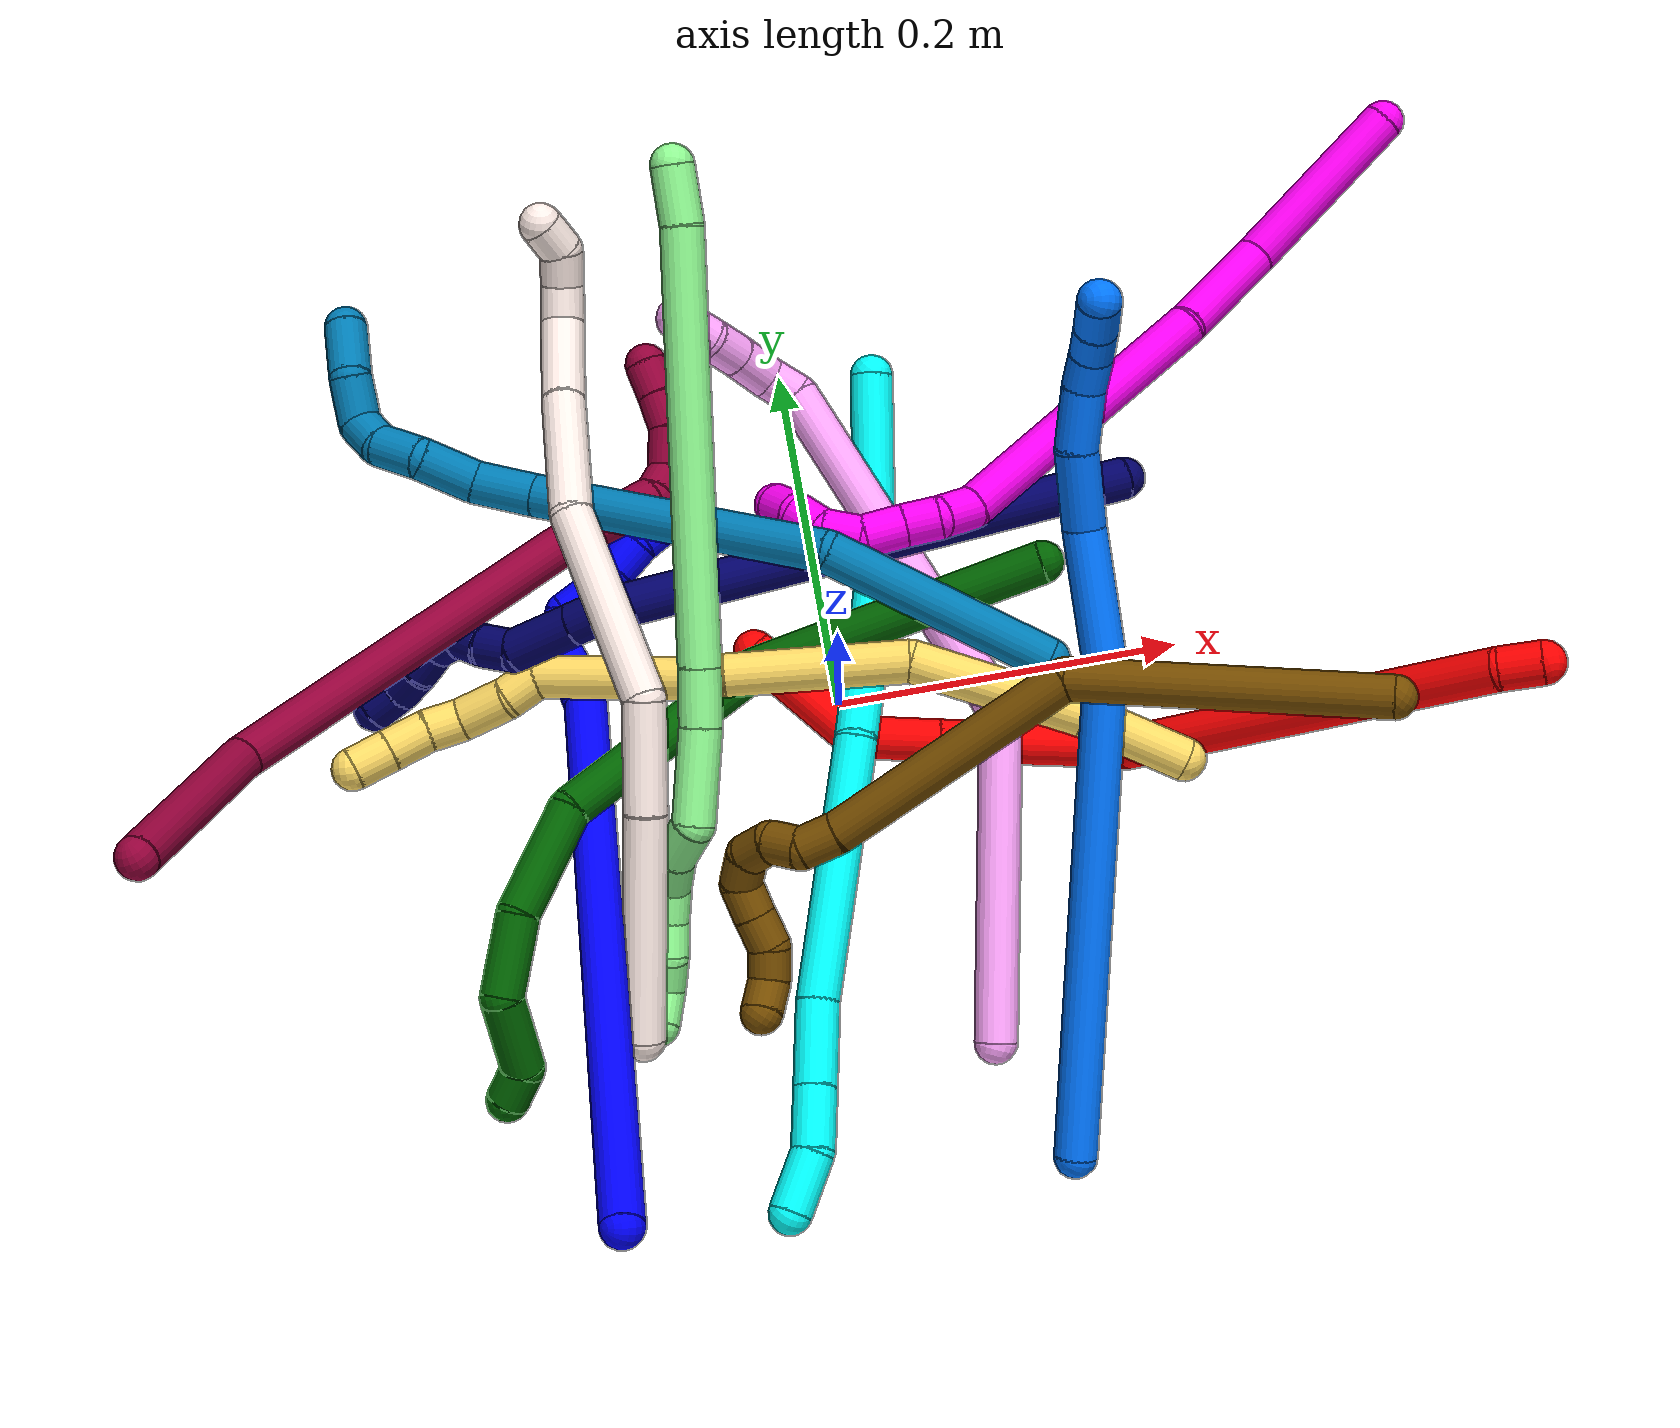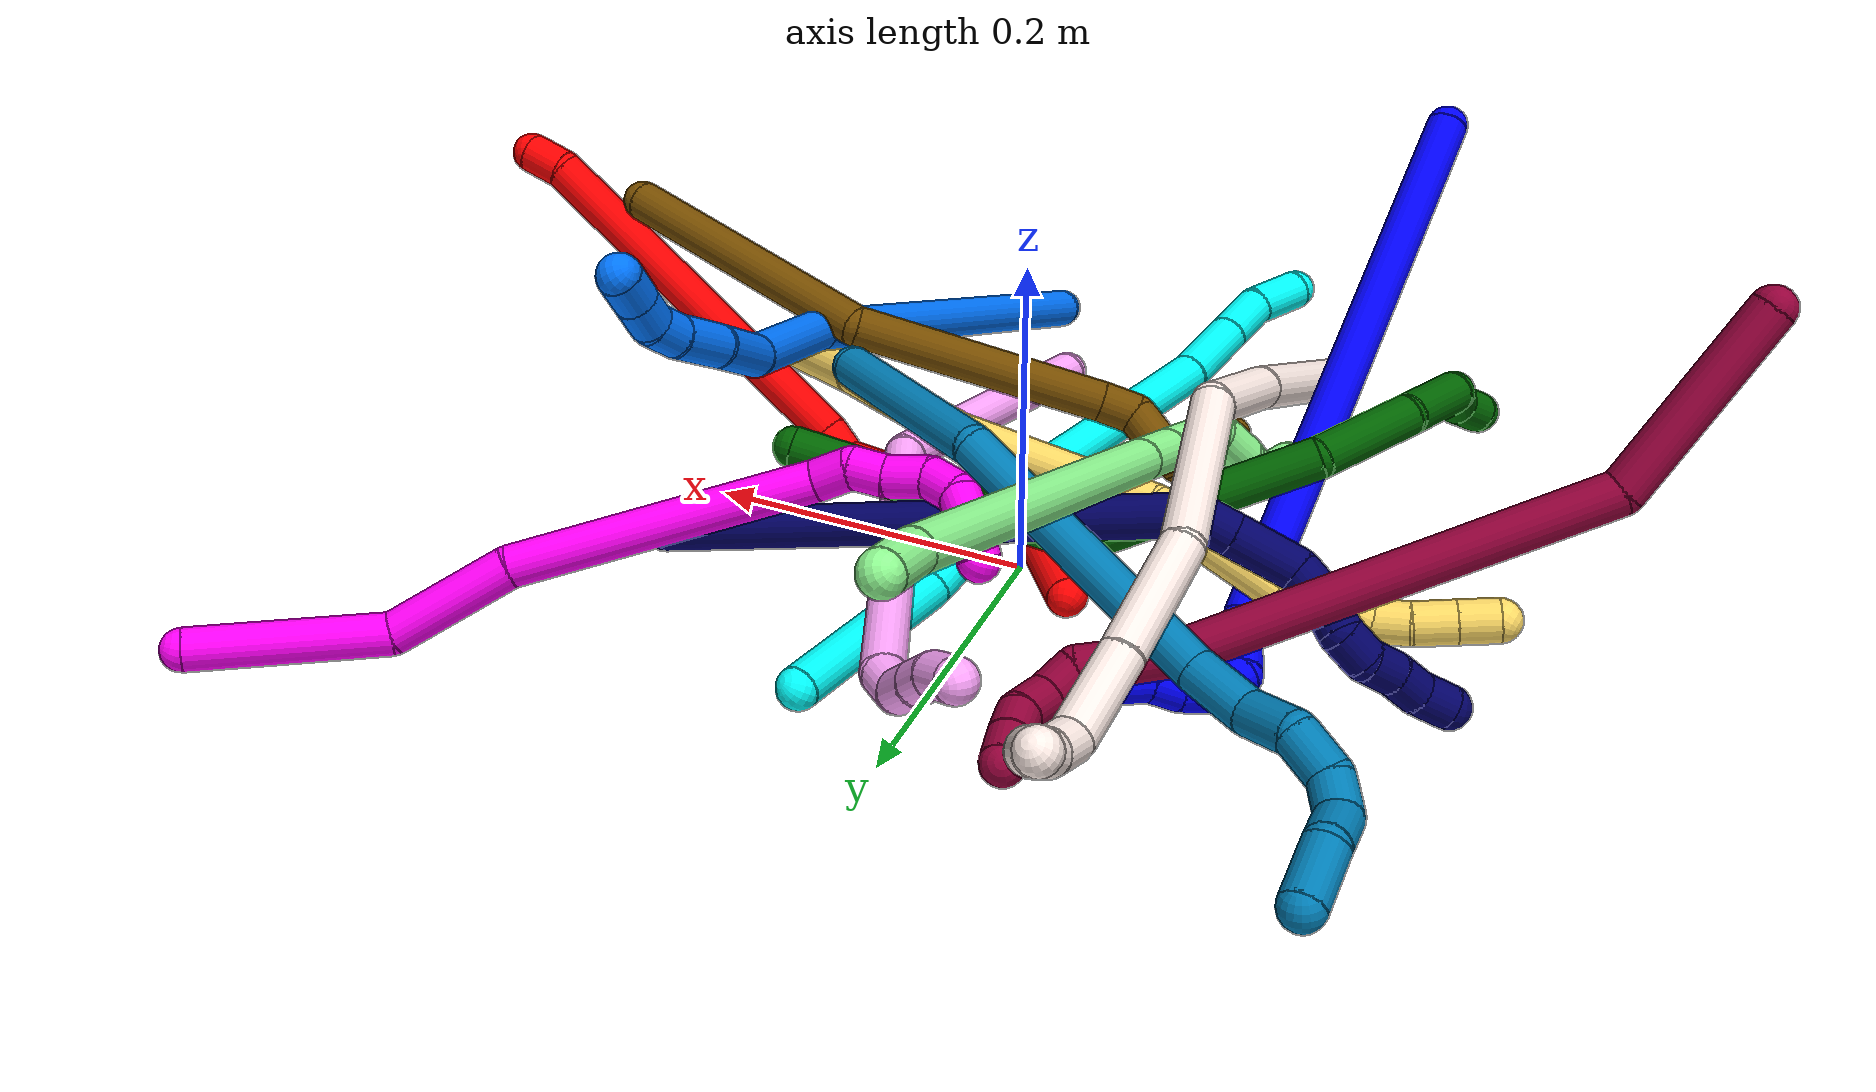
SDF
<sdf version="1.7">
 <world name="default">
  <plugin name="TubeGeneratorPlugin" filename="libtube_generator_plugin.so"/>
  <model name="photoneo_s_sensor">
   <static>1</static>
   <pose>0 0 2 1.57079 1.57079 3.14159</pose>
   <link name="link">
    <inertial><mass>0.1</mass></inertial>
    <sensor name="sensor" type="depth">
     <update_rate>30</update_rate>
     <camera>
      <horizontal_fov>1.22</horizontal_fov>
      <image><width>1920</width><height>1200</height><format>B8G8R8</format></image>
      <clip><near>0.1</near><far>4</far></clip>
      <depth_camera><output>points</output></depth_camera>
     </camera>
     <plugin name="camera_plugin" filename="libgazebo_ros_depth_camera.so">
      <baseline>0.2</baseline>
      <alwaysOn>1</alwaysOn>
      <updateRate>0.0</updateRate>
      <cameraName>camera_ir</cameraName>
      <imageTopicName>/camera/color/image_raw</imageTopicName>
      <cameraInfoTopicName>/camera/color/camera_info</cameraInfoTopicName>
      <depthImageTopicName>/camera/depth/image_raw</depthImageTopicName>
      <depthImageCameraInfoTopicName>/camera/depth/camera_info</depthImageCameraInfoTopicName>
      <pointCloudTopicName>/camera/depth/points</pointCloudTopicName>
      <frameName>fr_optical</frameName>
      <pointCloudCutoff>0.1</pointCloudCutoff>
      <pointCloudCutoffMax>2.0</pointCloudCutoffMax>
      <distortionK1>0</distortionK1>
      <distortionK2>0</distortionK2>
      <distortionK3>0</distortionK3>
      <distortionT1>0</distortionT1>
      <distortionT2>0</distortionT2>
      <CxPrime>0</CxPrime>
      <Cx>0</Cx>
      <Cy>0</Cy>
      <focalLength>0</focalLength>
      <hackBaseline>0</hackBaseline>
     </plugin>
    </sensor>
   </link>
  </model>
  <gravity>0 0 -9.8</gravity>
  <magnetic_field>6e-06 2.3e-05 -4.2e-05</magnetic_field>
  <atmosphere type="adiabatic"/>
  <physics name="default_physics" default="0" type="ode">
   <max_step_size>0.003</max_step_size>
   <real_time_factor>1</real_time_factor>
   <real_time_update_rate>1000</real_time_update_rate>
   <max_contacts>10000</max_contacts>
   <ode>
    <solver>
     <type>quick</type>
     <iters>100</iters>
     <sor>1.3</sor>
     <use_dynamic_moi_rescaling>0</use_dynamic_moi_rescaling>
    </solver>
    <constraints>
     <contact_max_correcting_vel>0</contact_max_correcting_vel>
     <contact_surface_layer>0.001</contact_surface_layer>
     <cfm>0</cfm>
     <erp>0.2</erp>
    </constraints>
   </ode>
  </physics>
  <scene><ambient>0.4 0.4 0.4 1</ambient><background>0.7 0.7 0.7 1</background><shadows>0</shadows></scene>
  <audio><device>default</device></audio>
  <spherical_coordinates>
   <surface_model>EARTH_WGS84</surface_model>
   <latitude_deg>0</latitude_deg>
   <longitude_deg>0</longitude_deg>
   <elevation>0</elevation>
   <heading_deg>0</heading_deg>
  </spherical_coordinates>
  <model name="bin">
   <static>1</static>
   <link name="bottom">
    <collision name="collision-bottom">
     <pose>0 0 -0.01 0 -0 0</pose>
     <geometry><box><size>0.8 0.6 0.02</size></box></geometry>
     <surface>
      <friction><ode><mu>100</mu><mu2>100</mu2></ode></friction>
      <contact><collide_bitmask>65535</collide_bitmask></contact>
     </surface>
    </collision>
   </link>
   <link name="west_wall">
    <collision name="collision-west_wall">
     <pose>-0.41 0 0.1 0 -0 0</pose>
     <geometry><box><size>0.02 0.6 0.2</size></box></geometry>
     <surface>
      <friction><ode><mu>100</mu><mu2>100</mu2></ode></friction>
      <contact><collide_bitmask>65535</collide_bitmask></contact>
     </surface>
    </collision>
   </link>
   <link name="east_wall">
    <collision name="collision-east_wall">
     <pose>0.41 0 0.1 0 -0 0</pose>
     <geometry><box><size>0.02 0.6 0.2</size></box></geometry>
     <surface>
      <friction><ode><mu>100</mu><mu2>100</mu2></ode></friction>
      <contact><collide_bitmask>65535</collide_bitmask></contact>
     </surface>
    </collision>
   </link>
   <link name="south_wall">
    <collision name="collision-south_wall">
     <pose>0 -0.31 0.1 0 -0 0</pose>
     <geometry><box><size>0.8 0.02 0.2</size></box></geometry>
     <surface>
      <friction><ode><mu>100</mu><mu2>100</mu2></ode></friction>
      <contact><collide_bitmask>65535</collide_bitmask></contact>
     </surface>
    </collision>
   </link>
   <link name="north_wall">
    <collision name="collision-north_wall">
     <pose>0 0.31 0.1 0 -0 0</pose>
     <geometry><box><size>0.8 0.02 0.2</size></box></geometry>
     <surface>
      <friction><ode><mu>100</mu><mu2>100</mu2></ode></friction>
      <contact><collide_bitmask>65535</collide_bitmask></contact>
     </surface>
    </collision>
   </link>
  </model>
  <model name="1">
   <static>0</static>
   <link name="1">
    <collision name="collision-cylinder-e_1_1_4">
     <pose>-0.049748 0.158705 -0.065859 -1.96415 -0.281819 0.418663</pose>
     <geometry><cylinder><radius>0.0125</radius><length>0.357768</length></cylinder></geometry>
     <surface>
      <friction><ode><mu>1.16</mu><mu2>1.16</mu2><slip1>0</slip1><slip2>0</slip2></ode></friction>
      <contact><ode><kp>1e+06</kp><kd>1</kd><max_vel>0</max_vel><min_depth>0.001</min_depth></ode></contact>
     </surface>
    </collision>
    <visual name="visual-cylinder-e_1_1_4">
     <pose>-0.049748 0.158705 -0.065859 -1.96415 -0.281819 0.418663</pose>
     <geometry><cylinder><radius>0.0125</radius><length>0.357768</length></cylinder></geometry>
     <material><ambient>0 0 1 1</ambient></material>
    </visual>
    <collision name="collision-cylinder-e_2_4_5">
     <pose>-0.102901 0.32763 -0.132787 -1.6749 -0.319955 0.35443</pose>
     <geometry><cylinder><radius>0.0125</radius><length>0.021651</length></cylinder></geometry>
     <surface>
      <friction><ode><mu>1.16</mu><mu2>1.16</mu2><slip1>0</slip1><slip2>0</slip2></ode></friction>
      <contact><ode><kp>1e+06</kp><kd>1</kd><max_vel>0</max_vel><min_depth>0.001</min_depth></ode></contact>
     </surface>
    </collision>
    <visual name="visual-cylinder-e_2_4_5">
     <pose>-0.102901 0.32763 -0.132787 -1.6749 -0.319955 0.35443</pose>
     <geometry><cylinder><radius>0.0125</radius><length>0.021651</length></cylinder></geometry>
     <material><ambient>0 0 1 1</ambient></material>
    </visual>
    <collision name="collision-cylinder-e_3_5_6">
     <pose>-0.108462 0.347699 -0.132198 -1.40416 -0.212576 0.180001</pose>
     <geometry><cylinder><radius>0.0125</radius><length>0.020435</length></cylinder></geometry>
     <surface>
      <friction><ode><mu>1.16</mu><mu2>1.16</mu2><slip1>0</slip1><slip2>0</slip2></ode></friction>
      <contact><ode><kp>1e+06</kp><kd>1</kd><max_vel>0</max_vel><min_depth>0.001</min_depth></ode></contact>
     </surface>
    </collision>
    <visual name="visual-cylinder-e_3_5_6">
     <pose>-0.108462 0.347699 -0.132198 -1.40416 -0.212576 0.180001</pose>
     <geometry><cylinder><radius>0.0125</radius><length>0.020435</length></cylinder></geometry>
     <material><ambient>0 0 1 1</ambient></material>
    </visual>
    <collision name="collision-cylinder-e_4_6_7">
     <pose>-0.10758 0.366514 -0.133958 -1.9349 0.306649 -0.441244</pose>
     <geometry><cylinder><radius>0.0125</radius><length>0.020128</length></cylinder></geometry>
     <surface>
      <friction><ode><mu>1.16</mu><mu2>1.16</mu2><slip1>0</slip1><slip2>0</slip2></ode></friction>
      <contact><ode><kp>1e+06</kp><kd>1</kd><max_vel>0</max_vel><min_depth>0.001</min_depth></ode></contact>
     </surface>
    </collision>
    <visual name="visual-cylinder-e_4_6_7">
     <pose>-0.10758 0.366514 -0.133958 -1.9349 0.306649 -0.441244</pose>
     <geometry><cylinder><radius>0.0125</radius><length>0.020128</length></cylinder></geometry>
     <material><ambient>0 0 1 1</ambient></material>
    </visual>
    <collision name="collision-cylinder-e_5_7_8">
     <pose>-0.098018 0.379284 -0.143942 -2.61649 0.709983 -1.88697</pose>
     <geometry><cylinder><radius>0.0125</radius><length>0.020017</length></cylinder></geometry>
     <surface>
      <friction><ode><mu>1.16</mu><mu2>1.16</mu2><slip1>0</slip1><slip2>0</slip2></ode></friction>
      <contact><ode><kp>1e+06</kp><kd>1</kd><max_vel>0</max_vel><min_depth>0.001</min_depth></ode></contact>
     </surface>
    </collision>
    <visual name="visual-cylinder-e_5_7_8">
     <pose>-0.098018 0.379284 -0.143942 -2.61649 0.709983 -1.88697</pose>
     <geometry><cylinder><radius>0.0125</radius><length>0.020017</length></cylinder></geometry>
     <material><ambient>0 0 1 1</ambient></material>
    </visual>
    <collision name="collision-cylinder-e_6_8_9">
     <pose>-0.082948 0.387069 -0.153847 -2.26857 1.02475 -1.75676</pose>
     <geometry><cylinder><radius>0.0125</radius><length>0.020001</length></cylinder></geometry>
     <surface>
      <friction><ode><mu>1.16</mu><mu2>1.16</mu2><slip1>0</slip1><slip2>0</slip2></ode></friction>
      <contact><ode><kp>1e+06</kp><kd>1</kd><max_vel>0</max_vel><min_depth>0.001</min_depth></ode></contact>
     </surface>
    </collision>
    <visual name="visual-cylinder-e_6_8_9">
     <pose>-0.082948 0.387069 -0.153847 -2.26857 1.02475 -1.75676</pose>
     <geometry><cylinder><radius>0.0125</radius><length>0.020001</length></cylinder></geometry>
     <material><ambient>0 0 1 1</ambient></material>
    </visual>
    <collision name="collision-cylinder-e_7_9_10">
     <pose>-0.068193 0.396652 -0.162666 -2.34525 0.669863 -1.38247</pose>
     <geometry><cylinder><radius>0.0125</radius><length>0.02</length></cylinder></geometry>
     <surface>
      <friction><ode><mu>1.16</mu><mu2>1.16</mu2><slip1>0</slip1><slip2>0</slip2></ode></friction>
      <contact><ode><kp>1e+06</kp><kd>1</kd><max_vel>0</max_vel><min_depth>0.001</min_depth></ode></contact>
     </surface>
    </collision>
    <visual name="visual-cylinder-e_7_9_10">
     <pose>-0.068193 0.396652 -0.162666 -2.34525 0.669863 -1.38247</pose>
     <geometry><cylinder><radius>0.0125</radius><length>0.02</length></cylinder></geometry>
     <material><ambient>0 0 1 1</ambient></material>
    </visual>
    <collision name="collision-cylinder-e_8_10_2">
     <pose>-0.058316 0.407127 -0.176073 -2.59043 0.375534 -1.18328</pose>
     <geometry><cylinder><radius>0.0125</radius><length>0.02</length></cylinder></geometry>
     <surface>
      <friction><ode><mu>1.16</mu><mu2>1.16</mu2><slip1>0</slip1><slip2>0</slip2></ode></friction>
      <contact><ode><kp>1e+06</kp><kd>1</kd><max_vel>0</max_vel><min_depth>0.001</min_depth></ode></contact>
     </surface>
    </collision>
    <visual name="visual-cylinder-e_8_10_2">
     <pose>-0.058316 0.407127 -0.176073 -2.59043 0.375534 -1.18328</pose>
     <geometry><cylinder><radius>0.0125</radius><length>0.02</length></cylinder></geometry>
     <material><ambient>0 0 1 1</ambient></material>
    </visual>
    <collision name="collision-sphere-2">
     <pose>-0.054648 0.411999 -0.183999 0 -0 0</pose>
     <geometry><sphere><radius>0.0125</radius></sphere></geometry>
     <surface>
      <friction><ode><mu>1.16</mu><mu2>1.16</mu2><slip1>0</slip1><slip2>0</slip2></ode></friction>
      <contact><ode><kp>1e+06</kp><kd>1</kd><max_vel>0</max_vel><min_depth>0.001</min_depth></ode></contact>
     </surface>
    </collision>
    <visual name="visual-sphere-2">
     <pose>-0.054648 0.411999 -0.183999 0 -0 0</pose>
     <geometry><sphere><radius>0.0125</radius></sphere></geometry>
     <material><ambient>0 0 1 1</ambient></material>
    </visual>
    <collision name="collision-sphere-10">
     <pose>-0.061984 0.402255 -0.168148 0 -0 0</pose>
     <geometry><sphere><radius>0.0125</radius></sphere></geometry>
     <surface>
      <friction><ode><mu>1.16</mu><mu2>1.16</mu2><slip1>0</slip1><slip2>0</slip2></ode></friction>
      <contact><ode><kp>1e+06</kp><kd>1</kd><max_vel>0</max_vel><min_depth>0.001</min_depth></ode></contact>
     </surface>
    </collision>
    <visual name="visual-sphere-10">
     <pose>-0.061984 0.402255 -0.168148 0 -0 0</pose>
     <geometry><sphere><radius>0.0125</radius></sphere></geometry>
     <material><ambient>0 0 1 1</ambient></material>
    </visual>
    <collision name="collision-sphere-9">
     <pose>-0.074401 0.391048 -0.157184 0 -0 0</pose>
     <geometry><sphere><radius>0.0125</radius></sphere></geometry>
     <surface>
      <friction><ode><mu>1.16</mu><mu2>1.16</mu2><slip1>0</slip1><slip2>0</slip2></ode></friction>
      <contact><ode><kp>1e+06</kp><kd>1</kd><max_vel>0</max_vel><min_depth>0.001</min_depth></ode></contact>
     </surface>
    </collision>
    <visual name="visual-sphere-9">
     <pose>-0.074401 0.391048 -0.157184 0 -0 0</pose>
     <geometry><sphere><radius>0.0125</radius></sphere></geometry>
     <material><ambient>0 0 1 1</ambient></material>
    </visual>
    <collision name="collision-sphere-4">
     <pose>-0.099496 0.317409 -0.131719 0 -0 0</pose>
     <geometry><sphere><radius>0.0125</radius></sphere></geometry>
     <surface>
      <friction><ode><mu>1.16</mu><mu2>1.16</mu2><slip1>0</slip1><slip2>0</slip2></ode></friction>
      <contact><ode><kp>1e+06</kp><kd>1</kd><max_vel>0</max_vel><min_depth>0.001</min_depth></ode></contact>
     </surface>
    </collision>
    <visual name="visual-sphere-4">
     <pose>-0.099496 0.317409 -0.131719 0 -0 0</pose>
     <geometry><sphere><radius>0.0125</radius></sphere></geometry>
     <material><ambient>0 0 1 1</ambient></material>
    </visual>
    <collision name="collision-sphere-1">
     <geometry><sphere><radius>0.0125</radius></sphere></geometry>
     <surface>
      <friction><ode><mu>1.16</mu><mu2>1.16</mu2><slip1>0</slip1><slip2>0</slip2></ode></friction>
      <contact><ode><kp>1e+06</kp><kd>1</kd><max_vel>0</max_vel><min_depth>0.001</min_depth></ode></contact>
     </surface>
    </collision>
    <visual name="visual-sphere-1">
     <geometry><sphere><radius>0.0125</radius></sphere></geometry>
     <material><ambient>0 0 1 1</ambient></material>
    </visual>
    <collision name="collision-sphere-8">
     <pose>-0.091494 0.383089 -0.15051 0 -0 0</pose>
     <geometry><sphere><radius>0.0125</radius></sphere></geometry>
     <surface>
      <friction><ode><mu>1.16</mu><mu2>1.16</mu2><slip1>0</slip1><slip2>0</slip2></ode></friction>
      <contact><ode><kp>1e+06</kp><kd>1</kd><max_vel>0</max_vel><min_depth>0.001</min_depth></ode></contact>
     </surface>
    </collision>
    <visual name="visual-sphere-8">
     <pose>-0.091494 0.383089 -0.15051 0 -0 0</pose>
     <geometry><sphere><radius>0.0125</radius></sphere></geometry>
     <material><ambient>0 0 1 1</ambient></material>
    </visual>
    <collision name="collision-sphere-5">
     <pose>-0.106306 0.33785 -0.133855 0 -0 0</pose>
     <geometry><sphere><radius>0.0125</radius></sphere></geometry>
     <surface>
      <friction><ode><mu>1.16</mu><mu2>1.16</mu2><slip1>0</slip1><slip2>0</slip2></ode></friction>
      <contact><ode><kp>1e+06</kp><kd>1</kd><max_vel>0</max_vel><min_depth>0.001</min_depth></ode></contact>
     </surface>
    </collision>
    <visual name="visual-sphere-5">
     <pose>-0.106306 0.33785 -0.133855 0 -0 0</pose>
     <geometry><sphere><radius>0.0125</radius></sphere></geometry>
     <material><ambient>0 0 1 1</ambient></material>
    </visual>
    <collision name="collision-sphere-6">
     <pose>-0.110617 0.357548 -0.130542 0 -0 0</pose>
     <geometry><sphere><radius>0.0125</radius></sphere></geometry>
     <surface>
      <friction><ode><mu>1.16</mu><mu2>1.16</mu2><slip1>0</slip1><slip2>0</slip2></ode></friction>
      <contact><ode><kp>1e+06</kp><kd>1</kd><max_vel>0</max_vel><min_depth>0.001</min_depth></ode></contact>
     </surface>
    </collision>
    <visual name="visual-sphere-6">
     <pose>-0.110617 0.357548 -0.130542 0 -0 0</pose>
     <geometry><sphere><radius>0.0125</radius></sphere></geometry>
     <material><ambient>0 0 1 1</ambient></material>
    </visual>
    <collision name="collision-sphere-7">
     <pose>-0.104542 0.375479 -0.137375 0 -0 0</pose>
     <geometry><sphere><radius>0.0125</radius></sphere></geometry>
     <surface>
      <friction><ode><mu>1.16</mu><mu2>1.16</mu2><slip1>0</slip1><slip2>0</slip2></ode></friction>
      <contact><ode><kp>1e+06</kp><kd>1</kd><max_vel>0</max_vel><min_depth>0.001</min_depth></ode></contact>
     </surface>
    </collision>
    <visual name="visual-sphere-7">
     <pose>-0.104542 0.375479 -0.137375 0 -0 0</pose>
     <geometry><sphere><radius>0.0125</radius></sphere></geometry>
     <material><ambient>0 0 1 1</ambient></material>
    </visual>
    <inertial>
     <pose>-0.061118 0.21953 -0.089137 0 -0 0</pose>
     <mass>0.5</mass>
     <inertia>
      <ixx>0.004853</ixx>
      <ixy>0</ixy>
      <ixz>0</ixz>
      <iyy>0.000585</iyy>
      <iyz>0</iyz>
      <izz>-0.002357</izz>
     </inertia>
    </inertial>
   </link>
   <pose>-0.164702 -0.288507 0.198933 -0.086689 -0.896 0.134248</pose>
  </model>
  <model name="2">
   <static>0</static>
   <link name="2">
    <collision name="collision-cylinder-e_1_1_4">
     <pose>-0.010536 -0.005236 -0.003547 2.16624 -1.03019 -1.63583</pose>
     <geometry><cylinder><radius>0.0125</radius><length>0.024576</length></cylinder></geometry>
     <surface>
      <friction><ode><mu>1.16</mu><mu2>1.16</mu2><slip1>0</slip1><slip2>0</slip2></ode></friction>
      <contact><ode><kp>1e+06</kp><kd>1</kd><max_vel>0</max_vel><min_depth>0.001</min_depth></ode></contact>
     </surface>
    </collision>
    <visual name="visual-cylinder-e_1_1_4">
     <pose>-0.010536 -0.005236 -0.003547 2.16624 -1.03019 -1.63583</pose>
     <geometry><cylinder><radius>0.0125</radius><length>0.024576</length></cylinder></geometry>
     <material><ambient>1 0 0 1</ambient></material>
    </visual>
    <collision name="collision-cylinder-e_2_4_5">
     <pose>-0.096672 -0.092129 -0.049182 2.0467 -0.688577 -1.0634</pose>
     <geometry><cylinder><radius>0.0125</radius><length>0.23795</length></cylinder></geometry>
     <surface>
      <friction><ode><mu>1.16</mu><mu2>1.16</mu2><slip1>0</slip1><slip2>0</slip2></ode></friction>
      <contact><ode><kp>1e+06</kp><kd>1</kd><max_vel>0</max_vel><min_depth>0.001</min_depth></ode></contact>
     </surface>
    </collision>
    <visual name="visual-cylinder-e_2_4_5">
     <pose>-0.096672 -0.092129 -0.049182 2.0467 -0.688577 -1.0634</pose>
     <geometry><cylinder><radius>0.0125</radius><length>0.23795</length></cylinder></geometry>
     <material><ambient>1 0 0 1</ambient></material>
    </visual>
    <collision name="collision-cylinder-e_3_5_6">
     <pose>-0.178625 -0.180188 -0.097597 2.35048 -0.614539 -1.29965</pose>
     <geometry><cylinder><radius>0.0125</radius><length>0.022032</length></cylinder></geometry>
     <surface>
      <friction><ode><mu>1.16</mu><mu2>1.16</mu2><slip1>0</slip1><slip2>0</slip2></ode></friction>
      <contact><ode><kp>1e+06</kp><kd>1</kd><max_vel>0</max_vel><min_depth>0.001</min_depth></ode></contact>
     </surface>
    </collision>
    <visual name="visual-cylinder-e_3_5_6">
     <pose>-0.178625 -0.180188 -0.097597 2.35048 -0.614539 -1.29965</pose>
     <geometry><cylinder><radius>0.0125</radius><length>0.022032</length></cylinder></geometry>
     <material><ambient>1 0 0 1</ambient></material>
    </visual>
    <collision name="collision-cylinder-e_4_6_7">
     <pose>-0.227259 -0.190823 -0.117773 2.84486 -1.24083 -2.72918</pose>
     <geometry><cylinder><radius>0.0125</radius><length>0.089386</length></cylinder></geometry>
     <surface>
      <friction><ode><mu>1.16</mu><mu2>1.16</mu2><slip1>0</slip1><slip2>0</slip2></ode></friction>
      <contact><ode><kp>1e+06</kp><kd>1</kd><max_vel>0</max_vel><min_depth>0.001</min_depth></ode></contact>
     </surface>
    </collision>
    <visual name="visual-cylinder-e_4_6_7">
     <pose>-0.227259 -0.190823 -0.117773 2.84486 -1.24083 -2.72918</pose>
     <geometry><cylinder><radius>0.0125</radius><length>0.089386</length></cylinder></geometry>
     <material><ambient>1 0 0 1</ambient></material>
    </visual>
    <collision name="collision-cylinder-e_5_7_8">
     <pose>-0.29246 -0.197302 -0.139332 2.85831 -1.23379 -2.74477</pose>
     <geometry><cylinder><radius>0.0125</radius><length>0.048571</length></cylinder></geometry>
     <surface>
      <friction><ode><mu>1.16</mu><mu2>1.16</mu2><slip1>0</slip1><slip2>0</slip2></ode></friction>
      <contact><ode><kp>1e+06</kp><kd>1</kd><max_vel>0</max_vel><min_depth>0.001</min_depth></ode></contact>
     </surface>
    </collision>
    <visual name="visual-cylinder-e_5_7_8">
     <pose>-0.29246 -0.197302 -0.139332 2.85831 -1.23379 -2.74477</pose>
     <geometry><cylinder><radius>0.0125</radius><length>0.048571</length></cylinder></geometry>
     <material><ambient>1 0 0 1</ambient></material>
    </visual>
    <collision name="collision-cylinder-e_6_8_2">
     <pose>-0.33661 -0.195647 -0.179215 -3.02099 -0.579946 2.7423</pose>
     <geometry><cylinder><radius>0.0125</radius><length>0.077486</length></cylinder></geometry>
     <surface>
      <friction><ode><mu>1.16</mu><mu2>1.16</mu2><slip1>0</slip1><slip2>0</slip2></ode></friction>
      <contact><ode><kp>1e+06</kp><kd>1</kd><max_vel>0</max_vel><min_depth>0.001</min_depth></ode></contact>
     </surface>
    </collision>
    <visual name="visual-cylinder-e_6_8_2">
     <pose>-0.33661 -0.195647 -0.179215 -3.02099 -0.579946 2.7423</pose>
     <geometry><cylinder><radius>0.0125</radius><length>0.077486</length></cylinder></geometry>
     <material><ambient>1 0 0 1</ambient></material>
    </visual>
    <collision name="collision-sphere-2">
     <pose>-0.35784 -0.191748 -0.211388 0 -0 0</pose>
     <geometry><sphere><radius>0.0125</radius></sphere></geometry>
     <surface>
      <friction><ode><mu>1.16</mu><mu2>1.16</mu2><slip1>0</slip1><slip2>0</slip2></ode></friction>
      <contact><ode><kp>1e+06</kp><kd>1</kd><max_vel>0</max_vel><min_depth>0.001</min_depth></ode></contact>
     </surface>
    </collision>
    <visual name="visual-sphere-2">
     <pose>-0.35784 -0.191748 -0.211388 0 -0 0</pose>
     <geometry><sphere><radius>0.0125</radius></sphere></geometry>
     <material><ambient>1 0 0 1</ambient></material>
    </visual>
    <collision name="collision-sphere-4">
     <pose>-0.021071 -0.010471 -0.007094 0 -0 0</pose>
     <geometry><sphere><radius>0.0125</radius></sphere></geometry>
     <surface>
      <friction><ode><mu>1.16</mu><mu2>1.16</mu2><slip1>0</slip1><slip2>0</slip2></ode></friction>
      <contact><ode><kp>1e+06</kp><kd>1</kd><max_vel>0</max_vel><min_depth>0.001</min_depth></ode></contact>
     </surface>
    </collision>
    <visual name="visual-sphere-4">
     <pose>-0.021071 -0.010471 -0.007094 0 -0 0</pose>
     <geometry><sphere><radius>0.0125</radius></sphere></geometry>
     <material><ambient>1 0 0 1</ambient></material>
    </visual>
    <collision name="collision-sphere-1">
     <geometry><sphere><radius>0.0125</radius></sphere></geometry>
     <surface>
      <friction><ode><mu>1.16</mu><mu2>1.16</mu2><slip1>0</slip1><slip2>0</slip2></ode></friction>
      <contact><ode><kp>1e+06</kp><kd>1</kd><max_vel>0</max_vel><min_depth>0.001</min_depth></ode></contact>
     </surface>
    </collision>
    <visual name="visual-sphere-1">
     <geometry><sphere><radius>0.0125</radius></sphere></geometry>
     <material><ambient>1 0 0 1</ambient></material>
    </visual>
    <collision name="collision-sphere-8">
     <pose>-0.315379 -0.199546 -0.147042 0 -0 0</pose>
     <geometry><sphere><radius>0.0125</radius></sphere></geometry>
     <surface>
      <friction><ode><mu>1.16</mu><mu2>1.16</mu2><slip1>0</slip1><slip2>0</slip2></ode></friction>
      <contact><ode><kp>1e+06</kp><kd>1</kd><max_vel>0</max_vel><min_depth>0.001</min_depth></ode></contact>
     </surface>
    </collision>
    <visual name="visual-sphere-8">
     <pose>-0.315379 -0.199546 -0.147042 0 -0 0</pose>
     <geometry><sphere><radius>0.0125</radius></sphere></geometry>
     <material><ambient>1 0 0 1</ambient></material>
    </visual>
    <collision name="collision-sphere-5">
     <pose>-0.172274 -0.173788 -0.091269 0 -0 0</pose>
     <geometry><sphere><radius>0.0125</radius></sphere></geometry>
     <surface>
      <friction><ode><mu>1.16</mu><mu2>1.16</mu2><slip1>0</slip1><slip2>0</slip2></ode></friction>
      <contact><ode><kp>1e+06</kp><kd>1</kd><max_vel>0</max_vel><min_depth>0.001</min_depth></ode></contact>
     </surface>
    </collision>
    <visual name="visual-sphere-5">
     <pose>-0.172274 -0.173788 -0.091269 0 -0 0</pose>
     <geometry><sphere><radius>0.0125</radius></sphere></geometry>
     <material><ambient>1 0 0 1</ambient></material>
    </visual>
    <collision name="collision-sphere-6">
     <pose>-0.184977 -0.186589 -0.103925 0 -0 0</pose>
     <geometry><sphere><radius>0.0125</radius></sphere></geometry>
     <surface>
      <friction><ode><mu>1.16</mu><mu2>1.16</mu2><slip1>0</slip1><slip2>0</slip2></ode></friction>
      <contact><ode><kp>1e+06</kp><kd>1</kd><max_vel>0</max_vel><min_depth>0.001</min_depth></ode></contact>
     </surface>
    </collision>
    <visual name="visual-sphere-6">
     <pose>-0.184977 -0.186589 -0.103925 0 -0 0</pose>
     <geometry><sphere><radius>0.0125</radius></sphere></geometry>
     <material><ambient>1 0 0 1</ambient></material>
    </visual>
    <collision name="collision-sphere-7">
     <pose>-0.269541 -0.195057 -0.131622 0 -0 0</pose>
     <geometry><sphere><radius>0.0125</radius></sphere></geometry>
     <surface>
      <friction><ode><mu>1.16</mu><mu2>1.16</mu2><slip1>0</slip1><slip2>0</slip2></ode></friction>
      <contact><ode><kp>1e+06</kp><kd>1</kd><max_vel>0</max_vel><min_depth>0.001</min_depth></ode></contact>
     </surface>
    </collision>
    <visual name="visual-sphere-7">
     <pose>-0.269541 -0.195057 -0.131622 0 -0 0</pose>
     <geometry><sphere><radius>0.0125</radius></sphere></geometry>
     <material><ambient>1 0 0 1</ambient></material>
    </visual>
    <inertial>
     <pose>-0.175598 -0.135641 -0.090243 0 -0 0</pose>
     <mass>0.5</mass>
     <inertia>
      <ixx>-0.00042</ixx>
      <ixy>0</ixy>
      <ixz>0</ixz>
      <iyy>-0.000356</iyy>
      <iyz>0</iyz>
      <izz>0.001581</izz>
     </inertia>
    </inertial>
   </link>
   <pose>0.373489 -0.077136 0.168902 1.25482 0.248561 0.066878</pose>
  </model>
  <model name="3">
   <static>0</static>
   <link name="3">
    <collision name="collision-cylinder-e_1_1_4">
     <pose>-0.001508 -0.04319 -0.047124 2.39972 -0.023593 -0.060644</pose>
     <geometry><cylinder><radius>0.0125</radius><length>0.12788</length></cylinder></geometry>
     <surface>
      <friction><ode><mu>1.16</mu><mu2>1.16</mu2><slip1>0</slip1><slip2>0</slip2></ode></friction>
      <contact><ode><kp>1e+06</kp><kd>1</kd><max_vel>0</max_vel><min_depth>0.001</min_depth></ode></contact>
     </surface>
    </collision>
    <visual name="visual-cylinder-e_1_1_4">
     <pose>-0.001508 -0.04319 -0.047124 2.39972 -0.023593 -0.060644</pose>
     <geometry><cylinder><radius>0.0125</radius><length>0.12788</length></cylinder></geometry>
     <material><ambient>0.003922 1 0.996078 1</ambient></material>
    </visual>
    <collision name="collision-cylinder-e_2_4_5">
     <pose>-0.020908 -0.124012 -0.120136 2.1734 -0.373335 -0.689659</pose>
     <geometry><cylinder><radius>0.0125</radius><length>0.09811</length></cylinder></geometry>
     <surface>
      <friction><ode><mu>1.16</mu><mu2>1.16</mu2><slip1>0</slip1><slip2>0</slip2></ode></friction>
      <contact><ode><kp>1e+06</kp><kd>1</kd><max_vel>0</max_vel><min_depth>0.001</min_depth></ode></contact>
     </surface>
    </collision>
    <visual name="visual-cylinder-e_2_4_5">
     <pose>-0.020908 -0.124012 -0.120136 2.1734 -0.373335 -0.689659</pose>
     <geometry><cylinder><radius>0.0125</radius><length>0.09811</length></cylinder></geometry>
     <material><ambient>0.003922 1 0.996078 1</ambient></material>
    </visual>
    <collision name="collision-cylinder-e_3_5_6">
     <pose>-0.055623 -0.211516 -0.201354 2.408 -0.222125 -0.565034</pose>
     <geometry><cylinder><radius>0.0125</radius><length>0.152732</length></cylinder></geometry>
     <surface>
      <friction><ode><mu>1.16</mu><mu2>1.16</mu2><slip1>0</slip1><slip2>0</slip2></ode></friction>
      <contact><ode><kp>1e+06</kp><kd>1</kd><max_vel>0</max_vel><min_depth>0.001</min_depth></ode></contact>
     </surface>
    </collision>
    <visual name="visual-cylinder-e_3_5_6">
     <pose>-0.055623 -0.211516 -0.201354 2.408 -0.222125 -0.565034</pose>
     <geometry><cylinder><radius>0.0125</radius><length>0.152732</length></cylinder></geometry>
     <material><ambient>0.003922 1 0.996078 1</ambient></material>
    </visual>
    <collision name="collision-cylinder-e_4_6_7">
     <pose>-0.077056 -0.27995 -0.272232 2.26816 -0.188086 -0.398769</pose>
     <geometry><cylinder><radius>0.0125</radius><length>0.049294</length></cylinder></geometry>
     <surface>
      <friction><ode><mu>1.16</mu><mu2>1.16</mu2><slip1>0</slip1><slip2>0</slip2></ode></friction>
      <contact><ode><kp>1e+06</kp><kd>1</kd><max_vel>0</max_vel><min_depth>0.001</min_depth></ode></contact>
     </surface>
    </collision>
    <visual name="visual-cylinder-e_4_6_7">
     <pose>-0.077056 -0.27995 -0.272232 2.26816 -0.188086 -0.398769</pose>
     <geometry><cylinder><radius>0.0125</radius><length>0.049294</length></cylinder></geometry>
     <material><ambient>0.003922 1 0.996078 1</ambient></material>
    </visual>
    <collision name="collision-cylinder-e_5_7_8">
     <pose>-0.085343 -0.312244 -0.298955 2.2538 -0.204875 -0.425778</pose>
     <geometry><cylinder><radius>0.0125</radius><length>0.036168</length></cylinder></geometry>
     <surface>
      <friction><ode><mu>1.16</mu><mu2>1.16</mu2><slip1>0</slip1><slip2>0</slip2></ode></friction>
      <contact><ode><kp>1e+06</kp><kd>1</kd><max_vel>0</max_vel><min_depth>0.001</min_depth></ode></contact>
     </surface>
    </collision>
    <visual name="visual-cylinder-e_5_7_8">
     <pose>-0.085343 -0.312244 -0.298955 2.2538 -0.204875 -0.425778</pose>
     <geometry><cylinder><radius>0.0125</radius><length>0.036168</length></cylinder></geometry>
     <material><ambient>0.003922 1 0.996078 1</ambient></material>
    </visual>
    <collision name="collision-cylinder-e_6_8_2">
     <pose>-0.095515 -0.335126 -0.324089 2.5615 -0.370998 -1.12258</pose>
     <geometry><cylinder><radius>0.0125</radius><length>0.035816</length></cylinder></geometry>
     <surface>
      <friction><ode><mu>1.16</mu><mu2>1.16</mu2><slip1>0</slip1><slip2>0</slip2></ode></friction>
      <contact><ode><kp>1e+06</kp><kd>1</kd><max_vel>0</max_vel><min_depth>0.001</min_depth></ode></contact>
     </surface>
    </collision>
    <visual name="visual-cylinder-e_6_8_2">
     <pose>-0.095515 -0.335126 -0.324089 2.5615 -0.370998 -1.12258</pose>
     <geometry><cylinder><radius>0.0125</radius><length>0.035816</length></cylinder></geometry>
     <material><ambient>0.003922 1 0.996078 1</ambient></material>
    </visual>
    <collision name="collision-sphere-2">
     <pose>-0.102007 -0.344273 -0.338049 0 -0 0</pose>
     <geometry><sphere><radius>0.0125</radius></sphere></geometry>
     <surface>
      <friction><ode><mu>1.16</mu><mu2>1.16</mu2><slip1>0</slip1><slip2>0</slip2></ode></friction>
      <contact><ode><kp>1e+06</kp><kd>1</kd><max_vel>0</max_vel><min_depth>0.001</min_depth></ode></contact>
     </surface>
    </collision>
    <visual name="visual-sphere-2">
     <pose>-0.102007 -0.344273 -0.338049 0 -0 0</pose>
     <geometry><sphere><radius>0.0125</radius></sphere></geometry>
     <material><ambient>0.003922 1 0.996078 1</ambient></material>
    </visual>
    <collision name="collision-sphere-4">
     <pose>-0.003017 -0.086381 -0.094247 0 -0 0</pose>
     <geometry><sphere><radius>0.0125</radius></sphere></geometry>
     <surface>
      <friction><ode><mu>1.16</mu><mu2>1.16</mu2><slip1>0</slip1><slip2>0</slip2></ode></friction>
      <contact><ode><kp>1e+06</kp><kd>1</kd><max_vel>0</max_vel><min_depth>0.001</min_depth></ode></contact>
     </surface>
    </collision>
    <visual name="visual-sphere-4">
     <pose>-0.003017 -0.086381 -0.094247 0 -0 0</pose>
     <geometry><sphere><radius>0.0125</radius></sphere></geometry>
     <material><ambient>0.003922 1 0.996078 1</ambient></material>
    </visual>
    <collision name="collision-sphere-1">
     <geometry><sphere><radius>0.0125</radius></sphere></geometry>
     <surface>
      <friction><ode><mu>1.16</mu><mu2>1.16</mu2><slip1>0</slip1><slip2>0</slip2></ode></friction>
      <contact><ode><kp>1e+06</kp><kd>1</kd><max_vel>0</max_vel><min_depth>0.001</min_depth></ode></contact>
     </surface>
    </collision>
    <visual name="visual-sphere-1">
     <geometry><sphere><radius>0.0125</radius></sphere></geometry>
     <material><ambient>0.003922 1 0.996078 1</ambient></material>
    </visual>
    <collision name="collision-sphere-8">
     <pose>-0.089022 -0.325978 -0.31013 0 -0 0</pose>
     <geometry><sphere><radius>0.0125</radius></sphere></geometry>
     <surface>
      <friction><ode><mu>1.16</mu><mu2>1.16</mu2><slip1>0</slip1><slip2>0</slip2></ode></friction>
      <contact><ode><kp>1e+06</kp><kd>1</kd><max_vel>0</max_vel><min_depth>0.001</min_depth></ode></contact>
     </surface>
    </collision>
    <visual name="visual-sphere-8">
     <pose>-0.089022 -0.325978 -0.31013 0 -0 0</pose>
     <geometry><sphere><radius>0.0125</radius></sphere></geometry>
     <material><ambient>0.003922 1 0.996078 1</ambient></material>
    </visual>
    <collision name="collision-sphere-5">
     <pose>-0.0388 -0.161642 -0.146025 0 -0 0</pose>
     <geometry><sphere><radius>0.0125</radius></sphere></geometry>
     <surface>
      <friction><ode><mu>1.16</mu><mu2>1.16</mu2><slip1>0</slip1><slip2>0</slip2></ode></friction>
      <contact><ode><kp>1e+06</kp><kd>1</kd><max_vel>0</max_vel><min_depth>0.001</min_depth></ode></contact>
     </surface>
    </collision>
    <visual name="visual-sphere-5">
     <pose>-0.0388 -0.161642 -0.146025 0 -0 0</pose>
     <geometry><sphere><radius>0.0125</radius></sphere></geometry>
     <material><ambient>0.003922 1 0.996078 1</ambient></material>
    </visual>
    <collision name="collision-sphere-6">
     <pose>-0.072447 -0.261391 -0.256683 0 -0 0</pose>
     <geometry><sphere><radius>0.0125</radius></sphere></geometry>
     <surface>
      <friction><ode><mu>1.16</mu><mu2>1.16</mu2><slip1>0</slip1><slip2>0</slip2></ode></friction>
      <contact><ode><kp>1e+06</kp><kd>1</kd><max_vel>0</max_vel><min_depth>0.001</min_depth></ode></contact>
     </surface>
    </collision>
    <visual name="visual-sphere-6">
     <pose>-0.072447 -0.261391 -0.256683 0 -0 0</pose>
     <geometry><sphere><radius>0.0125</radius></sphere></geometry>
     <material><ambient>0.003922 1 0.996078 1</ambient></material>
    </visual>
    <collision name="collision-sphere-7">
     <pose>-0.081664 -0.29851 -0.287781 0 -0 0</pose>
     <geometry><sphere><radius>0.0125</radius></sphere></geometry>
     <surface>
      <friction><ode><mu>1.16</mu><mu2>1.16</mu2><slip1>0</slip1><slip2>0</slip2></ode></friction>
      <contact><ode><kp>1e+06</kp><kd>1</kd><max_vel>0</max_vel><min_depth>0.001</min_depth></ode></contact>
     </surface>
    </collision>
    <visual name="visual-sphere-7">
     <pose>-0.081664 -0.29851 -0.287781 0 -0 0</pose>
     <geometry><sphere><radius>0.0125</radius></sphere></geometry>
     <material><ambient>0.003922 1 0.996078 1</ambient></material>
    </visual>
    <inertial>
     <pose>-0.042091 -0.174182 -0.168811 0 -0 0</pose>
     <mass>0.5</mass>
     <inertia>
      <ixx>0.000268</ixx>
      <ixy>0</ixy>
      <ixz>0</ixz>
      <iyy>-0.000584</iyy>
      <iyz>0</iyz>
      <izz>0.000478</izz>
     </inertia>
    </inertial>
   </link>
   <pose>0.052879 0.185077 0.025505 -0.705129 0.704046 -0.065897</pose>
  </model>
  <model name="4">
   <static>0</static>
   <link name="4">
    <collision name="collision-cylinder-e_1_1_4">
     <pose>-0.022355 -0.002338 0.091223 0.025621 -0.240251 -0.003093</pose>
     <geometry><cylinder><radius>0.0125</radius><length>0.187903</length></cylinder></geometry>
     <surface>
      <friction><ode><mu>1.16</mu><mu2>1.16</mu2><slip1>0</slip1><slip2>0</slip2></ode></friction>
      <contact><ode><kp>1e+06</kp><kd>1</kd><max_vel>0</max_vel><min_depth>0.001</min_depth></ode></contact>
     </surface>
    </collision>
    <visual name="visual-cylinder-e_1_1_4">
     <pose>-0.022355 -0.002338 0.091223 0.025621 -0.240251 -0.003093</pose>
     <geometry><cylinder><radius>0.0125</radius><length>0.187903</length></cylinder></geometry>
     <material><ambient>1 0.65098 0.996078 1</ambient></material>
    </visual>
    <collision name="collision-cylinder-e_2_4_5">
     <pose>-0.125743 -0.000835 0.257012 -0.051457 -0.826269 0.022561</pose>
     <geometry><cylinder><radius>0.0125</radius><length>0.220372</length></cylinder></geometry>
     <surface>
      <friction><ode><mu>1.16</mu><mu2>1.16</mu2><slip1>0</slip1><slip2>0</slip2></ode></friction>
      <contact><ode><kp>1e+06</kp><kd>1</kd><max_vel>0</max_vel><min_depth>0.001</min_depth></ode></contact>
     </surface>
    </collision>
    <visual name="visual-cylinder-e_2_4_5">
     <pose>-0.125743 -0.000835 0.257012 -0.051457 -0.826269 0.022561</pose>
     <geometry><cylinder><radius>0.0125</radius><length>0.220372</length></cylinder></geometry>
     <material><ambient>1 0.65098 0.996078 1</ambient></material>
    </visual>
    <collision name="collision-cylinder-e_3_5_6">
     <pose>-0.216318 0.001602 0.33446 0.4532 -1.24676 -0.328568</pose>
     <geometry><cylinder><radius>0.0125</radius><length>0.020136</length></cylinder></geometry>
     <surface>
      <friction><ode><mu>1.16</mu><mu2>1.16</mu2><slip1>0</slip1><slip2>0</slip2></ode></friction>
      <contact><ode><kp>1e+06</kp><kd>1</kd><max_vel>0</max_vel><min_depth>0.001</min_depth></ode></contact>
     </surface>
    </collision>
    <visual name="visual-cylinder-e_3_5_6">
     <pose>-0.216318 0.001602 0.33446 0.4532 -1.24676 -0.328568</pose>
     <geometry><cylinder><radius>0.0125</radius><length>0.020136</length></cylinder></geometry>
     <material><ambient>1 0.65098 0.996078 1</ambient></material>
    </visual>
    <collision name="collision-cylinder-e_4_6_7">
     <pose>-0.234738 -0.009546 0.340343 1.27203 -0.716327 -0.539292</pose>
     <geometry><cylinder><radius>0.0125</radius><length>0.027035</length></cylinder></geometry>
     <surface>
      <friction><ode><mu>1.16</mu><mu2>1.16</mu2><slip1>0</slip1><slip2>0</slip2></ode></friction>
      <contact><ode><kp>1e+06</kp><kd>1</kd><max_vel>0</max_vel><min_depth>0.001</min_depth></ode></contact>
     </surface>
    </collision>
    <visual name="visual-cylinder-e_4_6_7">
     <pose>-0.234738 -0.009546 0.340343 1.27203 -0.716327 -0.539292</pose>
     <geometry><cylinder><radius>0.0125</radius><length>0.027035</length></cylinder></geometry>
     <material><ambient>1 0.65098 0.996078 1</ambient></material>
    </visual>
    <collision name="collision-cylinder-e_5_7_8">
     <pose>-0.250474 -0.0271 0.345201 1.33738 -0.707043 -0.567418</pose>
     <geometry><cylinder><radius>0.0125</radius><length>0.021121</length></cylinder></geometry>
     <surface>
      <friction><ode><mu>1.16</mu><mu2>1.16</mu2><slip1>0</slip1><slip2>0</slip2></ode></friction>
      <contact><ode><kp>1e+06</kp><kd>1</kd><max_vel>0</max_vel><min_depth>0.001</min_depth></ode></contact>
     </surface>
    </collision>
    <visual name="visual-cylinder-e_5_7_8">
     <pose>-0.250474 -0.0271 0.345201 1.33738 -0.707043 -0.567418</pose>
     <geometry><cylinder><radius>0.0125</radius><length>0.021121</length></cylinder></geometry>
     <material><ambient>1 0.65098 0.996078 1</ambient></material>
    </visual>
    <collision name="collision-cylinder-e_6_8_2">
     <pose>-0.267239 -0.040534 0.349808 1.11596 -1.00726 -0.662486</pose>
     <geometry><cylinder><radius>0.0125</radius><length>0.023432</length></cylinder></geometry>
     <surface>
      <friction><ode><mu>1.16</mu><mu2>1.16</mu2><slip1>0</slip1><slip2>0</slip2></ode></friction>
      <contact><ode><kp>1e+06</kp><kd>1</kd><max_vel>0</max_vel><min_depth>0.001</min_depth></ode></contact>
     </surface>
    </collision>
    <visual name="visual-cylinder-e_6_8_2">
     <pose>-0.267239 -0.040534 0.349808 1.11596 -1.00726 -0.662486</pose>
     <geometry><cylinder><radius>0.0125</radius><length>0.023432</length></cylinder></geometry>
     <material><ambient>1 0.65098 0.996078 1</ambient></material>
    </visual>
    <collision name="collision-sphere-2">
     <pose>-0.277143 -0.046156 0.352557 0 -0 0</pose>
     <geometry><sphere><radius>0.0125</radius></sphere></geometry>
     <surface>
      <friction><ode><mu>1.16</mu><mu2>1.16</mu2><slip1>0</slip1><slip2>0</slip2></ode></friction>
      <contact><ode><kp>1e+06</kp><kd>1</kd><max_vel>0</max_vel><min_depth>0.001</min_depth></ode></contact>
     </surface>
    </collision>
    <visual name="visual-sphere-2">
     <pose>-0.277143 -0.046156 0.352557 0 -0 0</pose>
     <geometry><sphere><radius>0.0125</radius></sphere></geometry>
     <material><ambient>1 0.65098 0.996078 1</ambient></material>
    </visual>
    <collision name="collision-sphere-4">
     <pose>-0.044711 -0.004675 0.182446 0 -0 0</pose>
     <geometry><sphere><radius>0.0125</radius></sphere></geometry>
     <surface>
      <friction><ode><mu>1.16</mu><mu2>1.16</mu2><slip1>0</slip1><slip2>0</slip2></ode></friction>
      <contact><ode><kp>1e+06</kp><kd>1</kd><max_vel>0</max_vel><min_depth>0.001</min_depth></ode></contact>
     </surface>
    </collision>
    <visual name="visual-sphere-4">
     <pose>-0.044711 -0.004675 0.182446 0 -0 0</pose>
     <geometry><sphere><radius>0.0125</radius></sphere></geometry>
     <material><ambient>1 0.65098 0.996078 1</ambient></material>
    </visual>
    <collision name="collision-sphere-1">
     <geometry><sphere><radius>0.0125</radius></sphere></geometry>
     <surface>
      <friction><ode><mu>1.16</mu><mu2>1.16</mu2><slip1>0</slip1><slip2>0</slip2></ode></friction>
      <contact><ode><kp>1e+06</kp><kd>1</kd><max_vel>0</max_vel><min_depth>0.001</min_depth></ode></contact>
     </surface>
    </collision>
    <visual name="visual-sphere-1">
     <geometry><sphere><radius>0.0125</radius></sphere></geometry>
     <material><ambient>1 0.65098 0.996078 1</ambient></material>
    </visual>
    <collision name="collision-sphere-8">
     <pose>-0.257334 -0.034912 0.347058 0 -0 0</pose>
     <geometry><sphere><radius>0.0125</radius></sphere></geometry>
     <surface>
      <friction><ode><mu>1.16</mu><mu2>1.16</mu2><slip1>0</slip1><slip2>0</slip2></ode></friction>
      <contact><ode><kp>1e+06</kp><kd>1</kd><max_vel>0</max_vel><min_depth>0.001</min_depth></ode></contact>
     </surface>
    </collision>
    <visual name="visual-sphere-8">
     <pose>-0.257334 -0.034912 0.347058 0 -0 0</pose>
     <geometry><sphere><radius>0.0125</radius></sphere></geometry>
     <material><ambient>1 0.65098 0.996078 1</ambient></material>
    </visual>
    <collision name="collision-sphere-5">
     <pose>-0.206774 0.003005 0.331578 0 -0 0</pose>
     <geometry><sphere><radius>0.0125</radius></sphere></geometry>
     <surface>
      <friction><ode><mu>1.16</mu><mu2>1.16</mu2><slip1>0</slip1><slip2>0</slip2></ode></friction>
      <contact><ode><kp>1e+06</kp><kd>1</kd><max_vel>0</max_vel><min_depth>0.001</min_depth></ode></contact>
     </surface>
    </collision>
    <visual name="visual-sphere-5">
     <pose>-0.206774 0.003005 0.331578 0 -0 0</pose>
     <geometry><sphere><radius>0.0125</radius></sphere></geometry>
     <material><ambient>1 0.65098 0.996078 1</ambient></material>
    </visual>
    <collision name="collision-sphere-6">
     <pose>-0.225862 0.000198 0.337342 0 -0 0</pose>
     <geometry><sphere><radius>0.0125</radius></sphere></geometry>
     <surface>
      <friction><ode><mu>1.16</mu><mu2>1.16</mu2><slip1>0</slip1><slip2>0</slip2></ode></friction>
      <contact><ode><kp>1e+06</kp><kd>1</kd><max_vel>0</max_vel><min_depth>0.001</min_depth></ode></contact>
     </surface>
    </collision>
    <visual name="visual-sphere-6">
     <pose>-0.225862 0.000198 0.337342 0 -0 0</pose>
     <geometry><sphere><radius>0.0125</radius></sphere></geometry>
     <material><ambient>1 0.65098 0.996078 1</ambient></material>
    </visual>
    <collision name="collision-sphere-7">
     <pose>-0.243614 -0.019289 0.343344 0 -0 0</pose>
     <geometry><sphere><radius>0.0125</radius></sphere></geometry>
     <surface>
      <friction><ode><mu>1.16</mu><mu2>1.16</mu2><slip1>0</slip1><slip2>0</slip2></ode></friction>
      <contact><ode><kp>1e+06</kp><kd>1</kd><max_vel>0</max_vel><min_depth>0.001</min_depth></ode></contact>
     </surface>
    </collision>
    <visual name="visual-sphere-7">
     <pose>-0.243614 -0.019289 0.343344 0 -0 0</pose>
     <geometry><sphere><radius>0.0125</radius></sphere></geometry>
     <material><ambient>1 0.65098 0.996078 1</ambient></material>
    </visual>
    <inertial>
     <pose>-0.10833 -0.004743 0.210407 0 -0 0</pose>
     <mass>0.5</mass>
     <inertia>
      <ixx>0.001146</ixx>
      <ixy>0</ixy>
      <ixz>0</ixz>
      <iyy>0.001471</iyy>
      <iyz>0</iyz>
      <izz>0.000816</izz>
     </inertia>
    </inertial>
   </link>
   <pose>0.053162 -0.210931 0.012404 -1.41606 -0.082005 -0.451645</pose>
  </model>
  <model name="5">
   <static>0</static>
   <link name="5">
    <collision name="collision-cylinder-e_1_1_4">
     <pose>-0.005741 0.016965 -0.026141 -2.56592 -0.182179 0.598528</pose>
     <geometry><cylinder><radius>0.0125</radius><length>0.063376</length></cylinder></geometry>
     <surface>
      <friction><ode><mu>1.16</mu><mu2>1.16</mu2><slip1>0</slip1><slip2>0</slip2></ode></friction>
      <contact><ode><kp>1e+06</kp><kd>1</kd><max_vel>0</max_vel><min_depth>0.001</min_depth></ode></contact>
     </surface>
    </collision>
    <visual name="visual-cylinder-e_1_1_4">
     <pose>-0.005741 0.016965 -0.026141 -2.56592 -0.182179 0.598528</pose>
     <geometry><cylinder><radius>0.0125</radius><length>0.063376</length></cylinder></geometry>
     <material><ambient>1 0.858824 0.4 1</ambient></material>
    </visual>
    <collision name="collision-cylinder-e_2_4_5">
     <pose>-0.016974 0.055629 -0.097721 -2.69608 -0.108634 0.471147</pose>
     <geometry><cylinder><radius>0.0125</radius><length>0.101307</length></cylinder></geometry>
     <surface>
      <friction><ode><mu>1.16</mu><mu2>1.16</mu2><slip1>0</slip1><slip2>0</slip2></ode></friction>
      <contact><ode><kp>1e+06</kp><kd>1</kd><max_vel>0</max_vel><min_depth>0.001</min_depth></ode></contact>
     </surface>
    </collision>
    <visual name="visual-cylinder-e_2_4_5">
     <pose>-0.016974 0.055629 -0.097721 -2.69608 -0.108634 0.471147</pose>
     <geometry><cylinder><radius>0.0125</radius><length>0.101307</length></cylinder></geometry>
     <material><ambient>1 0.858824 0.4 1</ambient></material>
    </visual>
    <collision name="collision-cylinder-e_3_5_6">
     <pose>-0.030618 0.080465 -0.19485 -3.08098 -0.156141 2.40213</pose>
     <geometry><cylinder><radius>0.0125</radius><length>0.104844</length></cylinder></geometry>
     <surface>
      <friction><ode><mu>1.16</mu><mu2>1.16</mu2><slip1>0</slip1><slip2>0</slip2></ode></friction>
      <contact><ode><kp>1e+06</kp><kd>1</kd><max_vel>0</max_vel><min_depth>0.001</min_depth></ode></contact>
     </surface>
    </collision>
    <visual name="visual-cylinder-e_3_5_6">
     <pose>-0.030618 0.080465 -0.19485 -3.08098 -0.156141 2.40213</pose>
     <geometry><cylinder><radius>0.0125</radius><length>0.104844</length></cylinder></geometry>
     <material><ambient>1 0.858824 0.4 1</ambient></material>
    </visual>
    <collision name="collision-cylinder-e_4_6_7">
     <pose>-0.040733 0.084331 -0.257697 -3.07642 -0.173799 2.42551</pose>
     <geometry><cylinder><radius>0.0125</radius><length>0.022705</length></cylinder></geometry>
     <surface>
      <friction><ode><mu>1.16</mu><mu2>1.16</mu2><slip1>0</slip1><slip2>0</slip2></ode></friction>
      <contact><ode><kp>1e+06</kp><kd>1</kd><max_vel>0</max_vel><min_depth>0.001</min_depth></ode></contact>
     </surface>
    </collision>
    <visual name="visual-cylinder-e_4_6_7">
     <pose>-0.040733 0.084331 -0.257697 -3.07642 -0.173799 2.42551</pose>
     <geometry><cylinder><radius>0.0125</radius><length>0.022705</length></cylinder></geometry>
     <material><ambient>1 0.858824 0.4 1</ambient></material>
    </visual>
    <collision name="collision-cylinder-e_5_7_8">
     <pose>-0.039298 0.089087 -0.312347 -3.04924 0.077637 -1.39787</pose>
     <geometry><cylinder><radius>0.0125</radius><length>0.087621</length></cylinder></geometry>
     <surface>
      <friction><ode><mu>1.16</mu><mu2>1.16</mu2><slip1>0</slip1><slip2>0</slip2></ode></friction>
      <contact><ode><kp>1e+06</kp><kd>1</kd><max_vel>0</max_vel><min_depth>0.001</min_depth></ode></contact>
     </surface>
    </collision>
    <visual name="visual-cylinder-e_5_7_8">
     <pose>-0.039298 0.089087 -0.312347 -3.04924 0.077637 -1.39787</pose>
     <geometry><cylinder><radius>0.0125</radius><length>0.087621</length></cylinder></geometry>
     <material><ambient>1 0.858824 0.4 1</ambient></material>
    </visual>
    <collision name="collision-cylinder-e_6_8_9">
     <pose>-0.038506 0.088456 -0.365007 2.67146 -0.248184 -0.960322</pose>
     <geometry><cylinder><radius>0.0125</radius><length>0.021217</length></cylinder></geometry>
     <surface>
      <friction><ode><mu>1.16</mu><mu2>1.16</mu2><slip1>0</slip1><slip2>0</slip2></ode></friction>
      <contact><ode><kp>1e+06</kp><kd>1</kd><max_vel>0</max_vel><min_depth>0.001</min_depth></ode></contact>
     </surface>
    </collision>
    <visual name="visual-cylinder-e_6_8_9">
     <pose>-0.038506 0.088456 -0.365007 2.67146 -0.248184 -0.960322</pose>
     <geometry><cylinder><radius>0.0125</radius><length>0.021217</length></cylinder></geometry>
     <material><ambient>1 0.858824 0.4 1</ambient></material>
    </visual>
    <collision name="collision-cylinder-e_7_9_10">
     <pose>-0.041131 0.078888 -0.388545 2.81237 -0.001283 -0.007724</pose>
     <geometry><cylinder><radius>0.0125</radius><length>0.030371</length></cylinder></geometry>
     <surface>
      <friction><ode><mu>1.16</mu><mu2>1.16</mu2><slip1>0</slip1><slip2>0</slip2></ode></friction>
      <contact><ode><kp>1e+06</kp><kd>1</kd><max_vel>0</max_vel><min_depth>0.001</min_depth></ode></contact>
     </surface>
    </collision>
    <visual name="visual-cylinder-e_7_9_10">
     <pose>-0.041131 0.078888 -0.388545 2.81237 -0.001283 -0.007724</pose>
     <geometry><cylinder><radius>0.0125</radius><length>0.030371</length></cylinder></geometry>
     <material><ambient>1 0.858824 0.4 1</ambient></material>
    </visual>
    <collision name="collision-cylinder-e_8_10_11">
     <pose>-0.045341 0.072564 -0.412662 2.99748 -0.402197 -2.46098</pose>
     <geometry><cylinder><radius>0.0125</radius><length>0.021407</length></cylinder></geometry>
     <surface>
      <friction><ode><mu>1.16</mu><mu2>1.16</mu2><slip1>0</slip1><slip2>0</slip2></ode></friction>
      <contact><ode><kp>1e+06</kp><kd>1</kd><max_vel>0</max_vel><min_depth>0.001</min_depth></ode></contact>
     </surface>
    </collision>
    <visual name="visual-cylinder-e_8_10_11">
     <pose>-0.045341 0.072564 -0.412662 2.99748 -0.402197 -2.46098</pose>
     <geometry><cylinder><radius>0.0125</radius><length>0.021407</length></cylinder></geometry>
     <material><ambient>1 0.858824 0.4 1</ambient></material>
    </visual>
    <collision name="collision-cylinder-e_9_11_12">
     <pose>-0.055235 0.067847 -0.432592 2.82797 -0.489575 -2.01299</pose>
     <geometry><cylinder><radius>0.0125</radius><length>0.02426</length></cylinder></geometry>
     <surface>
      <friction><ode><mu>1.16</mu><mu2>1.16</mu2><slip1>0</slip1><slip2>0</slip2></ode></friction>
      <contact><ode><kp>1e+06</kp><kd>1</kd><max_vel>0</max_vel><min_depth>0.001</min_depth></ode></contact>
     </surface>
    </collision>
    <visual name="visual-cylinder-e_9_11_12">
     <pose>-0.055235 0.067847 -0.432592 2.82797 -0.489575 -2.01299</pose>
     <geometry><cylinder><radius>0.0125</radius><length>0.02426</length></cylinder></geometry>
     <material><ambient>1 0.858824 0.4 1</ambient></material>
    </visual>
    <collision name="collision-cylinder-e_10_12_2">
     <pose>-0.06631 0.061508 -0.452416 2.83649 -0.488433 -2.03597</pose>
     <geometry><cylinder><radius>0.0125</radius><length>0.022893</length></cylinder></geometry>
     <surface>
      <friction><ode><mu>1.16</mu><mu2>1.16</mu2><slip1>0</slip1><slip2>0</slip2></ode></friction>
      <contact><ode><kp>1e+06</kp><kd>1</kd><max_vel>0</max_vel><min_depth>0.001</min_depth></ode></contact>
     </surface>
    </collision>
    <visual name="visual-cylinder-e_10_12_2">
     <pose>-0.06631 0.061508 -0.452416 2.83649 -0.488433 -2.03597</pose>
     <geometry><cylinder><radius>0.0125</radius><length>0.022893</length></cylinder></geometry>
     <material><ambient>1 0.858824 0.4 1</ambient></material>
    </visual>
    <collision name="collision-sphere-2">
     <pose>-0.071681 0.058472 -0.462057 0 -0 0</pose>
     <geometry><sphere><radius>0.0125</radius></sphere></geometry>
     <surface>
      <friction><ode><mu>1.16</mu><mu2>1.16</mu2><slip1>0</slip1><slip2>0</slip2></ode></friction>
      <contact><ode><kp>1e+06</kp><kd>1</kd><max_vel>0</max_vel><min_depth>0.001</min_depth></ode></contact>
     </surface>
    </collision>
    <visual name="visual-sphere-2">
     <pose>-0.071681 0.058472 -0.462057 0 -0 0</pose>
     <geometry><sphere><radius>0.0125</radius></sphere></geometry>
     <material><ambient>1 0.858824 0.4 1</ambient></material>
    </visual>
    <collision name="collision-sphere-12">
     <pose>-0.060939 0.064545 -0.442775 0 -0 0</pose>
     <geometry><sphere><radius>0.0125</radius></sphere></geometry>
     <surface>
      <friction><ode><mu>1.16</mu><mu2>1.16</mu2><slip1>0</slip1><slip2>0</slip2></ode></friction>
      <contact><ode><kp>1e+06</kp><kd>1</kd><max_vel>0</max_vel><min_depth>0.001</min_depth></ode></contact>
     </surface>
    </collision>
    <visual name="visual-sphere-12">
     <pose>-0.060939 0.064545 -0.442775 0 -0 0</pose>
     <geometry><sphere><radius>0.0125</radius></sphere></geometry>
     <material><ambient>1 0.858824 0.4 1</ambient></material>
    </visual>
    <collision name="collision-sphere-11">
     <pose>-0.049531 0.07115 -0.422409 0 -0 0</pose>
     <geometry><sphere><radius>0.0125</radius></sphere></geometry>
     <surface>
      <friction><ode><mu>1.16</mu><mu2>1.16</mu2><slip1>0</slip1><slip2>0</slip2></ode></friction>
      <contact><ode><kp>1e+06</kp><kd>1</kd><max_vel>0</max_vel><min_depth>0.001</min_depth></ode></contact>
     </surface>
    </collision>
    <visual name="visual-sphere-11">
     <pose>-0.049531 0.07115 -0.422409 0 -0 0</pose>
     <geometry><sphere><radius>0.0125</radius></sphere></geometry>
     <material><ambient>1 0.858824 0.4 1</ambient></material>
    </visual>
    <collision name="collision-sphere-10">
     <pose>-0.041151 0.073979 -0.402914 0 -0 0</pose>
     <geometry><sphere><radius>0.0125</radius></sphere></geometry>
     <surface>
      <friction><ode><mu>1.16</mu><mu2>1.16</mu2><slip1>0</slip1><slip2>0</slip2></ode></friction>
      <contact><ode><kp>1e+06</kp><kd>1</kd><max_vel>0</max_vel><min_depth>0.001</min_depth></ode></contact>
     </surface>
    </collision>
    <visual name="visual-sphere-10">
     <pose>-0.041151 0.073979 -0.402914 0 -0 0</pose>
     <geometry><sphere><radius>0.0125</radius></sphere></geometry>
     <material><ambient>1 0.858824 0.4 1</ambient></material>
    </visual>
    <collision name="collision-sphere-9">
     <pose>-0.041112 0.083798 -0.374175 0 -0 0</pose>
     <geometry><sphere><radius>0.0125</radius></sphere></geometry>
     <surface>
      <friction><ode><mu>1.16</mu><mu2>1.16</mu2><slip1>0</slip1><slip2>0</slip2></ode></friction>
      <contact><ode><kp>1e+06</kp><kd>1</kd><max_vel>0</max_vel><min_depth>0.001</min_depth></ode></contact>
     </surface>
    </collision>
    <visual name="visual-sphere-9">
     <pose>-0.041112 0.083798 -0.374175 0 -0 0</pose>
     <geometry><sphere><radius>0.0125</radius></sphere></geometry>
     <material><ambient>1 0.858824 0.4 1</ambient></material>
    </visual>
    <collision name="collision-sphere-4">
     <pose>-0.011482 0.03393 -0.052281 0 -0 0</pose>
     <geometry><sphere><radius>0.0125</radius></sphere></geometry>
     <surface>
      <friction><ode><mu>1.16</mu><mu2>1.16</mu2><slip1>0</slip1><slip2>0</slip2></ode></friction>
      <contact><ode><kp>1e+06</kp><kd>1</kd><max_vel>0</max_vel><min_depth>0.001</min_depth></ode></contact>
     </surface>
    </collision>
    <visual name="visual-sphere-4">
     <pose>-0.011482 0.03393 -0.052281 0 -0 0</pose>
     <geometry><sphere><radius>0.0125</radius></sphere></geometry>
     <material><ambient>1 0.858824 0.4 1</ambient></material>
    </visual>
    <collision name="collision-sphere-1">
     <geometry><sphere><radius>0.0125</radius></sphere></geometry>
     <surface>
      <friction><ode><mu>1.16</mu><mu2>1.16</mu2><slip1>0</slip1><slip2>0</slip2></ode></friction>
      <contact><ode><kp>1e+06</kp><kd>1</kd><max_vel>0</max_vel><min_depth>0.001</min_depth></ode></contact>
     </surface>
    </collision>
    <visual name="visual-sphere-1">
     <geometry><sphere><radius>0.0125</radius></sphere></geometry>
     <material><ambient>1 0.858824 0.4 1</ambient></material>
    </visual>
    <collision name="collision-sphere-8">
     <pose>-0.0359 0.093115 -0.355839 0 -0 0</pose>
     <geometry><sphere><radius>0.0125</radius></sphere></geometry>
     <surface>
      <friction><ode><mu>1.16</mu><mu2>1.16</mu2><slip1>0</slip1><slip2>0</slip2></ode></friction>
      <contact><ode><kp>1e+06</kp><kd>1</kd><max_vel>0</max_vel><min_depth>0.001</min_depth></ode></contact>
     </surface>
    </collision>
    <visual name="visual-sphere-8">
     <pose>-0.0359 0.093115 -0.355839 0 -0 0</pose>
     <geometry><sphere><radius>0.0125</radius></sphere></geometry>
     <material><ambient>1 0.858824 0.4 1</ambient></material>
    </visual>
    <collision name="collision-sphere-5">
     <pose>-0.022466 0.077328 -0.143161 0 -0 0</pose>
     <geometry><sphere><radius>0.0125</radius></sphere></geometry>
     <surface>
      <friction><ode><mu>1.16</mu><mu2>1.16</mu2><slip1>0</slip1><slip2>0</slip2></ode></friction>
      <contact><ode><kp>1e+06</kp><kd>1</kd><max_vel>0</max_vel><min_depth>0.001</min_depth></ode></contact>
     </surface>
    </collision>
    <visual name="visual-sphere-5">
     <pose>-0.022466 0.077328 -0.143161 0 -0 0</pose>
     <geometry><sphere><radius>0.0125</radius></sphere></geometry>
     <material><ambient>1 0.858824 0.4 1</ambient></material>
    </visual>
    <collision name="collision-sphere-6">
     <pose>-0.03877 0.083602 -0.246539 0 -0 0</pose>
     <geometry><sphere><radius>0.0125</radius></sphere></geometry>
     <surface>
      <friction><ode><mu>1.16</mu><mu2>1.16</mu2><slip1>0</slip1><slip2>0</slip2></ode></friction>
      <contact><ode><kp>1e+06</kp><kd>1</kd><max_vel>0</max_vel><min_depth>0.001</min_depth></ode></contact>
     </surface>
    </collision>
    <visual name="visual-sphere-6">
     <pose>-0.03877 0.083602 -0.246539 0 -0 0</pose>
     <geometry><sphere><radius>0.0125</radius></sphere></geometry>
     <material><ambient>1 0.858824 0.4 1</ambient></material>
    </visual>
    <collision name="collision-sphere-7">
     <pose>-0.042696 0.085059 -0.268854 0 -0 0</pose>
     <geometry><sphere><radius>0.0125</radius></sphere></geometry>
     <surface>
      <friction><ode><mu>1.16</mu><mu2>1.16</mu2><slip1>0</slip1><slip2>0</slip2></ode></friction>
      <contact><ode><kp>1e+06</kp><kd>1</kd><max_vel>0</max_vel><min_depth>0.001</min_depth></ode></contact>
     </surface>
    </collision>
    <visual name="visual-sphere-7">
     <pose>-0.042696 0.085059 -0.268854 0 -0 0</pose>
     <geometry><sphere><radius>0.0125</radius></sphere></geometry>
     <material><ambient>1 0.858824 0.4 1</ambient></material>
    </visual>
    <inertial>
     <pose>-0.031113 0.067496 -0.22887 0 -0 0</pose>
     <mass>0.5</mass>
     <inertia><ixx>8.9e-05</ixx><ixy>0</ixy><ixz>0</ixz><iyy>4.2e-05</iyy><iyz>0</iyz><izz>-6.8e-05</izz></inertia>
    </inertial>
   </link>
   <pose>0.18415 -0.07804 0.066811 1.05647 1.08371 0.983697</pose>
  </model>
  <model name="6">
   <static>0</static>
   <link name="6">
    <collision name="collision-cylinder-e_1_1_4">
     <pose>-0.010092 0.006536 0.087473 -0.074585 -0.114547 0.004278</pose>
     <geometry><cylinder><radius>0.0125</radius><length>0.176591</length></cylinder></geometry>
     <surface>
      <friction><ode><mu>1.16</mu><mu2>1.16</mu2><slip1>0</slip1><slip2>0</slip2></ode></friction>
      <contact><ode><kp>1e+06</kp><kd>1</kd><max_vel>0</max_vel><min_depth>0.001</min_depth></ode></contact>
     </surface>
    </collision>
    <visual name="visual-cylinder-e_1_1_4">
     <pose>-0.010092 0.006536 0.087473 -0.074585 -0.114547 0.004278</pose>
     <geometry><cylinder><radius>0.0125</radius><length>0.176591</length></cylinder></geometry>
     <material><ambient>0 0.392157 0.003922 1</ambient></material>
    </visual>
    <collision name="collision-cylinder-e_2_4_5">
     <pose>-0.036399 -0.024397 0.232658 0.575851 -0.231438 -0.068822</pose>
     <geometry><cylinder><radius>0.0125</radius><length>0.141388</length></cylinder></geometry>
     <surface>
      <friction><ode><mu>1.16</mu><mu2>1.16</mu2><slip1>0</slip1><slip2>0</slip2></ode></friction>
      <contact><ode><kp>1e+06</kp><kd>1</kd><max_vel>0</max_vel><min_depth>0.001</min_depth></ode></contact>
     </surface>
    </collision>
    <visual name="visual-cylinder-e_2_4_5">
     <pose>-0.036399 -0.024397 0.232658 0.575851 -0.231438 -0.068822</pose>
     <geometry><cylinder><radius>0.0125</radius><length>0.141388</length></cylinder></geometry>
     <material><ambient>0 0.392157 0.003922 1</ambient></material>
    </visual>
    <collision name="collision-cylinder-e_3_5_6">
     <pose>-0.073715 -0.077632 0.310485 0.664727 -0.690163 -0.24689</pose>
     <geometry><cylinder><radius>0.0125</radius><length>0.066284</length></cylinder></geometry>
     <surface>
      <friction><ode><mu>1.16</mu><mu2>1.16</mu2><slip1>0</slip1><slip2>0</slip2></ode></friction>
      <contact><ode><kp>1e+06</kp><kd>1</kd><max_vel>0</max_vel><min_depth>0.001</min_depth></ode></contact>
     </surface>
    </collision>
    <visual name="visual-cylinder-e_3_5_6">
     <pose>-0.073715 -0.077632 0.310485 0.664727 -0.690163 -0.24689</pose>
     <geometry><cylinder><radius>0.0125</radius><length>0.066284</length></cylinder></geometry>
     <material><ambient>0 0.392157 0.003922 1</ambient></material>
    </visual>
    <collision name="collision-cylinder-e_4_6_7">
     <pose>-0.114651 -0.100911 0.34056 0.646382 -1.00938 -0.365901</pose>
     <geometry><cylinder><radius>0.0125</radius><length>0.046865</length></cylinder></geometry>
     <surface>
      <friction><ode><mu>1.16</mu><mu2>1.16</mu2><slip1>0</slip1><slip2>0</slip2></ode></friction>
      <contact><ode><kp>1e+06</kp><kd>1</kd><max_vel>0</max_vel><min_depth>0.001</min_depth></ode></contact>
     </surface>
    </collision>
    <visual name="visual-cylinder-e_4_6_7">
     <pose>-0.114651 -0.100911 0.34056 0.646382 -1.00938 -0.365901</pose>
     <geometry><cylinder><radius>0.0125</radius><length>0.046865</length></cylinder></geometry>
     <material><ambient>0 0.392157 0.003922 1</ambient></material>
    </visual>
    <collision name="collision-cylinder-e_5_7_8">
     <pose>-0.157343 -0.103111 0.351178 -1.44728 -1.34071 1.22211</pose>
     <geometry><cylinder><radius>0.0125</radius><length>0.046951</length></cylinder></geometry>
     <surface>
      <friction><ode><mu>1.16</mu><mu2>1.16</mu2><slip1>0</slip1><slip2>0</slip2></ode></friction>
      <contact><ode><kp>1e+06</kp><kd>1</kd><max_vel>0</max_vel><min_depth>0.001</min_depth></ode></contact>
     </surface>
    </collision>
    <visual name="visual-cylinder-e_5_7_8">
     <pose>-0.157343 -0.103111 0.351178 -1.44728 -1.34071 1.22211</pose>
     <geometry><cylinder><radius>0.0125</radius><length>0.046951</length></cylinder></geometry>
     <material><ambient>0 0.392157 0.003922 1</ambient></material>
    </visual>
    <collision name="collision-cylinder-e_6_8_2">
     <pose>-0.188564 -0.095983 0.358685 -0.259077 -0.868057 0.120614</pose>
     <geometry><cylinder><radius>0.0125</radius><length>0.021922</length></cylinder></geometry>
     <surface>
      <friction><ode><mu>1.16</mu><mu2>1.16</mu2><slip1>0</slip1><slip2>0</slip2></ode></friction>
      <contact><ode><kp>1e+06</kp><kd>1</kd><max_vel>0</max_vel><min_depth>0.001</min_depth></ode></contact>
     </surface>
    </collision>
    <visual name="visual-cylinder-e_6_8_2">
     <pose>-0.188564 -0.095983 0.358685 -0.259077 -0.868057 0.120614</pose>
     <geometry><cylinder><radius>0.0125</radius><length>0.021922</length></cylinder></geometry>
     <material><ambient>0 0.392157 0.003922 1</ambient></material>
    </visual>
    <collision name="collision-sphere-2">
     <pose>-0.196928 -0.094168 0.365533 0 -0 0</pose>
     <geometry><sphere><radius>0.0125</radius></sphere></geometry>
     <surface>
      <friction><ode><mu>1.16</mu><mu2>1.16</mu2><slip1>0</slip1><slip2>0</slip2></ode></friction>
      <contact><ode><kp>1e+06</kp><kd>1</kd><max_vel>0</max_vel><min_depth>0.001</min_depth></ode></contact>
     </surface>
    </collision>
    <visual name="visual-sphere-2">
     <pose>-0.196928 -0.094168 0.365533 0 -0 0</pose>
     <geometry><sphere><radius>0.0125</radius></sphere></geometry>
     <material><ambient>0 0.392157 0.003922 1</ambient></material>
    </visual>
    <collision name="collision-sphere-4">
     <pose>-0.020184 0.013073 0.174946 0 -0 0</pose>
     <geometry><sphere><radius>0.0125</radius></sphere></geometry>
     <surface>
      <friction><ode><mu>1.16</mu><mu2>1.16</mu2><slip1>0</slip1><slip2>0</slip2></ode></friction>
      <contact><ode><kp>1e+06</kp><kd>1</kd><max_vel>0</max_vel><min_depth>0.001</min_depth></ode></contact>
     </surface>
    </collision>
    <visual name="visual-sphere-4">
     <pose>-0.020184 0.013073 0.174946 0 -0 0</pose>
     <geometry><sphere><radius>0.0125</radius></sphere></geometry>
     <material><ambient>0 0.392157 0.003922 1</ambient></material>
    </visual>
    <collision name="collision-sphere-1">
     <geometry><sphere><radius>0.0125</radius></sphere></geometry>
     <surface>
      <friction><ode><mu>1.16</mu><mu2>1.16</mu2><slip1>0</slip1><slip2>0</slip2></ode></friction>
      <contact><ode><kp>1e+06</kp><kd>1</kd><max_vel>0</max_vel><min_depth>0.001</min_depth></ode></contact>
     </surface>
    </collision>
    <visual name="visual-sphere-1">
     <geometry><sphere><radius>0.0125</radius></sphere></geometry>
     <material><ambient>0 0.392157 0.003922 1</ambient></material>
    </visual>
    <collision name="collision-sphere-8">
     <pose>-0.1802 -0.097798 0.351837 0 -0 0</pose>
     <geometry><sphere><radius>0.0125</radius></sphere></geometry>
     <surface>
      <friction><ode><mu>1.16</mu><mu2>1.16</mu2><slip1>0</slip1><slip2>0</slip2></ode></friction>
      <contact><ode><kp>1e+06</kp><kd>1</kd><max_vel>0</max_vel><min_depth>0.001</min_depth></ode></contact>
     </surface>
    </collision>
    <visual name="visual-sphere-8">
     <pose>-0.1802 -0.097798 0.351837 0 -0 0</pose>
     <geometry><sphere><radius>0.0125</radius></sphere></geometry>
     <material><ambient>0 0.392157 0.003922 1</ambient></material>
    </visual>
    <collision name="collision-sphere-5">
     <pose>-0.052615 -0.061867 0.29037 0 -0 0</pose>
     <geometry><sphere><radius>0.0125</radius></sphere></geometry>
     <surface>
      <friction><ode><mu>1.16</mu><mu2>1.16</mu2><slip1>0</slip1><slip2>0</slip2></ode></friction>
      <contact><ode><kp>1e+06</kp><kd>1</kd><max_vel>0</max_vel><min_depth>0.001</min_depth></ode></contact>
     </surface>
    </collision>
    <visual name="visual-sphere-5">
     <pose>-0.052615 -0.061867 0.29037 0 -0 0</pose>
     <geometry><sphere><radius>0.0125</radius></sphere></geometry>
     <material><ambient>0 0.392157 0.003922 1</ambient></material>
    </visual>
    <collision name="collision-sphere-6">
     <pose>-0.094816 -0.093397 0.330601 0 -0 0</pose>
     <geometry><sphere><radius>0.0125</radius></sphere></geometry>
     <surface>
      <friction><ode><mu>1.16</mu><mu2>1.16</mu2><slip1>0</slip1><slip2>0</slip2></ode></friction>
      <contact><ode><kp>1e+06</kp><kd>1</kd><max_vel>0</max_vel><min_depth>0.001</min_depth></ode></contact>
     </surface>
    </collision>
    <visual name="visual-sphere-6">
     <pose>-0.094816 -0.093397 0.330601 0 -0 0</pose>
     <geometry><sphere><radius>0.0125</radius></sphere></geometry>
     <material><ambient>0 0.392157 0.003922 1</ambient></material>
    </visual>
    <collision name="collision-sphere-7">
     <pose>-0.134487 -0.108424 0.350518 0 -0 0</pose>
     <geometry><sphere><radius>0.0125</radius></sphere></geometry>
     <surface>
      <friction><ode><mu>1.16</mu><mu2>1.16</mu2><slip1>0</slip1><slip2>0</slip2></ode></friction>
      <contact><ode><kp>1e+06</kp><kd>1</kd><max_vel>0</max_vel><min_depth>0.001</min_depth></ode></contact>
     </surface>
    </collision>
    <visual name="visual-sphere-7">
     <pose>-0.134487 -0.108424 0.350518 0 -0 0</pose>
     <geometry><sphere><radius>0.0125</radius></sphere></geometry>
     <material><ambient>0 0.392157 0.003922 1</ambient></material>
    </visual>
    <inertial>
     <pose>-0.057418 -0.038231 0.218467 0 -0 0</pose>
     <mass>0.5</mass>
     <inertia>
      <ixx>0.00069</ixx>
      <ixy>0</ixy>
      <ixz>0</ixz>
      <iyy>0.000686</iyy>
      <iyz>0</iyz>
      <izz>0.000281</izz>
     </inertia>
    </inertial>
   </link>
   <pose>0.12565 0.045323 0.078914 -1.65555 -0.42918 1.67783</pose>
  </model>
  <model name="7">
   <static>0</static>
   <link name="7">
    <collision name="collision-cylinder-e_1_1_4">
     <pose>-0.088791 -0.063098 -0.11539 2.64119 -0.593845 -1.74987</pose>
     <geometry><cylinder><radius>0.0125</radius><length>0.317366</length></cylinder></geometry>
     <surface>
      <friction><ode><mu>1.16</mu><mu2>1.16</mu2><slip1>0</slip1><slip2>0</slip2></ode></friction>
      <contact><ode><kp>1e+06</kp><kd>1</kd><max_vel>0</max_vel><min_depth>0.001</min_depth></ode></contact>
     </surface>
    </collision>
    <visual name="visual-cylinder-e_1_1_4">
     <pose>-0.088791 -0.063098 -0.11539 2.64119 -0.593845 -1.74987</pose>
     <geometry><cylinder><radius>0.0125</radius><length>0.317366</length></cylinder></geometry>
     <material><ambient>0.003922 0 0.403922 1</ambient></material>
    </visual>
    <collision name="collision-cylinder-e_2_4_5">
     <pose>-0.181351 -0.12437 -0.240644 -2.95848 -0.359352 2.20556</pose>
     <geometry><cylinder><radius>0.0125</radius><length>0.021431</length></cylinder></geometry>
     <surface>
      <friction><ode><mu>1.16</mu><mu2>1.16</mu2><slip1>0</slip1><slip2>0</slip2></ode></friction>
      <contact><ode><kp>1e+06</kp><kd>1</kd><max_vel>0</max_vel><min_depth>0.001</min_depth></ode></contact>
     </surface>
    </collision>
    <visual name="visual-cylinder-e_2_4_5">
     <pose>-0.181351 -0.12437 -0.240644 -2.95848 -0.359352 2.20556</pose>
     <geometry><cylinder><radius>0.0125</radius><length>0.021431</length></cylinder></geometry>
     <material><ambient>0.003922 0 0.403922 1</ambient></material>
    </visual>
    <collision name="collision-cylinder-e_3_5_6">
     <pose>-0.192231 -0.119092 -0.269009 -2.95717 -0.361284 2.20419</pose>
     <geometry><cylinder><radius>0.0125</radius><length>0.040239</length></cylinder></geometry>
     <surface>
      <friction><ode><mu>1.16</mu><mu2>1.16</mu2><slip1>0</slip1><slip2>0</slip2></ode></friction>
      <contact><ode><kp>1e+06</kp><kd>1</kd><max_vel>0</max_vel><min_depth>0.001</min_depth></ode></contact>
     </surface>
    </collision>
    <visual name="visual-cylinder-e_3_5_6">
     <pose>-0.192231 -0.119092 -0.269009 -2.95717 -0.361284 2.20419</pose>
     <geometry><cylinder><radius>0.0125</radius><length>0.040239</length></cylinder></geometry>
     <material><ambient>0.003922 0 0.403922 1</ambient></material>
    </visual>
    <collision name="collision-cylinder-e_4_6_7">
     <pose>-0.20633 -0.111252 -0.293492 -2.50856 -0.755428 1.7614</pose>
     <geometry><cylinder><radius>0.0125</radius><length>0.020383</length></cylinder></geometry>
     <surface>
      <friction><ode><mu>1.16</mu><mu2>1.16</mu2><slip1>0</slip1><slip2>0</slip2></ode></friction>
      <contact><ode><kp>1e+06</kp><kd>1</kd><max_vel>0</max_vel><min_depth>0.001</min_depth></ode></contact>
     </surface>
    </collision>
    <visual name="visual-cylinder-e_4_6_7">
     <pose>-0.20633 -0.111252 -0.293492 -2.50856 -0.755428 1.7614</pose>
     <geometry><cylinder><radius>0.0125</radius><length>0.020383</length></cylinder></geometry>
     <material><ambient>0.003922 0 0.403922 1</ambient></material>
    </visual>
    <collision name="collision-cylinder-e_5_7_8">
     <pose>-0.220092 -0.100926 -0.304086 -2.23133 -0.733423 1.33082</pose>
     <geometry><cylinder><radius>0.0125</radius><length>0.020241</length></cylinder></geometry>
     <surface>
      <friction><ode><mu>1.16</mu><mu2>1.16</mu2><slip1>0</slip1><slip2>0</slip2></ode></friction>
      <contact><ode><kp>1e+06</kp><kd>1</kd><max_vel>0</max_vel><min_depth>0.001</min_depth></ode></contact>
     </surface>
    </collision>
    <visual name="visual-cylinder-e_5_7_8">
     <pose>-0.220092 -0.100926 -0.304086 -2.23133 -0.733423 1.33082</pose>
     <geometry><cylinder><radius>0.0125</radius><length>0.020241</length></cylinder></geometry>
     <material><ambient>0.003922 0 0.403922 1</ambient></material>
    </visual>
    <collision name="collision-cylinder-e_6_8_9">
     <pose>-0.229367 -0.090093 -0.317095 -2.61373 -0.251842 0.876172</pose>
     <geometry><cylinder><radius>0.0125</radius><length>0.020072</length></cylinder></geometry>
     <surface>
      <friction><ode><mu>1.16</mu><mu2>1.16</mu2><slip1>0</slip1><slip2>0</slip2></ode></friction>
      <contact><ode><kp>1e+06</kp><kd>1</kd><max_vel>0</max_vel><min_depth>0.001</min_depth></ode></contact>
     </surface>
    </collision>
    <visual name="visual-cylinder-e_6_8_9">
     <pose>-0.229367 -0.090093 -0.317095 -2.61373 -0.251842 0.876172</pose>
     <geometry><cylinder><radius>0.0125</radius><length>0.020072</length></cylinder></geometry>
     <material><ambient>0.003922 0 0.403922 1</ambient></material>
    </visual>
    <collision name="collision-cylinder-e_7_9_10">
     <pose>-0.231055 -0.083191 -0.335353 -2.94084 0.080568 -0.761347</pose>
     <geometry><cylinder><radius>0.0125</radius><length>0.020193</length></cylinder></geometry>
     <surface>
      <friction><ode><mu>1.16</mu><mu2>1.16</mu2><slip1>0</slip1><slip2>0</slip2></ode></friction>
      <contact><ode><kp>1e+06</kp><kd>1</kd><max_vel>0</max_vel><min_depth>0.001</min_depth></ode></contact>
     </surface>
    </collision>
    <visual name="visual-cylinder-e_7_9_10">
     <pose>-0.231055 -0.083191 -0.335353 -2.94084 0.080568 -0.761347</pose>
     <geometry><cylinder><radius>0.0125</radius><length>0.020193</length></cylinder></geometry>
     <material><ambient>0.003922 0 0.403922 1</ambient></material>
    </visual>
    <collision name="collision-cylinder-e_8_10_11">
     <pose>-0.23013 -0.077547 -0.354534 -2.76949 0.011303 -0.060034</pose>
     <geometry><cylinder><radius>0.0125</radius><length>0.020009</length></cylinder></geometry>
     <surface>
      <friction><ode><mu>1.16</mu><mu2>1.16</mu2><slip1>0</slip1><slip2>0</slip2></ode></friction>
      <contact><ode><kp>1e+06</kp><kd>1</kd><max_vel>0</max_vel><min_depth>0.001</min_depth></ode></contact>
     </surface>
    </collision>
    <visual name="visual-cylinder-e_8_10_11">
     <pose>-0.23013 -0.077547 -0.354534 -2.76949 0.011303 -0.060034</pose>
     <geometry><cylinder><radius>0.0125</radius><length>0.020009</length></cylinder></geometry>
     <material><ambient>0.003922 0 0.403922 1</ambient></material>
    </visual>
    <collision name="collision-cylinder-e_9_11_2">
     <pose>-0.231616 -0.07245 -0.373651 -2.99365 -0.160095 1.64998</pose>
     <geometry><cylinder><radius>0.0125</radius><length>0.020068</length></cylinder></geometry>
     <surface>
      <friction><ode><mu>1.16</mu><mu2>1.16</mu2><slip1>0</slip1><slip2>0</slip2></ode></friction>
      <contact><ode><kp>1e+06</kp><kd>1</kd><max_vel>0</max_vel><min_depth>0.001</min_depth></ode></contact>
     </surface>
    </collision>
    <visual name="visual-cylinder-e_9_11_2">
     <pose>-0.231616 -0.07245 -0.373651 -2.99365 -0.160095 1.64998</pose>
     <geometry><cylinder><radius>0.0125</radius><length>0.020068</length></cylinder></geometry>
     <material><ambient>0.003922 0 0.403922 1</ambient></material>
    </visual>
    <collision name="collision-sphere-2">
     <pose>-0.233216 -0.07099 -0.383448 0 -0 0</pose>
     <geometry><sphere><radius>0.0125</radius></sphere></geometry>
     <surface>
      <friction><ode><mu>1.16</mu><mu2>1.16</mu2><slip1>0</slip1><slip2>0</slip2></ode></friction>
      <contact><ode><kp>1e+06</kp><kd>1</kd><max_vel>0</max_vel><min_depth>0.001</min_depth></ode></contact>
     </surface>
    </collision>
    <visual name="visual-sphere-2">
     <pose>-0.233216 -0.07099 -0.383448 0 -0 0</pose>
     <geometry><sphere><radius>0.0125</radius></sphere></geometry>
     <material><ambient>0.003922 0 0.403922 1</ambient></material>
    </visual>
    <collision name="collision-sphere-11">
     <pose>-0.230017 -0.07391 -0.363853 0 -0 0</pose>
     <geometry><sphere><radius>0.0125</radius></sphere></geometry>
     <surface>
      <friction><ode><mu>1.16</mu><mu2>1.16</mu2><slip1>0</slip1><slip2>0</slip2></ode></friction>
      <contact><ode><kp>1e+06</kp><kd>1</kd><max_vel>0</max_vel><min_depth>0.001</min_depth></ode></contact>
     </surface>
    </collision>
    <visual name="visual-sphere-11">
     <pose>-0.230017 -0.07391 -0.363853 0 -0 0</pose>
     <geometry><sphere><radius>0.0125</radius></sphere></geometry>
     <material><ambient>0.003922 0 0.403922 1</ambient></material>
    </visual>
    <collision name="collision-sphere-10">
     <pose>-0.230243 -0.081184 -0.345215 0 -0 0</pose>
     <geometry><sphere><radius>0.0125</radius></sphere></geometry>
     <surface>
      <friction><ode><mu>1.16</mu><mu2>1.16</mu2><slip1>0</slip1><slip2>0</slip2></ode></friction>
      <contact><ode><kp>1e+06</kp><kd>1</kd><max_vel>0</max_vel><min_depth>0.001</min_depth></ode></contact>
     </surface>
    </collision>
    <visual name="visual-sphere-10">
     <pose>-0.230243 -0.081184 -0.345215 0 -0 0</pose>
     <geometry><sphere><radius>0.0125</radius></sphere></geometry>
     <material><ambient>0.003922 0 0.403922 1</ambient></material>
    </visual>
    <collision name="collision-sphere-9">
     <pose>-0.231868 -0.085198 -0.325492 0 -0 0</pose>
     <geometry><sphere><radius>0.0125</radius></sphere></geometry>
     <surface>
      <friction><ode><mu>1.16</mu><mu2>1.16</mu2><slip1>0</slip1><slip2>0</slip2></ode></friction>
      <contact><ode><kp>1e+06</kp><kd>1</kd><max_vel>0</max_vel><min_depth>0.001</min_depth></ode></contact>
     </surface>
    </collision>
    <visual name="visual-sphere-9">
     <pose>-0.231868 -0.085198 -0.325492 0 -0 0</pose>
     <geometry><sphere><radius>0.0125</radius></sphere></geometry>
     <material><ambient>0.003922 0 0.403922 1</ambient></material>
    </visual>
    <collision name="collision-sphere-4">
     <pose>-0.177582 -0.126196 -0.230781 0 -0 0</pose>
     <geometry><sphere><radius>0.0125</radius></sphere></geometry>
     <surface>
      <friction><ode><mu>1.16</mu><mu2>1.16</mu2><slip1>0</slip1><slip2>0</slip2></ode></friction>
      <contact><ode><kp>1e+06</kp><kd>1</kd><max_vel>0</max_vel><min_depth>0.001</min_depth></ode></contact>
     </surface>
    </collision>
    <visual name="visual-sphere-4">
     <pose>-0.177582 -0.126196 -0.230781 0 -0 0</pose>
     <geometry><sphere><radius>0.0125</radius></sphere></geometry>
     <material><ambient>0.003922 0 0.403922 1</ambient></material>
    </visual>
    <collision name="collision-sphere-1">
     <geometry><sphere><radius>0.0125</radius></sphere></geometry>
     <surface>
      <friction><ode><mu>1.16</mu><mu2>1.16</mu2><slip1>0</slip1><slip2>0</slip2></ode></friction>
      <contact><ode><kp>1e+06</kp><kd>1</kd><max_vel>0</max_vel><min_depth>0.001</min_depth></ode></contact>
     </surface>
    </collision>
    <visual name="visual-sphere-1">
     <geometry><sphere><radius>0.0125</radius></sphere></geometry>
     <material><ambient>0.003922 0 0.403922 1</ambient></material>
    </visual>
    <collision name="collision-sphere-8">
     <pose>-0.226866 -0.094989 -0.308699 0 -0 0</pose>
     <geometry><sphere><radius>0.0125</radius></sphere></geometry>
     <surface>
      <friction><ode><mu>1.16</mu><mu2>1.16</mu2><slip1>0</slip1><slip2>0</slip2></ode></friction>
      <contact><ode><kp>1e+06</kp><kd>1</kd><max_vel>0</max_vel><min_depth>0.001</min_depth></ode></contact>
     </surface>
    </collision>
    <visual name="visual-sphere-8">
     <pose>-0.226866 -0.094989 -0.308699 0 -0 0</pose>
     <geometry><sphere><radius>0.0125</radius></sphere></geometry>
     <material><ambient>0.003922 0 0.403922 1</ambient></material>
    </visual>
    <collision name="collision-sphere-5">
     <pose>-0.185119 -0.122543 -0.250508 0 -0 0</pose>
     <geometry><sphere><radius>0.0125</radius></sphere></geometry>
     <surface>
      <friction><ode><mu>1.16</mu><mu2>1.16</mu2><slip1>0</slip1><slip2>0</slip2></ode></friction>
      <contact><ode><kp>1e+06</kp><kd>1</kd><max_vel>0</max_vel><min_depth>0.001</min_depth></ode></contact>
     </surface>
    </collision>
    <visual name="visual-sphere-5">
     <pose>-0.185119 -0.122543 -0.250508 0 -0 0</pose>
     <geometry><sphere><radius>0.0125</radius></sphere></geometry>
     <material><ambient>0.003922 0 0.403922 1</ambient></material>
    </visual>
    <collision name="collision-sphere-6">
     <pose>-0.199343 -0.115641 -0.28751 0 -0 0</pose>
     <geometry><sphere><radius>0.0125</radius></sphere></geometry>
     <surface>
      <friction><ode><mu>1.16</mu><mu2>1.16</mu2><slip1>0</slip1><slip2>0</slip2></ode></friction>
      <contact><ode><kp>1e+06</kp><kd>1</kd><max_vel>0</max_vel><min_depth>0.001</min_depth></ode></contact>
     </surface>
    </collision>
    <visual name="visual-sphere-6">
     <pose>-0.199343 -0.115641 -0.28751 0 -0 0</pose>
     <geometry><sphere><radius>0.0125</radius></sphere></geometry>
     <material><ambient>0.003922 0 0.403922 1</ambient></material>
    </visual>
    <collision name="collision-sphere-7">
     <pose>-0.213317 -0.106863 -0.299473 0 -0 0</pose>
     <geometry><sphere><radius>0.0125</radius></sphere></geometry>
     <surface>
      <friction><ode><mu>1.16</mu><mu2>1.16</mu2><slip1>0</slip1><slip2>0</slip2></ode></friction>
      <contact><ode><kp>1e+06</kp><kd>1</kd><max_vel>0</max_vel><min_depth>0.001</min_depth></ode></contact>
     </surface>
    </collision>
    <visual name="visual-sphere-7">
     <pose>-0.213317 -0.106863 -0.299473 0 -0 0</pose>
     <geometry><sphere><radius>0.0125</radius></sphere></geometry>
     <material><ambient>0.003922 0 0.403922 1</ambient></material>
    </visual>
    <inertial>
     <pose>-0.133967 -0.076574 -0.184937 0 -0 0</pose>
     <mass>0.5</mass>
     <inertia>
      <ixx>-0.002587</ixx>
      <ixy>0</ixy>
      <ixz>0</ixz>
      <iyy>-0.001049</iyy>
      <iyz>0</iyz>
      <izz>0.002532</izz>
     </inertia>
    </inertial>
   </link>
   <pose>0.185334 0.095638 0.035634 -1.16943 0.251586 -0.877839</pose>
  </model>
  <model name="8">
   <static>0</static>
   <link name="8">
    <collision name="collision-cylinder-e_1_1_4">
     <pose>0.035937 0.044329 0.014266 -1.25944 0.657243 -0.487077</pose>
     <geometry><cylinder><radius>0.0125</radius><length>0.117644</length></cylinder></geometry>
     <surface>
      <friction><ode><mu>1.16</mu><mu2>1.16</mu2><slip1>0</slip1><slip2>0</slip2></ode></friction>
      <contact><ode><kp>1e+06</kp><kd>1</kd><max_vel>0</max_vel><min_depth>0.001</min_depth></ode></contact>
     </surface>
    </collision>
    <visual name="visual-cylinder-e_1_1_4">
     <pose>0.035937 0.044329 0.014266 -1.25944 0.657243 -0.487077</pose>
     <geometry><cylinder><radius>0.0125</radius><length>0.117644</length></cylinder></geometry>
     <material><ambient>0.584314 0 0.227451 1</ambient></material>
    </visual>
    <collision name="collision-cylinder-e_2_4_5">
     <pose>0.087396 0.206773 0.044294 -1.43814 0.129537 -0.113437</pose>
     <geometry><cylinder><radius>0.0125</radius><length>0.240337</length></cylinder></geometry>
     <surface>
      <friction><ode><mu>1.16</mu><mu2>1.16</mu2><slip1>0</slip1><slip2>0</slip2></ode></friction>
      <contact><ode><kp>1e+06</kp><kd>1</kd><max_vel>0</max_vel><min_depth>0.001</min_depth></ode></contact>
     </surface>
    </collision>
    <visual name="visual-cylinder-e_2_4_5">
     <pose>0.087396 0.206773 0.044294 -1.43814 0.129537 -0.113437</pose>
     <geometry><cylinder><radius>0.0125</radius><length>0.240337</length></cylinder></geometry>
     <material><ambient>0.584314 0 0.227451 1</ambient></material>
    </visual>
    <collision name="collision-cylinder-e_3_5_6">
     <pose>0.101856 0.341334 0.062881 -1.40063 -0.063569 0.053583</pose>
     <geometry><cylinder><radius>0.0125</radius><length>0.033442</length></cylinder></geometry>
     <surface>
      <friction><ode><mu>1.16</mu><mu2>1.16</mu2><slip1>0</slip1><slip2>0</slip2></ode></friction>
      <contact><ode><kp>1e+06</kp><kd>1</kd><max_vel>0</max_vel><min_depth>0.001</min_depth></ode></contact>
     </surface>
    </collision>
    <visual name="visual-cylinder-e_3_5_6">
     <pose>0.101856 0.341334 0.062881 -1.40063 -0.063569 0.053583</pose>
     <geometry><cylinder><radius>0.0125</radius><length>0.033442</length></cylinder></geometry>
     <material><ambient>0.584314 0 0.227451 1</ambient></material>
    </visual>
    <collision name="collision-cylinder-e_4_6_7">
     <pose>0.099753 0.367943 0.067025 -1.44183 -0.101251 0.088985</pose>
     <geometry><cylinder><radius>0.0125</radius><length>0.020603</length></cylinder></geometry>
     <surface>
      <friction><ode><mu>1.16</mu><mu2>1.16</mu2><slip1>0</slip1><slip2>0</slip2></ode></friction>
      <contact><ode><kp>1e+06</kp><kd>1</kd><max_vel>0</max_vel><min_depth>0.001</min_depth></ode></contact>
     </surface>
    </collision>
    <visual name="visual-cylinder-e_4_6_7">
     <pose>0.099753 0.367943 0.067025 -1.44183 -0.101251 0.088985</pose>
     <geometry><cylinder><radius>0.0125</radius><length>0.020603</length></cylinder></geometry>
     <material><ambient>0.584314 0 0.227451 1</ambient></material>
    </visual>
    <collision name="collision-cylinder-e_5_7_8">
     <pose>0.104036 0.387141 0.067831 -1.62743 0.531831 -0.561275</pose>
     <geometry><cylinder><radius>0.0125</radius><length>0.020997</length></cylinder></geometry>
     <surface>
      <friction><ode><mu>1.16</mu><mu2>1.16</mu2><slip1>0</slip1><slip2>0</slip2></ode></friction>
      <contact><ode><kp>1e+06</kp><kd>1</kd><max_vel>0</max_vel><min_depth>0.001</min_depth></ode></contact>
     </surface>
    </collision>
    <visual name="visual-cylinder-e_5_7_8">
     <pose>0.104036 0.387141 0.067831 -1.62743 0.531831 -0.561275</pose>
     <geometry><cylinder><radius>0.0125</radius><length>0.020997</length></cylinder></geometry>
     <material><ambient>0.584314 0 0.227451 1</ambient></material>
    </visual>
    <collision name="collision-cylinder-e_6_8_9">
     <pose>0.11296 0.404493 0.057621 -2.43266 0.274618 -0.714661</pose>
     <geometry><cylinder><radius>0.0125</radius><length>0.026549</length></cylinder></geometry>
     <surface>
      <friction><ode><mu>1.16</mu><mu2>1.16</mu2><slip1>0</slip1><slip2>0</slip2></ode></friction>
      <contact><ode><kp>1e+06</kp><kd>1</kd><max_vel>0</max_vel><min_depth>0.001</min_depth></ode></contact>
     </surface>
    </collision>
    <visual name="visual-cylinder-e_6_8_9">
     <pose>0.11296 0.404493 0.057621 -2.43266 0.274618 -0.714661</pose>
     <geometry><cylinder><radius>0.0125</radius><length>0.026549</length></cylinder></geometry>
     <material><ambient>0.584314 0 0.227451 1</ambient></material>
    </visual>
    <collision name="collision-cylinder-e_7_9_10">
     <pose>0.122155 0.416412 0.040299 -2.70029 0.585918 -1.86278</pose>
     <geometry><cylinder><radius>0.0125</radius><length>0.020237</length></cylinder></geometry>
     <surface>
      <friction><ode><mu>1.16</mu><mu2>1.16</mu2><slip1>0</slip1><slip2>0</slip2></ode></friction>
      <contact><ode><kp>1e+06</kp><kd>1</kd><max_vel>0</max_vel><min_depth>0.001</min_depth></ode></contact>
     </surface>
    </collision>
    <visual name="visual-cylinder-e_7_9_10">
     <pose>0.122155 0.416412 0.040299 -2.70029 0.585918 -1.86278</pose>
     <geometry><cylinder><radius>0.0125</radius><length>0.020237</length></cylinder></geometry>
     <material><ambient>0.584314 0 0.227451 1</ambient></material>
    </visual>
    <collision name="collision-cylinder-e_8_10_2">
     <pose>0.133849 0.423194 0.025287 -2.73511 0.648764 -2.04193</pose>
     <geometry><cylinder><radius>0.0125</radius><length>0.020191</length></cylinder></geometry>
     <surface>
      <friction><ode><mu>1.16</mu><mu2>1.16</mu2><slip1>0</slip1><slip2>0</slip2></ode></friction>
      <contact><ode><kp>1e+06</kp><kd>1</kd><max_vel>0</max_vel><min_depth>0.001</min_depth></ode></contact>
     </surface>
    </collision>
    <visual name="visual-cylinder-e_8_10_2">
     <pose>0.133849 0.423194 0.025287 -2.73511 0.648764 -2.04193</pose>
     <geometry><cylinder><radius>0.0125</radius><length>0.020191</length></cylinder></geometry>
     <material><ambient>0.584314 0 0.227451 1</ambient></material>
    </visual>
    <collision name="collision-sphere-2">
     <pose>0.139949 0.426374 0.017898 0 -0 0</pose>
     <geometry><sphere><radius>0.0125</radius></sphere></geometry>
     <surface>
      <friction><ode><mu>1.16</mu><mu2>1.16</mu2><slip1>0</slip1><slip2>0</slip2></ode></friction>
      <contact><ode><kp>1e+06</kp><kd>1</kd><max_vel>0</max_vel><min_depth>0.001</min_depth></ode></contact>
     </surface>
    </collision>
    <visual name="visual-sphere-2">
     <pose>0.139949 0.426374 0.017898 0 -0 0</pose>
     <geometry><sphere><radius>0.0125</radius></sphere></geometry>
     <material><ambient>0.584314 0 0.227451 1</ambient></material>
    </visual>
    <collision name="collision-sphere-10">
     <pose>0.12775 0.420013 0.032676 0 -0 0</pose>
     <geometry><sphere><radius>0.0125</radius></sphere></geometry>
     <surface>
      <friction><ode><mu>1.16</mu><mu2>1.16</mu2><slip1>0</slip1><slip2>0</slip2></ode></friction>
      <contact><ode><kp>1e+06</kp><kd>1</kd><max_vel>0</max_vel><min_depth>0.001</min_depth></ode></contact>
     </surface>
    </collision>
    <visual name="visual-sphere-10">
     <pose>0.12775 0.420013 0.032676 0 -0 0</pose>
     <geometry><sphere><radius>0.0125</radius></sphere></geometry>
     <material><ambient>0.584314 0 0.227451 1</ambient></material>
    </visual>
    <collision name="collision-sphere-9">
     <pose>0.116559 0.412811 0.047922 0 -0 0</pose>
     <geometry><sphere><radius>0.0125</radius></sphere></geometry>
     <surface>
      <friction><ode><mu>1.16</mu><mu2>1.16</mu2><slip1>0</slip1><slip2>0</slip2></ode></friction>
      <contact><ode><kp>1e+06</kp><kd>1</kd><max_vel>0</max_vel><min_depth>0.001</min_depth></ode></contact>
     </surface>
    </collision>
    <visual name="visual-sphere-9">
     <pose>0.116559 0.412811 0.047922 0 -0 0</pose>
     <geometry><sphere><radius>0.0125</radius></sphere></geometry>
     <material><ambient>0.584314 0 0.227451 1</ambient></material>
    </visual>
    <collision name="collision-sphere-4">
     <pose>0.071873 0.088658 0.028533 0 -0 0</pose>
     <geometry><sphere><radius>0.0125</radius></sphere></geometry>
     <surface>
      <friction><ode><mu>1.16</mu><mu2>1.16</mu2><slip1>0</slip1><slip2>0</slip2></ode></friction>
      <contact><ode><kp>1e+06</kp><kd>1</kd><max_vel>0</max_vel><min_depth>0.001</min_depth></ode></contact>
     </surface>
    </collision>
    <visual name="visual-sphere-4">
     <pose>0.071873 0.088658 0.028533 0 -0 0</pose>
     <geometry><sphere><radius>0.0125</radius></sphere></geometry>
     <material><ambient>0.584314 0 0.227451 1</ambient></material>
    </visual>
    <collision name="collision-sphere-1">
     <geometry><sphere><radius>0.0125</radius></sphere></geometry>
     <surface>
      <friction><ode><mu>1.16</mu><mu2>1.16</mu2><slip1>0</slip1><slip2>0</slip2></ode></friction>
      <contact><ode><kp>1e+06</kp><kd>1</kd><max_vel>0</max_vel><min_depth>0.001</min_depth></ode></contact>
     </surface>
    </collision>
    <visual name="visual-sphere-1">
     <geometry><sphere><radius>0.0125</radius></sphere></geometry>
     <material><ambient>0.584314 0 0.227451 1</ambient></material>
    </visual>
    <collision name="collision-sphere-8">
     <pose>0.10936 0.396175 0.067319 0 -0 0</pose>
     <geometry><sphere><radius>0.0125</radius></sphere></geometry>
     <surface>
      <friction><ode><mu>1.16</mu><mu2>1.16</mu2><slip1>0</slip1><slip2>0</slip2></ode></friction>
      <contact><ode><kp>1e+06</kp><kd>1</kd><max_vel>0</max_vel><min_depth>0.001</min_depth></ode></contact>
     </surface>
    </collision>
    <visual name="visual-sphere-8">
     <pose>0.10936 0.396175 0.067319 0 -0 0</pose>
     <geometry><sphere><radius>0.0125</radius></sphere></geometry>
     <material><ambient>0.584314 0 0.227451 1</ambient></material>
    </visual>
    <collision name="collision-sphere-5">
     <pose>0.102919 0.324887 0.060056 0 -0 0</pose>
     <geometry><sphere><radius>0.0125</radius></sphere></geometry>
     <surface>
      <friction><ode><mu>1.16</mu><mu2>1.16</mu2><slip1>0</slip1><slip2>0</slip2></ode></friction>
      <contact><ode><kp>1e+06</kp><kd>1</kd><max_vel>0</max_vel><min_depth>0.001</min_depth></ode></contact>
     </surface>
    </collision>
    <visual name="visual-sphere-5">
     <pose>0.102919 0.324887 0.060056 0 -0 0</pose>
     <geometry><sphere><radius>0.0125</radius></sphere></geometry>
     <material><ambient>0.584314 0 0.227451 1</ambient></material>
    </visual>
    <collision name="collision-sphere-6">
     <pose>0.100794 0.35778 0.065707 0 -0 0</pose>
     <geometry><sphere><radius>0.0125</radius></sphere></geometry>
     <surface>
      <friction><ode><mu>1.16</mu><mu2>1.16</mu2><slip1>0</slip1><slip2>0</slip2></ode></friction>
      <contact><ode><kp>1e+06</kp><kd>1</kd><max_vel>0</max_vel><min_depth>0.001</min_depth></ode></contact>
     </surface>
    </collision>
    <visual name="visual-sphere-6">
     <pose>0.100794 0.35778 0.065707 0 -0 0</pose>
     <geometry><sphere><radius>0.0125</radius></sphere></geometry>
     <material><ambient>0.584314 0 0.227451 1</ambient></material>
    </visual>
    <collision name="collision-sphere-7">
     <pose>0.098712 0.378107 0.068344 0 -0 0</pose>
     <geometry><sphere><radius>0.0125</radius></sphere></geometry>
     <surface>
      <friction><ode><mu>1.16</mu><mu2>1.16</mu2><slip1>0</slip1><slip2>0</slip2></ode></friction>
      <contact><ode><kp>1e+06</kp><kd>1</kd><max_vel>0</max_vel><min_depth>0.001</min_depth></ode></contact>
     </surface>
    </collision>
    <visual name="visual-sphere-7">
     <pose>0.098712 0.378107 0.068344 0 -0 0</pose>
     <geometry><sphere><radius>0.0125</radius></sphere></geometry>
     <material><ambient>0.584314 0 0.227451 1</ambient></material>
    </visual>
    <inertial>
     <pose>0.082103 0.21949 0.040176 0 -0 0</pose>
     <mass>0.5</mass>
     <inertia><ixx>0.001079</ixx><ixy>0</ixy><ixz>0</ixz><iyy>9.4e-05</iyy><iyz>0</iyz><izz>-0.0015</izz></inertia>
    </inertial>
   </link>
   <pose>-0.379004 -0.059191 0.229427 -2.87241 0.825303 2.30234</pose>
  </model>
  <model name="9">
   <static>0</static>
   <link name="9">
    <collision name="collision-cylinder-e_1_1_4">
     <pose>-0.06839 0.002983 0.002922 -0.795746 -1.50981 0.753082</pose>
     <geometry><cylinder><radius>0.0125</radius><length>0.137034</length></cylinder></geometry>
     <surface>
      <friction><ode><mu>1.16</mu><mu2>1.16</mu2><slip1>0</slip1><slip2>0</slip2></ode></friction>
      <contact><ode><kp>1e+06</kp><kd>1</kd><max_vel>0</max_vel><min_depth>0.001</min_depth></ode></contact>
     </surface>
    </collision>
    <visual name="visual-cylinder-e_1_1_4">
     <pose>-0.06839 0.002983 0.002922 -0.795746 -1.50981 0.753082</pose>
     <geometry><cylinder><radius>0.0125</radius><length>0.137034</length></cylinder></geometry>
     <material><ambient>0 0.490196 0.709804 1</ambient></material>
    </visual>
    <collision name="collision-cylinder-e_2_4_5">
     <pose>-0.215377 0.024449 0.045948 -0.43185 -1.05892 0.255322</pose>
     <geometry><cylinder><radius>0.0125</radius><length>0.180305</length></cylinder></geometry>
     <surface>
      <friction><ode><mu>1.16</mu><mu2>1.16</mu2><slip1>0</slip1><slip2>0</slip2></ode></friction>
      <contact><ode><kp>1e+06</kp><kd>1</kd><max_vel>0</max_vel><min_depth>0.001</min_depth></ode></contact>
     </surface>
    </collision>
    <visual name="visual-cylinder-e_2_4_5">
     <pose>-0.215377 0.024449 0.045948 -0.43185 -1.05892 0.255322</pose>
     <geometry><cylinder><radius>0.0125</radius><length>0.180305</length></cylinder></geometry>
     <material><ambient>0 0.490196 0.709804 1</ambient></material>
    </visual>
    <collision name="collision-cylinder-e_3_5_6">
     <pose>-0.311213 0.047005 0.09181 -0.615747 -1.18238 0.4206</pose>
     <geometry><cylinder><radius>0.0125</radius><length>0.037252</length></cylinder></geometry>
     <surface>
      <friction><ode><mu>1.16</mu><mu2>1.16</mu2><slip1>0</slip1><slip2>0</slip2></ode></friction>
      <contact><ode><kp>1e+06</kp><kd>1</kd><max_vel>0</max_vel><min_depth>0.001</min_depth></ode></contact>
     </surface>
    </collision>
    <visual name="visual-cylinder-e_3_5_6">
     <pose>-0.311213 0.047005 0.09181 -0.615747 -1.18238 0.4206</pose>
     <geometry><cylinder><radius>0.0125</radius><length>0.037252</length></cylinder></geometry>
     <material><ambient>0 0.490196 0.709804 1</ambient></material>
    </visual>
    <collision name="collision-cylinder-e_4_6_7">
     <pose>-0.345232 0.053014 0.096099 -2.22081 -1.42701 2.10106</pose>
     <geometry><cylinder><radius>0.0125</radius><length>0.033911</length></cylinder></geometry>
     <surface>
      <friction><ode><mu>1.16</mu><mu2>1.16</mu2><slip1>0</slip1><slip2>0</slip2></ode></friction>
      <contact><ode><kp>1e+06</kp><kd>1</kd><max_vel>0</max_vel><min_depth>0.001</min_depth></ode></contact>
     </surface>
    </collision>
    <visual name="visual-cylinder-e_4_6_7">
     <pose>-0.345232 0.053014 0.096099 -2.22081 -1.42701 2.10106</pose>
     <geometry><cylinder><radius>0.0125</radius><length>0.033911</length></cylinder></geometry>
     <material><ambient>0 0.490196 0.709804 1</ambient></material>
    </visual>
    <collision name="collision-cylinder-e_5_7_8">
     <pose>-0.374329 0.056132 0.101054 -0.182254 -1.08305 0.109821</pose>
     <geometry><cylinder><radius>0.0125</radius><length>0.027885</length></cylinder></geometry>
     <surface>
      <friction><ode><mu>1.16</mu><mu2>1.16</mu2><slip1>0</slip1><slip2>0</slip2></ode></friction>
      <contact><ode><kp>1e+06</kp><kd>1</kd><max_vel>0</max_vel><min_depth>0.001</min_depth></ode></contact>
     </surface>
    </collision>
    <visual name="visual-cylinder-e_5_7_8">
     <pose>-0.374329 0.056132 0.101054 -0.182254 -1.08305 0.109821</pose>
     <geometry><cylinder><radius>0.0125</radius><length>0.027885</length></cylinder></geometry>
     <material><ambient>0 0.490196 0.709804 1</ambient></material>
    </visual>
    <collision name="collision-cylinder-e_6_8_9">
     <pose>-0.394887 0.053703 0.113229 0.561122 -0.881627 -0.270238</pose>
     <geometry><cylinder><radius>0.0125</radius><length>0.021357</length></cylinder></geometry>
     <surface>
      <friction><ode><mu>1.16</mu><mu2>1.16</mu2><slip1>0</slip1><slip2>0</slip2></ode></friction>
      <contact><ode><kp>1e+06</kp><kd>1</kd><max_vel>0</max_vel><min_depth>0.001</min_depth></ode></contact>
     </surface>
    </collision>
    <visual name="visual-cylinder-e_6_8_9">
     <pose>-0.394887 0.053703 0.113229 0.561122 -0.881627 -0.270238</pose>
     <geometry><cylinder><radius>0.0125</radius><length>0.021357</length></cylinder></geometry>
     <material><ambient>0 0.490196 0.709804 1</ambient></material>
    </visual>
    <collision name="collision-cylinder-e_7_9_10">
     <pose>-0.412023 0.039645 0.117945 1.66935 -0.703001 -0.769236</pose>
     <geometry><cylinder><radius>0.0125</radius><length>0.027515</length></cylinder></geometry>
     <surface>
      <friction><ode><mu>1.16</mu><mu2>1.16</mu2><slip1>0</slip1><slip2>0</slip2></ode></friction>
      <contact><ode><kp>1e+06</kp><kd>1</kd><max_vel>0</max_vel><min_depth>0.001</min_depth></ode></contact>
     </surface>
    </collision>
    <visual name="visual-cylinder-e_7_9_10">
     <pose>-0.412023 0.039645 0.117945 1.66935 -0.703001 -0.769236</pose>
     <geometry><cylinder><radius>0.0125</radius><length>0.027515</length></cylinder></geometry>
     <material><ambient>0 0.490196 0.709804 1</ambient></material>
    </visual>
    <collision name="collision-cylinder-e_8_10_2">
     <pose>-0.429656 0.015725 0.123531 1.11427 -0.527131 -0.333094</pose>
     <geometry><cylinder><radius>0.0125</radius><length>0.034741</length></cylinder></geometry>
     <surface>
      <friction><ode><mu>1.16</mu><mu2>1.16</mu2><slip1>0</slip1><slip2>0</slip2></ode></friction>
      <contact><ode><kp>1e+06</kp><kd>1</kd><max_vel>0</max_vel><min_depth>0.001</min_depth></ode></contact>
     </surface>
    </collision>
    <visual name="visual-cylinder-e_8_10_2">
     <pose>-0.429656 0.015725 0.123531 1.11427 -0.527131 -0.333094</pose>
     <geometry><cylinder><radius>0.0125</radius><length>0.034741</length></cylinder></geometry>
     <material><ambient>0 0.490196 0.709804 1</ambient></material>
    </visual>
    <collision name="collision-sphere-2">
     <pose>-0.438394 0.00225 0.130149 0 -0 0</pose>
     <geometry><sphere><radius>0.0125</radius></sphere></geometry>
     <surface>
      <friction><ode><mu>1.16</mu><mu2>1.16</mu2><slip1>0</slip1><slip2>0</slip2></ode></friction>
      <contact><ode><kp>1e+06</kp><kd>1</kd><max_vel>0</max_vel><min_depth>0.001</min_depth></ode></contact>
     </surface>
    </collision>
    <visual name="visual-sphere-2">
     <pose>-0.438394 0.00225 0.130149 0 -0 0</pose>
     <geometry><sphere><radius>0.0125</radius></sphere></geometry>
     <material><ambient>0 0.490196 0.709804 1</ambient></material>
    </visual>
    <collision name="collision-sphere-10">
     <pose>-0.420917 0.0292 0.116913 0 -0 0</pose>
     <geometry><sphere><radius>0.0125</radius></sphere></geometry>
     <surface>
      <friction><ode><mu>1.16</mu><mu2>1.16</mu2><slip1>0</slip1><slip2>0</slip2></ode></friction>
      <contact><ode><kp>1e+06</kp><kd>1</kd><max_vel>0</max_vel><min_depth>0.001</min_depth></ode></contact>
     </surface>
    </collision>
    <visual name="visual-sphere-10">
     <pose>-0.420917 0.0292 0.116913 0 -0 0</pose>
     <geometry><sphere><radius>0.0125</radius></sphere></geometry>
     <material><ambient>0 0.490196 0.709804 1</ambient></material>
    </visual>
    <collision name="collision-sphere-9">
     <pose>-0.403129 0.050089 0.118978 0 -0 0</pose>
     <geometry><sphere><radius>0.0125</radius></sphere></geometry>
     <surface>
      <friction><ode><mu>1.16</mu><mu2>1.16</mu2><slip1>0</slip1><slip2>0</slip2></ode></friction>
      <contact><ode><kp>1e+06</kp><kd>1</kd><max_vel>0</max_vel><min_depth>0.001</min_depth></ode></contact>
     </surface>
    </collision>
    <visual name="visual-sphere-9">
     <pose>-0.403129 0.050089 0.118978 0 -0 0</pose>
     <geometry><sphere><radius>0.0125</radius></sphere></geometry>
     <material><ambient>0 0.490196 0.709804 1</ambient></material>
    </visual>
    <collision name="collision-sphere-4">
     <pose>-0.136779 0.005966 0.005844 0 -0 0</pose>
     <geometry><sphere><radius>0.0125</radius></sphere></geometry>
     <surface>
      <friction><ode><mu>1.16</mu><mu2>1.16</mu2><slip1>0</slip1><slip2>0</slip2></ode></friction>
      <contact><ode><kp>1e+06</kp><kd>1</kd><max_vel>0</max_vel><min_depth>0.001</min_depth></ode></contact>
     </surface>
    </collision>
    <visual name="visual-sphere-4">
     <pose>-0.136779 0.005966 0.005844 0 -0 0</pose>
     <geometry><sphere><radius>0.0125</radius></sphere></geometry>
     <material><ambient>0 0.490196 0.709804 1</ambient></material>
    </visual>
    <collision name="collision-sphere-1">
     <geometry><sphere><radius>0.0125</radius></sphere></geometry>
     <surface>
      <friction><ode><mu>1.16</mu><mu2>1.16</mu2><slip1>0</slip1><slip2>0</slip2></ode></friction>
      <contact><ode><kp>1e+06</kp><kd>1</kd><max_vel>0</max_vel><min_depth>0.001</min_depth></ode></contact>
     </surface>
    </collision>
    <visual name="visual-sphere-1">
     <geometry><sphere><radius>0.0125</radius></sphere></geometry>
     <material><ambient>0 0.490196 0.709804 1</ambient></material>
    </visual>
    <collision name="collision-sphere-8">
     <pose>-0.386646 0.057316 0.10748 0 -0 0</pose>
     <geometry><sphere><radius>0.0125</radius></sphere></geometry>
     <surface>
      <friction><ode><mu>1.16</mu><mu2>1.16</mu2><slip1>0</slip1><slip2>0</slip2></ode></friction>
      <contact><ode><kp>1e+06</kp><kd>1</kd><max_vel>0</max_vel><min_depth>0.001</min_depth></ode></contact>
     </surface>
    </collision>
    <visual name="visual-sphere-8">
     <pose>-0.386646 0.057316 0.10748 0 -0 0</pose>
     <geometry><sphere><radius>0.0125</radius></sphere></geometry>
     <material><ambient>0 0.490196 0.709804 1</ambient></material>
    </visual>
    <collision name="collision-sphere-5">
     <pose>-0.293974 0.042931 0.086052 0 -0 0</pose>
     <geometry><sphere><radius>0.0125</radius></sphere></geometry>
     <surface>
      <friction><ode><mu>1.16</mu><mu2>1.16</mu2><slip1>0</slip1><slip2>0</slip2></ode></friction>
      <contact><ode><kp>1e+06</kp><kd>1</kd><max_vel>0</max_vel><min_depth>0.001</min_depth></ode></contact>
     </surface>
    </collision>
    <visual name="visual-sphere-5">
     <pose>-0.293974 0.042931 0.086052 0 -0 0</pose>
     <geometry><sphere><radius>0.0125</radius></sphere></geometry>
     <material><ambient>0 0.490196 0.709804 1</ambient></material>
    </visual>
    <collision name="collision-sphere-6">
     <pose>-0.328451 0.05108 0.097569 0 -0 0</pose>
     <geometry><sphere><radius>0.0125</radius></sphere></geometry>
     <surface>
      <friction><ode><mu>1.16</mu><mu2>1.16</mu2><slip1>0</slip1><slip2>0</slip2></ode></friction>
      <contact><ode><kp>1e+06</kp><kd>1</kd><max_vel>0</max_vel><min_depth>0.001</min_depth></ode></contact>
     </surface>
    </collision>
    <visual name="visual-sphere-6">
     <pose>-0.328451 0.05108 0.097569 0 -0 0</pose>
     <geometry><sphere><radius>0.0125</radius></sphere></geometry>
     <material><ambient>0 0.490196 0.709804 1</ambient></material>
    </visual>
    <collision name="collision-sphere-7">
     <pose>-0.362012 0.054948 0.094628 0 -0 0</pose>
     <geometry><sphere><radius>0.0125</radius></sphere></geometry>
     <surface>
      <friction><ode><mu>1.16</mu><mu2>1.16</mu2><slip1>0</slip1><slip2>0</slip2></ode></friction>
      <contact><ode><kp>1e+06</kp><kd>1</kd><max_vel>0</max_vel><min_depth>0.001</min_depth></ode></contact>
     </surface>
    </collision>
    <visual name="visual-sphere-7">
     <pose>-0.362012 0.054948 0.094628 0 -0 0</pose>
     <geometry><sphere><radius>0.0125</radius></sphere></geometry>
     <material><ambient>0 0.490196 0.709804 1</ambient></material>
    </visual>
    <inertial>
     <pose>-0.233282 0.02543 0.056274 0 -0 0</pose>
     <mass>0.5</mass>
     <inertia>
      <ixx>0.000289</ixx>
      <ixy>0</ixy>
      <ixz>0</ixz>
      <iyy>0.000788</iyy>
      <iyz>0</iyz>
      <izz>0.000573</izz>
     </inertia>
    </inertial>
   </link>
   <pose>0.116265 -0.015233 0.103089 -3.14147 0.170844 -0.659061</pose>
  </model>
  <model name="10">
   <static>0</static>
   <link name="10">
    <collision name="collision-cylinder-e_1_1_4">
     <pose>-0.01549 -0.011567 -0.052991 2.92668 -0.278184 -1.82858</pose>
     <geometry><cylinder><radius>0.0125</radius><length>0.112814</length></cylinder></geometry>
     <surface>
      <friction><ode><mu>1.16</mu><mu2>1.16</mu2><slip1>0</slip1><slip2>0</slip2></ode></friction>
      <contact><ode><kp>1e+06</kp><kd>1</kd><max_vel>0</max_vel><min_depth>0.001</min_depth></ode></contact>
     </surface>
    </collision>
    <visual name="visual-cylinder-e_1_1_4">
     <pose>-0.01549 -0.011567 -0.052991 2.92668 -0.278184 -1.82858</pose>
     <geometry><cylinder><radius>0.0125</radius><length>0.112814</length></cylinder></geometry>
     <material><ambient>1 0 0.964706 1</ambient></material>
    </visual>
    <collision name="collision-cylinder-e_2_4_5">
     <pose>-0.051974 -0.042862 -0.130621 2.46645 -0.586937 -1.42162</pose>
     <geometry><cylinder><radius>0.0125</radius><length>0.075817</length></cylinder></geometry>
     <surface>
      <friction><ode><mu>1.16</mu><mu2>1.16</mu2><slip1>0</slip1><slip2>0</slip2></ode></friction>
      <contact><ode><kp>1e+06</kp><kd>1</kd><max_vel>0</max_vel><min_depth>0.001</min_depth></ode></contact>
     </surface>
    </collision>
    <visual name="visual-cylinder-e_2_4_5">
     <pose>-0.051974 -0.042862 -0.130621 2.46645 -0.586937 -1.42162</pose>
     <geometry><cylinder><radius>0.0125</radius><length>0.075817</length></cylinder></geometry>
     <material><ambient>1 0 0.964706 1</ambient></material>
    </visual>
    <collision name="collision-cylinder-e_3_5_6">
     <pose>-0.117399 -0.091951 -0.226729 2.75177 -0.521872 -1.86834</pose>
     <geometry><cylinder><radius>0.0125</radius><length>0.178257</length></cylinder></geometry>
     <surface>
      <friction><ode><mu>1.16</mu><mu2>1.16</mu2><slip1>0</slip1><slip2>0</slip2></ode></friction>
      <contact><ode><kp>1e+06</kp><kd>1</kd><max_vel>0</max_vel><min_depth>0.001</min_depth></ode></contact>
     </surface>
    </collision>
    <visual name="visual-cylinder-e_3_5_6">
     <pose>-0.117399 -0.091951 -0.226729 2.75177 -0.521872 -1.86834</pose>
     <geometry><cylinder><radius>0.0125</radius><length>0.178257</length></cylinder></geometry>
     <material><ambient>1 0 0.964706 1</ambient></material>
    </visual>
    <collision name="collision-cylinder-e_4_6_7">
     <pose>-0.171305 -0.124071 -0.304808 2.74637 -0.923476 -2.3765</pose>
     <geometry><cylinder><radius>0.0125</radius><length>0.023756</length></cylinder></geometry>
     <surface>
      <friction><ode><mu>1.16</mu><mu2>1.16</mu2><slip1>0</slip1><slip2>0</slip2></ode></friction>
      <contact><ode><kp>1e+06</kp><kd>1</kd><max_vel>0</max_vel><min_depth>0.001</min_depth></ode></contact>
     </surface>
    </collision>
    <visual name="visual-cylinder-e_4_6_7">
     <pose>-0.171305 -0.124071 -0.304808 2.74637 -0.923476 -2.3765</pose>
     <geometry><cylinder><radius>0.0125</radius><length>0.023756</length></cylinder></geometry>
     <material><ambient>1 0 0.964706 1</ambient></material>
    </visual>
    <collision name="collision-cylinder-e_5_7_8">
     <pose>-0.187043 -0.124199 -0.31944 -2.82478 -0.638232 2.24092</pose>
     <geometry><cylinder><radius>0.0125</radius><length>0.021021</length></cylinder></geometry>
     <surface>
      <friction><ode><mu>1.16</mu><mu2>1.16</mu2><slip1>0</slip1><slip2>0</slip2></ode></friction>
      <contact><ode><kp>1e+06</kp><kd>1</kd><max_vel>0</max_vel><min_depth>0.001</min_depth></ode></contact>
     </surface>
    </collision>
    <visual name="visual-cylinder-e_5_7_8">
     <pose>-0.187043 -0.124199 -0.31944 -2.82478 -0.638232 2.24092</pose>
     <geometry><cylinder><radius>0.0125</radius><length>0.021021</length></cylinder></geometry>
     <material><ambient>1 0 0.964706 1</ambient></material>
    </visual>
    <collision name="collision-cylinder-e_6_8_9">
     <pose>-0.202042 -0.120853 -0.336514 -3.06262 -0.766139 2.94614</pose>
     <geometry><cylinder><radius>0.0125</radius><length>0.025203</length></cylinder></geometry>
     <surface>
      <friction><ode><mu>1.16</mu><mu2>1.16</mu2><slip1>0</slip1><slip2>0</slip2></ode></friction>
      <contact><ode><kp>1e+06</kp><kd>1</kd><max_vel>0</max_vel><min_depth>0.001</min_depth></ode></contact>
     </surface>
    </collision>
    <visual name="visual-cylinder-e_6_8_9">
     <pose>-0.202042 -0.120853 -0.336514 -3.06262 -0.766139 2.94614</pose>
     <geometry><cylinder><radius>0.0125</radius><length>0.025203</length></cylinder></geometry>
     <material><ambient>1 0 0.964706 1</ambient></material>
    </visual>
    <collision name="collision-cylinder-e_7_9_10">
     <pose>-0.218778 -0.114294 -0.350919 -2.31237 -0.790072 1.51675</pose>
     <geometry><cylinder><radius>0.0125</radius><length>0.022518</length></cylinder></geometry>
     <surface>
      <friction><ode><mu>1.16</mu><mu2>1.16</mu2><slip1>0</slip1><slip2>0</slip2></ode></friction>
      <contact><ode><kp>1e+06</kp><kd>1</kd><max_vel>0</max_vel><min_depth>0.001</min_depth></ode></contact>
     </surface>
    </collision>
    <visual name="visual-cylinder-e_7_9_10">
     <pose>-0.218778 -0.114294 -0.350919 -2.31237 -0.790072 1.51675</pose>
     <geometry><cylinder><radius>0.0125</radius><length>0.022518</length></cylinder></geometry>
     <material><ambient>1 0 0.964706 1</ambient></material>
    </visual>
    <collision name="collision-cylinder-e_8_10_11">
     <pose>-0.230468 -0.099382 -0.358453 -1.80693 -0.37682 0.474858</pose>
     <geometry><cylinder><radius>0.0125</radius><length>0.020063</length></cylinder></geometry>
     <surface>
      <friction><ode><mu>1.16</mu><mu2>1.16</mu2><slip1>0</slip1><slip2>0</slip2></ode></friction>
      <contact><ode><kp>1e+06</kp><kd>1</kd><max_vel>0</max_vel><min_depth>0.001</min_depth></ode></contact>
     </surface>
    </collision>
    <visual name="visual-cylinder-e_8_10_11">
     <pose>-0.230468 -0.099382 -0.358453 -1.80693 -0.37682 0.474858</pose>
     <geometry><cylinder><radius>0.0125</radius><length>0.020063</length></cylinder></geometry>
     <material><ambient>1 0 0.964706 1</ambient></material>
    </visual>
    <collision name="collision-cylinder-e_9_11_2">
     <pose>-0.23415 -0.080655 -0.364143 -1.91914 0.000883 -0.00126</pose>
     <geometry><cylinder><radius>0.0125</radius><length>0.02055</length></cylinder></geometry>
     <surface>
      <friction><ode><mu>1.16</mu><mu2>1.16</mu2><slip1>0</slip1><slip2>0</slip2></ode></friction>
      <contact><ode><kp>1e+06</kp><kd>1</kd><max_vel>0</max_vel><min_depth>0.001</min_depth></ode></contact>
     </surface>
    </collision>
    <visual name="visual-cylinder-e_9_11_2">
     <pose>-0.23415 -0.080655 -0.364143 -1.91914 0.000883 -0.00126</pose>
     <geometry><cylinder><radius>0.0125</radius><length>0.02055</length></cylinder></geometry>
     <material><ambient>1 0 0.964706 1</ambient></material>
    </visual>
    <collision name="collision-sphere-2">
     <pose>-0.234141 -0.070997 -0.36765 0 -0 0</pose>
     <geometry><sphere><radius>0.0125</radius></sphere></geometry>
     <surface>
      <friction><ode><mu>1.16</mu><mu2>1.16</mu2><slip1>0</slip1><slip2>0</slip2></ode></friction>
      <contact><ode><kp>1e+06</kp><kd>1</kd><max_vel>0</max_vel><min_depth>0.001</min_depth></ode></contact>
     </surface>
    </collision>
    <visual name="visual-sphere-2">
     <pose>-0.234141 -0.070997 -0.36765 0 -0 0</pose>
     <geometry><sphere><radius>0.0125</radius></sphere></geometry>
     <material><ambient>1 0 0.964706 1</ambient></material>
    </visual>
    <collision name="collision-sphere-11">
     <pose>-0.234159 -0.090313 -0.360635 0 -0 0</pose>
     <geometry><sphere><radius>0.0125</radius></sphere></geometry>
     <surface>
      <friction><ode><mu>1.16</mu><mu2>1.16</mu2><slip1>0</slip1><slip2>0</slip2></ode></friction>
      <contact><ode><kp>1e+06</kp><kd>1</kd><max_vel>0</max_vel><min_depth>0.001</min_depth></ode></contact>
     </surface>
    </collision>
    <visual name="visual-sphere-11">
     <pose>-0.234159 -0.090313 -0.360635 0 -0 0</pose>
     <geometry><sphere><radius>0.0125</radius></sphere></geometry>
     <material><ambient>1 0 0.964706 1</ambient></material>
    </visual>
    <collision name="collision-sphere-10">
     <pose>-0.226777 -0.10845 -0.356271 0 -0 0</pose>
     <geometry><sphere><radius>0.0125</radius></sphere></geometry>
     <surface>
      <friction><ode><mu>1.16</mu><mu2>1.16</mu2><slip1>0</slip1><slip2>0</slip2></ode></friction>
      <contact><ode><kp>1e+06</kp><kd>1</kd><max_vel>0</max_vel><min_depth>0.001</min_depth></ode></contact>
     </surface>
    </collision>
    <visual name="visual-sphere-10">
     <pose>-0.226777 -0.10845 -0.356271 0 -0 0</pose>
     <geometry><sphere><radius>0.0125</radius></sphere></geometry>
     <material><ambient>1 0 0.964706 1</ambient></material>
    </visual>
    <collision name="collision-sphere-9">
     <pose>-0.21078 -0.120137 -0.345566 0 -0 0</pose>
     <geometry><sphere><radius>0.0125</radius></sphere></geometry>
     <surface>
      <friction><ode><mu>1.16</mu><mu2>1.16</mu2><slip1>0</slip1><slip2>0</slip2></ode></friction>
      <contact><ode><kp>1e+06</kp><kd>1</kd><max_vel>0</max_vel><min_depth>0.001</min_depth></ode></contact>
     </surface>
    </collision>
    <visual name="visual-sphere-9">
     <pose>-0.21078 -0.120137 -0.345566 0 -0 0</pose>
     <geometry><sphere><radius>0.0125</radius></sphere></geometry>
     <material><ambient>1 0 0.964706 1</ambient></material>
    </visual>
    <collision name="collision-sphere-4">
     <pose>-0.03098 -0.023134 -0.105981 0 -0 0</pose>
     <geometry><sphere><radius>0.0125</radius></sphere></geometry>
     <surface>
      <friction><ode><mu>1.16</mu><mu2>1.16</mu2><slip1>0</slip1><slip2>0</slip2></ode></friction>
      <contact><ode><kp>1e+06</kp><kd>1</kd><max_vel>0</max_vel><min_depth>0.001</min_depth></ode></contact>
     </surface>
    </collision>
    <visual name="visual-sphere-4">
     <pose>-0.03098 -0.023134 -0.105981 0 -0 0</pose>
     <geometry><sphere><radius>0.0125</radius></sphere></geometry>
     <material><ambient>1 0 0.964706 1</ambient></material>
    </visual>
    <collision name="collision-sphere-1">
     <geometry><sphere><radius>0.0125</radius></sphere></geometry>
     <surface>
      <friction><ode><mu>1.16</mu><mu2>1.16</mu2><slip1>0</slip1><slip2>0</slip2></ode></friction>
      <contact><ode><kp>1e+06</kp><kd>1</kd><max_vel>0</max_vel><min_depth>0.001</min_depth></ode></contact>
     </surface>
    </collision>
    <visual name="visual-sphere-1">
     <geometry><sphere><radius>0.0125</radius></sphere></geometry>
     <material><ambient>1 0 0.964706 1</ambient></material>
    </visual>
    <collision name="collision-sphere-8">
     <pose>-0.193305 -0.12157 -0.327462 0 -0 0</pose>
     <geometry><sphere><radius>0.0125</radius></sphere></geometry>
     <surface>
      <friction><ode><mu>1.16</mu><mu2>1.16</mu2><slip1>0</slip1><slip2>0</slip2></ode></friction>
      <contact><ode><kp>1e+06</kp><kd>1</kd><max_vel>0</max_vel><min_depth>0.001</min_depth></ode></contact>
     </surface>
    </collision>
    <visual name="visual-sphere-8">
     <pose>-0.193305 -0.12157 -0.327462 0 -0 0</pose>
     <geometry><sphere><radius>0.0125</radius></sphere></geometry>
     <material><ambient>1 0 0.964706 1</ambient></material>
    </visual>
    <collision name="collision-sphere-5">
     <pose>-0.072968 -0.062589 -0.155261 0 -0 0</pose>
     <geometry><sphere><radius>0.0125</radius></sphere></geometry>
     <surface>
      <friction><ode><mu>1.16</mu><mu2>1.16</mu2><slip1>0</slip1><slip2>0</slip2></ode></friction>
      <contact><ode><kp>1e+06</kp><kd>1</kd><max_vel>0</max_vel><min_depth>0.001</min_depth></ode></contact>
     </surface>
    </collision>
    <visual name="visual-sphere-5">
     <pose>-0.072968 -0.062589 -0.155261 0 -0 0</pose>
     <geometry><sphere><radius>0.0125</radius></sphere></geometry>
     <material><ambient>1 0 0.964706 1</ambient></material>
    </visual>
    <collision name="collision-sphere-6">
     <pose>-0.16183 -0.121313 -0.298197 0 -0 0</pose>
     <geometry><sphere><radius>0.0125</radius></sphere></geometry>
     <surface>
      <friction><ode><mu>1.16</mu><mu2>1.16</mu2><slip1>0</slip1><slip2>0</slip2></ode></friction>
      <contact><ode><kp>1e+06</kp><kd>1</kd><max_vel>0</max_vel><min_depth>0.001</min_depth></ode></contact>
     </surface>
    </collision>
    <visual name="visual-sphere-6">
     <pose>-0.16183 -0.121313 -0.298197 0 -0 0</pose>
     <geometry><sphere><radius>0.0125</radius></sphere></geometry>
     <material><ambient>1 0 0.964706 1</ambient></material>
    </visual>
    <collision name="collision-sphere-7">
     <pose>-0.180781 -0.126829 -0.311418 0 -0 0</pose>
     <geometry><sphere><radius>0.0125</radius></sphere></geometry>
     <surface>
      <friction><ode><mu>1.16</mu><mu2>1.16</mu2><slip1>0</slip1><slip2>0</slip2></ode></friction>
      <contact><ode><kp>1e+06</kp><kd>1</kd><max_vel>0</max_vel><min_depth>0.001</min_depth></ode></contact>
     </surface>
    </collision>
    <visual name="visual-sphere-7">
     <pose>-0.180781 -0.126829 -0.311418 0 -0 0</pose>
     <geometry><sphere><radius>0.0125</radius></sphere></geometry>
     <material><ambient>1 0 0.964706 1</ambient></material>
    </visual>
    <inertial>
     <pose>-0.108142 -0.07155 -0.202623 0 -0 0</pose>
     <mass>0.5</mass>
     <inertia>
      <ixx>-0.000708</ixx>
      <ixy>0</ixy>
      <ixz>0</ixz>
      <iyy>-0.000279</iyy>
      <iyz>0</iyz>
      <izz>0.000472</izz>
     </inertia>
    </inertial>
   </link>
   <pose>0.381118 0.287369 0.020384 -0.988451 0.757426 -0.482307</pose>
  </model>
  <model name="11">
   <static>0</static>
   <link name="11">
    <collision name="collision-cylinder-e_1_1_4">
     <pose>0.00441 0.033591 0.054302 -0.553986 0.068952 -0.01961</pose>
     <geometry><cylinder><radius>0.0125</radius><length>0.128008</length></cylinder></geometry>
     <surface>
      <friction><ode><mu>1.16</mu><mu2>1.16</mu2><slip1>0</slip1><slip2>0</slip2></ode></friction>
      <contact><ode><kp>1e+06</kp><kd>1</kd><max_vel>0</max_vel><min_depth>0.001</min_depth></ode></contact>
     </surface>
    </collision>
    <visual name="visual-cylinder-e_1_1_4">
     <pose>0.00441 0.033591 0.054302 -0.553986 0.068952 -0.01961</pose>
     <geometry><cylinder><radius>0.0125</radius><length>0.128008</length></cylinder></geometry>
     <material><ambient>1 0.933333 0.909804 1</ambient></material>
    </visual>
    <collision name="collision-cylinder-e_2_4_5">
     <pose>0.010671 0.08601 0.133884 -0.640114 0.058681 -0.019455</pose>
     <geometry><cylinder><radius>0.0125</radius><length>0.063152</length></cylinder></geometry>
     <surface>
      <friction><ode><mu>1.16</mu><mu2>1.16</mu2><slip1>0</slip1><slip2>0</slip2></ode></friction>
      <contact><ode><kp>1e+06</kp><kd>1</kd><max_vel>0</max_vel><min_depth>0.001</min_depth></ode></contact>
     </surface>
    </collision>
    <visual name="visual-cylinder-e_2_4_5">
     <pose>0.010671 0.08601 0.133884 -0.640114 0.058681 -0.019455</pose>
     <geometry><cylinder><radius>0.0125</radius><length>0.063152</length></cylinder></geometry>
     <material><ambient>1 0.933333 0.909804 1</ambient></material>
    </visual>
    <collision name="collision-cylinder-e_3_5_6">
     <pose>-0.001773 0.15651 0.18353 -1.13019 -0.245199 0.155941</pose>
     <geometry><cylinder><radius>0.0125</radius><length>0.117781</length></cylinder></geometry>
     <surface>
      <friction><ode><mu>1.16</mu><mu2>1.16</mu2><slip1>0</slip1><slip2>0</slip2></ode></friction>
      <contact><ode><kp>1e+06</kp><kd>1</kd><max_vel>0</max_vel><min_depth>0.001</min_depth></ode></contact>
     </surface>
    </collision>
    <visual name="visual-cylinder-e_3_5_6">
     <pose>-0.001773 0.15651 0.18353 -1.13019 -0.245199 0.155941</pose>
     <geometry><cylinder><radius>0.0125</radius><length>0.117781</length></cylinder></geometry>
     <material><ambient>1 0.933333 0.909804 1</ambient></material>
    </visual>
    <collision name="collision-cylinder-e_4_6_7">
     <pose>-0.014521 0.243543 0.219712 -1.24827 0.041487 -0.02988</pose>
     <geometry><cylinder><radius>0.0125</radius><length>0.07463</length></cylinder></geometry>
     <surface>
      <friction><ode><mu>1.16</mu><mu2>1.16</mu2><slip1>0</slip1><slip2>0</slip2></ode></friction>
      <contact><ode><kp>1e+06</kp><kd>1</kd><max_vel>0</max_vel><min_depth>0.001</min_depth></ode></contact>
     </surface>
    </collision>
    <visual name="visual-cylinder-e_4_6_7">
     <pose>-0.014521 0.243543 0.219712 -1.24827 0.041487 -0.02988</pose>
     <geometry><cylinder><radius>0.0125</radius><length>0.07463</length></cylinder></geometry>
     <material><ambient>1 0.933333 0.909804 1</ambient></material>
    </visual>
    <collision name="collision-cylinder-e_5_7_8">
     <pose>-0.010488 0.30447 0.239194 -1.27952 0.092842 -0.069112</pose>
     <geometry><cylinder><radius>0.0125</radius><length>0.053611</length></cylinder></geometry>
     <surface>
      <friction><ode><mu>1.16</mu><mu2>1.16</mu2><slip1>0</slip1><slip2>0</slip2></ode></friction>
      <contact><ode><kp>1e+06</kp><kd>1</kd><max_vel>0</max_vel><min_depth>0.001</min_depth></ode></contact>
     </surface>
    </collision>
    <visual name="visual-cylinder-e_5_7_8">
     <pose>-0.010488 0.30447 0.239194 -1.27952 0.092842 -0.069112</pose>
     <geometry><cylinder><radius>0.0125</radius><length>0.053611</length></cylinder></geometry>
     <material><ambient>1 0.933333 0.909804 1</ambient></material>
    </visual>
    <collision name="collision-cylinder-e_6_8_9">
     <pose>-0.007285 0.336876 0.255468 -0.67141 0.06522 -0.022763</pose>
     <geometry><cylinder><radius>0.0125</radius><length>0.022038</length></cylinder></geometry>
     <surface>
      <friction><ode><mu>1.16</mu><mu2>1.16</mu2><slip1>0</slip1><slip2>0</slip2></ode></friction>
      <contact><ode><kp>1e+06</kp><kd>1</kd><max_vel>0</max_vel><min_depth>0.001</min_depth></ode></contact>
     </surface>
    </collision>
    <visual name="visual-cylinder-e_6_8_9">
     <pose>-0.007285 0.336876 0.255468 -0.67141 0.06522 -0.022763</pose>
     <geometry><cylinder><radius>0.0125</radius><length>0.022038</length></cylinder></geometry>
     <material><ambient>1 0.933333 0.909804 1</ambient></material>
    </visual>
    <collision name="collision-cylinder-e_7_9_10">
     <pose>-0.006392 0.346888 0.273941 -0.311158 0.016828 -0.002639</pose>
     <geometry><cylinder><radius>0.0125</radius><length>0.020725</length></cylinder></geometry>
     <surface>
      <friction><ode><mu>1.16</mu><mu2>1.16</mu2><slip1>0</slip1><slip2>0</slip2></ode></friction>
      <contact><ode><kp>1e+06</kp><kd>1</kd><max_vel>0</max_vel><min_depth>0.001</min_depth></ode></contact>
     </surface>
    </collision>
    <visual name="visual-cylinder-e_7_9_10">
     <pose>-0.006392 0.346888 0.273941 -0.311158 0.016828 -0.002639</pose>
     <geometry><cylinder><radius>0.0125</radius><length>0.020725</length></cylinder></geometry>
     <material><ambient>1 0.933333 0.909804 1</ambient></material>
    </visual>
    <collision name="collision-cylinder-e_8_10_2">
     <pose>-0.011772 0.351764 0.291977 -0.205505 -0.587092 0.062319</pose>
     <geometry><cylinder><radius>0.0125</radius><length>0.020055</length></cylinder></geometry>
     <surface>
      <friction><ode><mu>1.16</mu><mu2>1.16</mu2><slip1>0</slip1><slip2>0</slip2></ode></friction>
      <contact><ode><kp>1e+06</kp><kd>1</kd><max_vel>0</max_vel><min_depth>0.001</min_depth></ode></contact>
     </surface>
    </collision>
    <visual name="visual-cylinder-e_8_10_2">
     <pose>-0.011772 0.351764 0.291977 -0.205505 -0.587092 0.062319</pose>
     <geometry><cylinder><radius>0.0125</radius><length>0.020055</length></cylinder></geometry>
     <material><ambient>1 0.933333 0.909804 1</ambient></material>
    </visual>
    <collision name="collision-sphere-2">
     <pose>-0.017327 0.353468 0.30015 0 -0 0</pose>
     <geometry><sphere><radius>0.0125</radius></sphere></geometry>
     <surface>
      <friction><ode><mu>1.16</mu><mu2>1.16</mu2><slip1>0</slip1><slip2>0</slip2></ode></friction>
      <contact><ode><kp>1e+06</kp><kd>1</kd><max_vel>0</max_vel><min_depth>0.001</min_depth></ode></contact>
     </surface>
    </collision>
    <visual name="visual-sphere-2">
     <pose>-0.017327 0.353468 0.30015 0 -0 0</pose>
     <geometry><sphere><radius>0.0125</radius></sphere></geometry>
     <material><ambient>1 0.933333 0.909804 1</ambient></material>
    </visual>
    <collision name="collision-sphere-10">
     <pose>-0.006218 0.350061 0.283805 0 -0 0</pose>
     <geometry><sphere><radius>0.0125</radius></sphere></geometry>
     <surface>
      <friction><ode><mu>1.16</mu><mu2>1.16</mu2><slip1>0</slip1><slip2>0</slip2></ode></friction>
      <contact><ode><kp>1e+06</kp><kd>1</kd><max_vel>0</max_vel><min_depth>0.001</min_depth></ode></contact>
     </surface>
    </collision>
    <visual name="visual-sphere-10">
     <pose>-0.006218 0.350061 0.283805 0 -0 0</pose>
     <geometry><sphere><radius>0.0125</radius></sphere></geometry>
     <material><ambient>1 0.933333 0.909804 1</ambient></material>
    </visual>
    <collision name="collision-sphere-9">
     <pose>-0.006566 0.343716 0.264077 0 -0 0</pose>
     <geometry><sphere><radius>0.0125</radius></sphere></geometry>
     <surface>
      <friction><ode><mu>1.16</mu><mu2>1.16</mu2><slip1>0</slip1><slip2>0</slip2></ode></friction>
      <contact><ode><kp>1e+06</kp><kd>1</kd><max_vel>0</max_vel><min_depth>0.001</min_depth></ode></contact>
     </surface>
    </collision>
    <visual name="visual-sphere-9">
     <pose>-0.006566 0.343716 0.264077 0 -0 0</pose>
     <geometry><sphere><radius>0.0125</radius></sphere></geometry>
     <material><ambient>1 0.933333 0.909804 1</ambient></material>
    </visual>
    <collision name="collision-sphere-4">
     <pose>0.008819 0.067182 0.108603 0 -0 0</pose>
     <geometry><sphere><radius>0.0125</radius></sphere></geometry>
     <surface>
      <friction><ode><mu>1.16</mu><mu2>1.16</mu2><slip1>0</slip1><slip2>0</slip2></ode></friction>
      <contact><ode><kp>1e+06</kp><kd>1</kd><max_vel>0</max_vel><min_depth>0.001</min_depth></ode></contact>
     </surface>
    </collision>
    <visual name="visual-sphere-4">
     <pose>0.008819 0.067182 0.108603 0 -0 0</pose>
     <geometry><sphere><radius>0.0125</radius></sphere></geometry>
     <material><ambient>1 0.933333 0.909804 1</ambient></material>
    </visual>
    <collision name="collision-sphere-1">
     <geometry><sphere><radius>0.0125</radius></sphere></geometry>
     <surface>
      <friction><ode><mu>1.16</mu><mu2>1.16</mu2><slip1>0</slip1><slip2>0</slip2></ode></friction>
      <contact><ode><kp>1e+06</kp><kd>1</kd><max_vel>0</max_vel><min_depth>0.001</min_depth></ode></contact>
     </surface>
    </collision>
    <visual name="visual-sphere-1">
     <geometry><sphere><radius>0.0125</radius></sphere></geometry>
     <material><ambient>1 0.933333 0.909804 1</ambient></material>
    </visual>
    <collision name="collision-sphere-8">
     <pose>-0.008003 0.330036 0.246859 0 -0 0</pose>
     <geometry><sphere><radius>0.0125</radius></sphere></geometry>
     <surface>
      <friction><ode><mu>1.16</mu><mu2>1.16</mu2><slip1>0</slip1><slip2>0</slip2></ode></friction>
      <contact><ode><kp>1e+06</kp><kd>1</kd><max_vel>0</max_vel><min_depth>0.001</min_depth></ode></contact>
     </surface>
    </collision>
    <visual name="visual-sphere-8">
     <pose>-0.008003 0.330036 0.246859 0 -0 0</pose>
     <geometry><sphere><radius>0.0125</radius></sphere></geometry>
     <material><ambient>1 0.933333 0.909804 1</ambient></material>
    </visual>
    <collision name="collision-sphere-5">
     <pose>0.012523 0.104837 0.159165 0 -0 0</pose>
     <geometry><sphere><radius>0.0125</radius></sphere></geometry>
     <surface>
      <friction><ode><mu>1.16</mu><mu2>1.16</mu2><slip1>0</slip1><slip2>0</slip2></ode></friction>
      <contact><ode><kp>1e+06</kp><kd>1</kd><max_vel>0</max_vel><min_depth>0.001</min_depth></ode></contact>
     </surface>
    </collision>
    <visual name="visual-sphere-5">
     <pose>0.012523 0.104837 0.159165 0 -0 0</pose>
     <geometry><sphere><radius>0.0125</radius></sphere></geometry>
     <material><ambient>1 0.933333 0.909804 1</ambient></material>
    </visual>
    <collision name="collision-sphere-6">
     <pose>-0.016068 0.208183 0.207895 0 -0 0</pose>
     <geometry><sphere><radius>0.0125</radius></sphere></geometry>
     <surface>
      <friction><ode><mu>1.16</mu><mu2>1.16</mu2><slip1>0</slip1><slip2>0</slip2></ode></friction>
      <contact><ode><kp>1e+06</kp><kd>1</kd><max_vel>0</max_vel><min_depth>0.001</min_depth></ode></contact>
     </surface>
    </collision>
    <visual name="visual-sphere-6">
     <pose>-0.016068 0.208183 0.207895 0 -0 0</pose>
     <geometry><sphere><radius>0.0125</radius></sphere></geometry>
     <material><ambient>1 0.933333 0.909804 1</ambient></material>
    </visual>
    <collision name="collision-sphere-7">
     <pose>-0.012973 0.278904 0.23153 0 -0 0</pose>
     <geometry><sphere><radius>0.0125</radius></sphere></geometry>
     <surface>
      <friction><ode><mu>1.16</mu><mu2>1.16</mu2><slip1>0</slip1><slip2>0</slip2></ode></friction>
      <contact><ode><kp>1e+06</kp><kd>1</kd><max_vel>0</max_vel><min_depth>0.001</min_depth></ode></contact>
     </surface>
    </collision>
    <visual name="visual-sphere-7">
     <pose>-0.012973 0.278904 0.23153 0 -0 0</pose>
     <geometry><sphere><radius>0.0125</radius></sphere></geometry>
     <material><ambient>1 0.933333 0.909804 1</ambient></material>
    </visual>
    <inertial>
     <pose>-0.002291 0.168665 0.166813 0 -0 0</pose>
     <mass>0.5</mass>
     <inertia>
      <ixx>0.000408</ixx>
      <ixy>0</ixy>
      <ixz>0</ixz>
      <iyy>0.000299</iyy>
      <iyz>0</iyz>
      <izz>-0.000242</izz>
     </inertia>
    </inertial>
   </link>
   <pose>-0.141838 -0.180254 0.069742 -0.612162 0.117238 -0.071405</pose>
  </model>
  <model name="12">
   <static>0</static>
   <link name="12">
    <collision name="collision-cylinder-e_1_1_4">
     <pose>0.056938 -0.052862 -0.045959 2.28646 0.682531 1.32412</pose>
     <geometry><cylinder><radius>0.0125</radius><length>0.180539</length></cylinder></geometry>
     <surface>
      <friction><ode><mu>1.16</mu><mu2>1.16</mu2><slip1>0</slip1><slip2>0</slip2></ode></friction>
      <contact><ode><kp>1e+06</kp><kd>1</kd><max_vel>0</max_vel><min_depth>0.001</min_depth></ode></contact>
     </surface>
    </collision>
    <visual name="visual-cylinder-e_1_1_4">
     <pose>0.056938 -0.052862 -0.045959 2.28646 0.682531 1.32412</pose>
     <geometry><cylinder><radius>0.0125</radius><length>0.180539</length></cylinder></geometry>
     <material><ambient>0.466667 0.301961 0 1</ambient></material>
    </visual>
    <collision name="collision-cylinder-e_2_4_5">
     <pose>0.130009 -0.132602 -0.163027 2.78021 0.209108 1.04279</pose>
     <geometry><cylinder><radius>0.0125</radius><length>0.155424</length></cylinder></geometry>
     <surface>
      <friction><ode><mu>1.16</mu><mu2>1.16</mu2><slip1>0</slip1><slip2>0</slip2></ode></friction>
      <contact><ode><kp>1e+06</kp><kd>1</kd><max_vel>0</max_vel><min_depth>0.001</min_depth></ode></contact>
     </surface>
    </collision>
    <visual name="visual-cylinder-e_2_4_5">
     <pose>0.130009 -0.132602 -0.163027 2.78021 0.209108 1.04279</pose>
     <geometry><cylinder><radius>0.0125</radius><length>0.155424</length></cylinder></geometry>
     <material><ambient>0.466667 0.301961 0 1</ambient></material>
    </visual>
    <collision name="collision-cylinder-e_3_5_6">
     <pose>0.150074 -0.164347 -0.243726 2.67197 0.350647 1.27477</pose>
     <geometry><cylinder><radius>0.0125</radius><length>0.022903</length></cylinder></geometry>
     <surface>
      <friction><ode><mu>1.16</mu><mu2>1.16</mu2><slip1>0</slip1><slip2>0</slip2></ode></friction>
      <contact><ode><kp>1e+06</kp><kd>1</kd><max_vel>0</max_vel><min_depth>0.001</min_depth></ode></contact>
     </surface>
    </collision>
    <visual name="visual-cylinder-e_3_5_6">
     <pose>0.150074 -0.164347 -0.243726 2.67197 0.350647 1.27477</pose>
     <geometry><cylinder><radius>0.0125</radius><length>0.022903</length></cylinder></geometry>
     <material><ambient>0.466667 0.301961 0 1</ambient></material>
    </visual>
    <collision name="collision-cylinder-e_4_6_7">
     <pose>0.158091 -0.177986 -0.257004 1.96872 0.405303 0.599856</pose>
     <geometry><cylinder><radius>0.0125</radius><length>0.020708</length></cylinder></geometry>
     <surface>
      <friction><ode><mu>1.16</mu><mu2>1.16</mu2><slip1>0</slip1><slip2>0</slip2></ode></friction>
      <contact><ode><kp>1e+06</kp><kd>1</kd><max_vel>0</max_vel><min_depth>0.001</min_depth></ode></contact>
     </surface>
    </collision>
    <visual name="visual-cylinder-e_4_6_7">
     <pose>0.158091 -0.177986 -0.257004 1.96872 0.405303 0.599856</pose>
     <geometry><cylinder><radius>0.0125</radius><length>0.020708</length></cylinder></geometry>
     <material><ambient>0.466667 0.301961 0 1</ambient></material>
    </visual>
    <collision name="collision-cylinder-e_5_7_8">
     <pose>0.161774 -0.193863 -0.267993 2.3698 -0.039194 -0.096411</pose>
     <geometry><cylinder><radius>0.0125</radius><length>0.020392</length></cylinder></geometry>
     <surface>
      <friction><ode><mu>1.16</mu><mu2>1.16</mu2><slip1>0</slip1><slip2>0</slip2></ode></friction>
      <contact><ode><kp>1e+06</kp><kd>1</kd><max_vel>0</max_vel><min_depth>0.001</min_depth></ode></contact>
     </surface>
    </collision>
    <visual name="visual-cylinder-e_5_7_8">
     <pose>0.161774 -0.193863 -0.267993 2.3698 -0.039194 -0.096411</pose>
     <geometry><cylinder><radius>0.0125</radius><length>0.020392</length></cylinder></geometry>
     <material><ambient>0.466667 0.301961 0 1</ambient></material>
    </visual>
    <collision name="collision-cylinder-e_6_8_9">
     <pose>0.156169 -0.203608 -0.283418 2.82742 -0.547312 -2.11413</pose>
     <geometry><cylinder><radius>0.0125</radius><length>0.020006</length></cylinder></geometry>
     <surface>
      <friction><ode><mu>1.16</mu><mu2>1.16</mu2><slip1>0</slip1><slip2>0</slip2></ode></friction>
      <contact><ode><kp>1e+06</kp><kd>1</kd><max_vel>0</max_vel><min_depth>0.001</min_depth></ode></contact>
     </surface>
    </collision>
    <visual name="visual-cylinder-e_6_8_9">
     <pose>0.156169 -0.203608 -0.283418 2.82742 -0.547312 -2.11413</pose>
     <geometry><cylinder><radius>0.0125</radius><length>0.020006</length></cylinder></geometry>
     <material><ambient>0.466667 0.301961 0 1</ambient></material>
    </visual>
    <collision name="collision-cylinder-e_7_9_10">
     <pose>0.14347 -0.202472 -0.296996 -2.53611 -0.846185 1.92868</pose>
     <geometry><cylinder><radius>0.0125</radius><length>0.020015</length></cylinder></geometry>
     <surface>
      <friction><ode><mu>1.16</mu><mu2>1.16</mu2><slip1>0</slip1><slip2>0</slip2></ode></friction>
      <contact><ode><kp>1e+06</kp><kd>1</kd><max_vel>0</max_vel><min_depth>0.001</min_depth></ode></contact>
     </surface>
    </collision>
    <visual name="visual-cylinder-e_7_9_10">
     <pose>0.14347 -0.202472 -0.296996 -2.53611 -0.846185 1.92868</pose>
     <geometry><cylinder><radius>0.0125</radius><length>0.020015</length></cylinder></geometry>
     <material><ambient>0.466667 0.301961 0 1</ambient></material>
    </visual>
    <collision name="collision-cylinder-e_8_10_11">
     <pose>0.128251 -0.194778 -0.307458 -2.47758 -0.882167 1.88007</pose>
     <geometry><cylinder><radius>0.0125</radius><length>0.020012</length></cylinder></geometry>
     <surface>
      <friction><ode><mu>1.16</mu><mu2>1.16</mu2><slip1>0</slip1><slip2>0</slip2></ode></friction>
      <contact><ode><kp>1e+06</kp><kd>1</kd><max_vel>0</max_vel><min_depth>0.001</min_depth></ode></contact>
     </surface>
    </collision>
    <visual name="visual-cylinder-e_8_10_11">
     <pose>0.128251 -0.194778 -0.307458 -2.47758 -0.882167 1.88007</pose>
     <geometry><cylinder><radius>0.0125</radius><length>0.020012</length></cylinder></geometry>
     <material><ambient>0.466667 0.301961 0 1</ambient></material>
    </visual>
    <collision name="collision-cylinder-e_9_11_12">
     <pose>0.115226 -0.189077 -0.320757 -2.92992 -0.558433 2.4319</pose>
     <geometry><cylinder><radius>0.0125</radius><length>0.02</length></cylinder></geometry>
     <surface>
      <friction><ode><mu>1.16</mu><mu2>1.16</mu2><slip1>0</slip1><slip2>0</slip2></ode></friction>
      <contact><ode><kp>1e+06</kp><kd>1</kd><max_vel>0</max_vel><min_depth>0.001</min_depth></ode></contact>
     </surface>
    </collision>
    <visual name="visual-cylinder-e_9_11_12">
     <pose>0.115226 -0.189077 -0.320757 -2.92992 -0.558433 2.4319</pose>
     <geometry><cylinder><radius>0.0125</radius><length>0.02</length></cylinder></geometry>
     <material><ambient>0.466667 0.301961 0 1</ambient></material>
    </visual>
    <collision name="collision-cylinder-e_10_12_2">
     <pose>0.109597 -0.181861 -0.337437 -2.56673 -0.033112 0.111902</pose>
     <geometry><cylinder><radius>0.0125</radius><length>0.02</length></cylinder></geometry>
     <surface>
      <friction><ode><mu>1.16</mu><mu2>1.16</mu2><slip1>0</slip1><slip2>0</slip2></ode></friction>
      <contact><ode><kp>1e+06</kp><kd>1</kd><max_vel>0</max_vel><min_depth>0.001</min_depth></ode></contact>
     </surface>
    </collision>
    <visual name="visual-cylinder-e_10_12_2">
     <pose>0.109597 -0.181861 -0.337437 -2.56673 -0.033112 0.111902</pose>
     <geometry><cylinder><radius>0.0125</radius><length>0.02</length></cylinder></geometry>
     <material><ambient>0.466667 0.301961 0 1</ambient></material>
    </visual>
    <collision name="collision-sphere-2">
     <pose>0.109266 -0.176427 -0.345825 0 -0 0</pose>
     <geometry><sphere><radius>0.0125</radius></sphere></geometry>
     <surface>
      <friction><ode><mu>1.16</mu><mu2>1.16</mu2><slip1>0</slip1><slip2>0</slip2></ode></friction>
      <contact><ode><kp>1e+06</kp><kd>1</kd><max_vel>0</max_vel><min_depth>0.001</min_depth></ode></contact>
     </surface>
    </collision>
    <visual name="visual-sphere-2">
     <pose>0.109266 -0.176427 -0.345825 0 -0 0</pose>
     <geometry><sphere><radius>0.0125</radius></sphere></geometry>
     <material><ambient>0.466667 0.301961 0 1</ambient></material>
    </visual>
    <collision name="collision-sphere-12">
     <pose>0.109928 -0.187295 -0.329049 0 -0 0</pose>
     <geometry><sphere><radius>0.0125</radius></sphere></geometry>
     <surface>
      <friction><ode><mu>1.16</mu><mu2>1.16</mu2><slip1>0</slip1><slip2>0</slip2></ode></friction>
      <contact><ode><kp>1e+06</kp><kd>1</kd><max_vel>0</max_vel><min_depth>0.001</min_depth></ode></contact>
     </surface>
    </collision>
    <visual name="visual-sphere-12">
     <pose>0.109928 -0.187295 -0.329049 0 -0 0</pose>
     <geometry><sphere><radius>0.0125</radius></sphere></geometry>
     <material><ambient>0.466667 0.301961 0 1</ambient></material>
    </visual>
    <collision name="collision-sphere-11">
     <pose>0.120525 -0.190859 -0.312465 0 -0 0</pose>
     <geometry><sphere><radius>0.0125</radius></sphere></geometry>
     <surface>
      <friction><ode><mu>1.16</mu><mu2>1.16</mu2><slip1>0</slip1><slip2>0</slip2></ode></friction>
      <contact><ode><kp>1e+06</kp><kd>1</kd><max_vel>0</max_vel><min_depth>0.001</min_depth></ode></contact>
     </surface>
    </collision>
    <visual name="visual-sphere-11">
     <pose>0.120525 -0.190859 -0.312465 0 -0 0</pose>
     <geometry><sphere><radius>0.0125</radius></sphere></geometry>
     <material><ambient>0.466667 0.301961 0 1</ambient></material>
    </visual>
    <collision name="collision-sphere-10">
     <pose>0.135977 -0.198697 -0.30245 0 -0 0</pose>
     <geometry><sphere><radius>0.0125</radius></sphere></geometry>
     <surface>
      <friction><ode><mu>1.16</mu><mu2>1.16</mu2><slip1>0</slip1><slip2>0</slip2></ode></friction>
      <contact><ode><kp>1e+06</kp><kd>1</kd><max_vel>0</max_vel><min_depth>0.001</min_depth></ode></contact>
     </surface>
    </collision>
    <visual name="visual-sphere-10">
     <pose>0.135977 -0.198697 -0.30245 0 -0 0</pose>
     <geometry><sphere><radius>0.0125</radius></sphere></geometry>
     <material><ambient>0.466667 0.301961 0 1</ambient></material>
    </visual>
    <collision name="collision-sphere-9">
     <pose>0.150963 -0.206248 -0.291542 0 -0 0</pose>
     <geometry><sphere><radius>0.0125</radius></sphere></geometry>
     <surface>
      <friction><ode><mu>1.16</mu><mu2>1.16</mu2><slip1>0</slip1><slip2>0</slip2></ode></friction>
      <contact><ode><kp>1e+06</kp><kd>1</kd><max_vel>0</max_vel><min_depth>0.001</min_depth></ode></contact>
     </surface>
    </collision>
    <visual name="visual-sphere-9">
     <pose>0.150963 -0.206248 -0.291542 0 -0 0</pose>
     <geometry><sphere><radius>0.0125</radius></sphere></geometry>
     <material><ambient>0.466667 0.301961 0 1</ambient></material>
    </visual>
    <collision name="collision-sphere-4">
     <pose>0.113877 -0.105724 -0.091918 0 -0 0</pose>
     <geometry><sphere><radius>0.0125</radius></sphere></geometry>
     <surface>
      <friction><ode><mu>1.16</mu><mu2>1.16</mu2><slip1>0</slip1><slip2>0</slip2></ode></friction>
      <contact><ode><kp>1e+06</kp><kd>1</kd><max_vel>0</max_vel><min_depth>0.001</min_depth></ode></contact>
     </surface>
    </collision>
    <visual name="visual-sphere-4">
     <pose>0.113877 -0.105724 -0.091918 0 -0 0</pose>
     <geometry><sphere><radius>0.0125</radius></sphere></geometry>
     <material><ambient>0.466667 0.301961 0 1</ambient></material>
    </visual>
    <collision name="collision-sphere-1">
     <geometry><sphere><radius>0.0125</radius></sphere></geometry>
     <surface>
      <friction><ode><mu>1.16</mu><mu2>1.16</mu2><slip1>0</slip1><slip2>0</slip2></ode></friction>
      <contact><ode><kp>1e+06</kp><kd>1</kd><max_vel>0</max_vel><min_depth>0.001</min_depth></ode></contact>
     </surface>
    </collision>
    <visual name="visual-sphere-1">
     <geometry><sphere><radius>0.0125</radius></sphere></geometry>
     <material><ambient>0.466667 0.301961 0 1</ambient></material>
    </visual>
    <collision name="collision-sphere-8">
     <pose>0.161374 -0.200968 -0.275294 0 -0 0</pose>
     <geometry><sphere><radius>0.0125</radius></sphere></geometry>
     <surface>
      <friction><ode><mu>1.16</mu><mu2>1.16</mu2><slip1>0</slip1><slip2>0</slip2></ode></friction>
      <contact><ode><kp>1e+06</kp><kd>1</kd><max_vel>0</max_vel><min_depth>0.001</min_depth></ode></contact>
     </surface>
    </collision>
    <visual name="visual-sphere-8">
     <pose>0.161374 -0.200968 -0.275294 0 -0 0</pose>
     <geometry><sphere><radius>0.0125</radius></sphere></geometry>
     <material><ambient>0.466667 0.301961 0 1</ambient></material>
    </visual>
    <collision name="collision-sphere-5">
     <pose>0.146141 -0.15948 -0.234136 0 -0 0</pose>
     <geometry><sphere><radius>0.0125</radius></sphere></geometry>
     <surface>
      <friction><ode><mu>1.16</mu><mu2>1.16</mu2><slip1>0</slip1><slip2>0</slip2></ode></friction>
      <contact><ode><kp>1e+06</kp><kd>1</kd><max_vel>0</max_vel><min_depth>0.001</min_depth></ode></contact>
     </surface>
    </collision>
    <visual name="visual-sphere-5">
     <pose>0.146141 -0.15948 -0.234136 0 -0 0</pose>
     <geometry><sphere><radius>0.0125</radius></sphere></geometry>
     <material><ambient>0.466667 0.301961 0 1</ambient></material>
    </visual>
    <collision name="collision-sphere-6">
     <pose>0.154008 -0.169214 -0.253317 0 -0 0</pose>
     <geometry><sphere><radius>0.0125</radius></sphere></geometry>
     <surface>
      <friction><ode><mu>1.16</mu><mu2>1.16</mu2><slip1>0</slip1><slip2>0</slip2></ode></friction>
      <contact><ode><kp>1e+06</kp><kd>1</kd><max_vel>0</max_vel><min_depth>0.001</min_depth></ode></contact>
     </surface>
    </collision>
    <visual name="visual-sphere-6">
     <pose>0.154008 -0.169214 -0.253317 0 -0 0</pose>
     <geometry><sphere><radius>0.0125</radius></sphere></geometry>
     <material><ambient>0.466667 0.301961 0 1</ambient></material>
    </visual>
    <collision name="collision-sphere-7">
     <pose>0.162173 -0.186757 -0.260691 0 -0 0</pose>
     <geometry><sphere><radius>0.0125</radius></sphere></geometry>
     <surface>
      <friction><ode><mu>1.16</mu><mu2>1.16</mu2><slip1>0</slip1><slip2>0</slip2></ode></friction>
      <contact><ode><kp>1e+06</kp><kd>1</kd><max_vel>0</max_vel><min_depth>0.001</min_depth></ode></contact>
     </surface>
    </collision>
    <visual name="visual-sphere-7">
     <pose>0.162173 -0.186757 -0.260691 0 -0 0</pose>
     <geometry><sphere><radius>0.0125</radius></sphere></geometry>
     <material><ambient>0.466667 0.301961 0 1</ambient></material>
    </visual>
    <inertial>
     <pose>0.10711 -0.121998 -0.161872 0 -0 0</pose>
     <mass>0.5</mass>
     <inertia><ixx>0.00091</ixx><ixy>0</ixy><ixz>0</ixz><iyy>0.000655</iyy><iyz>0</iyz><izz>-1e-06</izz></inertia>
    </inertial>
   </link>
   <pose>0.293776 -0.078287 0.149842 1.32673 -0.661697 2.5098</pose>
  </model>
  <model name="13">
   <static>0</static>
   <link name="13">
    <collision name="collision-cylinder-e_1_1_4">
     <pose>-0.008127 -0.013269 0.006244 1.13101 -0.506026 -0.325279</pose>
     <geometry><cylinder><radius>0.0125</radius><length>0.033532</length></cylinder></geometry>
     <surface>
      <friction><ode><mu>1.16</mu><mu2>1.16</mu2><slip1>0</slip1><slip2>0</slip2></ode></friction>
      <contact><ode><kp>1e+06</kp><kd>1</kd><max_vel>0</max_vel><min_depth>0.001</min_depth></ode></contact>
     </surface>
    </collision>
    <visual name="visual-cylinder-e_1_1_4">
     <pose>-0.008127 -0.013269 0.006244 1.13101 -0.506026 -0.325279</pose>
     <geometry><cylinder><radius>0.0125</radius><length>0.033532</length></cylinder></geometry>
     <material><ambient>0.564706 0.984314 0.572549 1</ambient></material>
    </visual>
    <collision name="collision-cylinder-e_2_4_5">
     <pose>-0.064894 -0.131937 0.050108 1.22795 -0.410004 -0.291039</pose>
     <geometry><cylinder><radius>0.0125</radius><length>0.244049</length></cylinder></geometry>
     <surface>
      <friction><ode><mu>1.16</mu><mu2>1.16</mu2><slip1>0</slip1><slip2>0</slip2></ode></friction>
      <contact><ode><kp>1e+06</kp><kd>1</kd><max_vel>0</max_vel><min_depth>0.001</min_depth></ode></contact>
     </surface>
    </collision>
    <visual name="visual-cylinder-e_2_4_5">
     <pose>-0.064894 -0.131937 0.050108 1.22795 -0.410004 -0.291039</pose>
     <geometry><cylinder><radius>0.0125</radius><length>0.244049</length></cylinder></geometry>
     <material><ambient>0.564706 0.984314 0.572549 1</ambient></material>
    </visual>
    <collision name="collision-cylinder-e_3_5_6">
     <pose>-0.12026 -0.251984 0.092467 1.25795 -0.411858 -0.301647</pose>
     <geometry><cylinder><radius>0.0125</radius><length>0.033602</length></cylinder></geometry>
     <surface>
      <friction><ode><mu>1.16</mu><mu2>1.16</mu2><slip1>0</slip1><slip2>0</slip2></ode></friction>
      <contact><ode><kp>1e+06</kp><kd>1</kd><max_vel>0</max_vel><min_depth>0.001</min_depth></ode></contact>
     </surface>
    </collision>
    <visual name="visual-cylinder-e_3_5_6">
     <pose>-0.12026 -0.251984 0.092467 1.25795 -0.411858 -0.301647</pose>
     <geometry><cylinder><radius>0.0125</radius><length>0.033602</length></cylinder></geometry>
     <material><ambient>0.564706 0.984314 0.572549 1</ambient></material>
    </visual>
    <collision name="collision-cylinder-e_4_6_7">
     <pose>-0.138147 -0.291226 0.102261 1.36806 -0.418316 -0.342739</pose>
     <geometry><cylinder><radius>0.0125</radius><length>0.054955</length></cylinder></geometry>
     <surface>
      <friction><ode><mu>1.16</mu><mu2>1.16</mu2><slip1>0</slip1><slip2>0</slip2></ode></friction>
      <contact><ode><kp>1e+06</kp><kd>1</kd><max_vel>0</max_vel><min_depth>0.001</min_depth></ode></contact>
     </surface>
    </collision>
    <visual name="visual-cylinder-e_4_6_7">
     <pose>-0.138147 -0.291226 0.102261 1.36806 -0.418316 -0.342739</pose>
     <geometry><cylinder><radius>0.0125</radius><length>0.054955</length></cylinder></geometry>
     <material><ambient>0.564706 0.984314 0.572549 1</ambient></material>
    </visual>
    <collision name="collision-cylinder-e_5_7_8">
     <pose>-0.144645 -0.328498 0.109853 1.37329 0.346205 0.284718</pose>
     <geometry><cylinder><radius>0.0125</radius><length>0.027489</length></cylinder></geometry>
     <surface>
      <friction><ode><mu>1.16</mu><mu2>1.16</mu2><slip1>0</slip1><slip2>0</slip2></ode></friction>
      <contact><ode><kp>1e+06</kp><kd>1</kd><max_vel>0</max_vel><min_depth>0.001</min_depth></ode></contact>
     </surface>
    </collision>
    <visual name="visual-cylinder-e_5_7_8">
     <pose>-0.144645 -0.328498 0.109853 1.37329 0.346205 0.284718</pose>
     <geometry><cylinder><radius>0.0125</radius><length>0.027489</length></cylinder></geometry>
     <material><ambient>0.564706 0.984314 0.572549 1</ambient></material>
    </visual>
    <collision name="collision-cylinder-e_6_8_9">
     <pose>-0.137434 -0.351449 0.117518 1.10787 0.218358 0.135394</pose>
     <geometry><cylinder><radius>0.0125</radius><length>0.023523</length></cylinder></geometry>
     <surface>
      <friction><ode><mu>1.16</mu><mu2>1.16</mu2><slip1>0</slip1><slip2>0</slip2></ode></friction>
      <contact><ode><kp>1e+06</kp><kd>1</kd><max_vel>0</max_vel><min_depth>0.001</min_depth></ode></contact>
     </surface>
    </collision>
    <visual name="visual-cylinder-e_6_8_9">
     <pose>-0.137434 -0.351449 0.117518 1.10787 0.218358 0.135394</pose>
     <geometry><cylinder><radius>0.0125</radius><length>0.023523</length></cylinder></geometry>
     <material><ambient>0.564706 0.984314 0.572549 1</ambient></material>
    </visual>
    <collision name="collision-cylinder-e_7_9_10">
     <pose>-0.137588 -0.371461 0.12557 1.27904 -0.259802 -0.193726</pose>
     <geometry><cylinder><radius>0.0125</radius><length>0.021042</length></cylinder></geometry>
     <surface>
      <friction><ode><mu>1.16</mu><mu2>1.16</mu2><slip1>0</slip1><slip2>0</slip2></ode></friction>
      <contact><ode><kp>1e+06</kp><kd>1</kd><max_vel>0</max_vel><min_depth>0.001</min_depth></ode></contact>
     </surface>
    </collision>
    <visual name="visual-cylinder-e_7_9_10">
     <pose>-0.137588 -0.371461 0.12557 1.27904 -0.259802 -0.193726</pose>
     <geometry><cylinder><radius>0.0125</radius><length>0.021042</length></cylinder></geometry>
     <material><ambient>0.564706 0.984314 0.572549 1</ambient></material>
    </visual>
    <collision name="collision-cylinder-e_8_10_11">
     <pose>-0.145207 -0.389707 0.130508 1.33845 -0.512241 -0.408501</pose>
     <geometry><cylinder><radius>0.0125</radius><length>0.02006</length></cylinder></geometry>
     <surface>
      <friction><ode><mu>1.16</mu><mu2>1.16</mu2><slip1>0</slip1><slip2>0</slip2></ode></friction>
      <contact><ode><kp>1e+06</kp><kd>1</kd><max_vel>0</max_vel><min_depth>0.001</min_depth></ode></contact>
     </surface>
    </collision>
    <visual name="visual-cylinder-e_8_10_11">
     <pose>-0.145207 -0.389707 0.130508 1.33845 -0.512241 -0.408501</pose>
     <geometry><cylinder><radius>0.0125</radius><length>0.02006</length></cylinder></geometry>
     <material><ambient>0.564706 0.984314 0.572549 1</ambient></material>
    </visual>
    <collision name="collision-cylinder-e_9_11_12">
     <pose>-0.150927 -0.40769 0.136009 1.21809 -0.079473 -0.055447</pose>
     <geometry><cylinder><radius>0.0125</radius><length>0.020258</length></cylinder></geometry>
     <surface>
      <friction><ode><mu>1.16</mu><mu2>1.16</mu2><slip1>0</slip1><slip2>0</slip2></ode></friction>
      <contact><ode><kp>1e+06</kp><kd>1</kd><max_vel>0</max_vel><min_depth>0.001</min_depth></ode></contact>
     </surface>
    </collision>
    <visual name="visual-cylinder-e_9_11_12">
     <pose>-0.150927 -0.40769 0.136009 1.21809 -0.079473 -0.055447</pose>
     <geometry><cylinder><radius>0.0125</radius><length>0.020258</length></cylinder></geometry>
     <material><ambient>0.564706 0.984314 0.572549 1</ambient></material>
    </visual>
    <collision name="collision-cylinder-e_10_12_2">
     <pose>-0.158267 -0.425647 0.138597 1.67639 -0.653778 -0.720848</pose>
     <geometry><cylinder><radius>0.0125</radius><length>0.021491</length></cylinder></geometry>
     <surface>
      <friction><ode><mu>1.16</mu><mu2>1.16</mu2><slip1>0</slip1><slip2>0</slip2></ode></friction>
      <contact><ode><kp>1e+06</kp><kd>1</kd><max_vel>0</max_vel><min_depth>0.001</min_depth></ode></contact>
     </surface>
    </collision>
    <visual name="visual-cylinder-e_10_12_2">
     <pose>-0.158267 -0.425647 0.138597 1.67639 -0.653778 -0.720848</pose>
     <geometry><cylinder><radius>0.0125</radius><length>0.021491</length></cylinder></geometry>
     <material><ambient>0.564706 0.984314 0.572549 1</ambient></material>
    </visual>
    <collision name="collision-sphere-2">
     <pose>-0.164802 -0.434129 0.137698 0 -0 0</pose>
     <geometry><sphere><radius>0.0125</radius></sphere></geometry>
     <surface>
      <friction><ode><mu>1.16</mu><mu2>1.16</mu2><slip1>0</slip1><slip2>0</slip2></ode></friction>
      <contact><ode><kp>1e+06</kp><kd>1</kd><max_vel>0</max_vel><min_depth>0.001</min_depth></ode></contact>
     </surface>
    </collision>
    <visual name="visual-sphere-2">
     <pose>-0.164802 -0.434129 0.137698 0 -0 0</pose>
     <geometry><sphere><radius>0.0125</radius></sphere></geometry>
     <material><ambient>0.564706 0.984314 0.572549 1</ambient></material>
    </visual>
    <collision name="collision-sphere-12">
     <pose>-0.151732 -0.417165 0.139496 0 -0 0</pose>
     <geometry><sphere><radius>0.0125</radius></sphere></geometry>
     <surface>
      <friction><ode><mu>1.16</mu><mu2>1.16</mu2><slip1>0</slip1><slip2>0</slip2></ode></friction>
      <contact><ode><kp>1e+06</kp><kd>1</kd><max_vel>0</max_vel><min_depth>0.001</min_depth></ode></contact>
     </surface>
    </collision>
    <visual name="visual-sphere-12">
     <pose>-0.151732 -0.417165 0.139496 0 -0 0</pose>
     <geometry><sphere><radius>0.0125</radius></sphere></geometry>
     <material><ambient>0.564706 0.984314 0.572549 1</ambient></material>
    </visual>
    <collision name="collision-sphere-11">
     <pose>-0.150123 -0.398215 0.132521 0 -0 0</pose>
     <geometry><sphere><radius>0.0125</radius></sphere></geometry>
     <surface>
      <friction><ode><mu>1.16</mu><mu2>1.16</mu2><slip1>0</slip1><slip2>0</slip2></ode></friction>
      <contact><ode><kp>1e+06</kp><kd>1</kd><max_vel>0</max_vel><min_depth>0.001</min_depth></ode></contact>
     </surface>
    </collision>
    <visual name="visual-sphere-11">
     <pose>-0.150123 -0.398215 0.132521 0 -0 0</pose>
     <geometry><sphere><radius>0.0125</radius></sphere></geometry>
     <material><ambient>0.564706 0.984314 0.572549 1</ambient></material>
    </visual>
    <collision name="collision-sphere-10">
     <pose>-0.140291 -0.381199 0.128495 0 -0 0</pose>
     <geometry><sphere><radius>0.0125</radius></sphere></geometry>
     <surface>
      <friction><ode><mu>1.16</mu><mu2>1.16</mu2><slip1>0</slip1><slip2>0</slip2></ode></friction>
      <contact><ode><kp>1e+06</kp><kd>1</kd><max_vel>0</max_vel><min_depth>0.001</min_depth></ode></contact>
     </surface>
    </collision>
    <visual name="visual-sphere-10">
     <pose>-0.140291 -0.381199 0.128495 0 -0 0</pose>
     <geometry><sphere><radius>0.0125</radius></sphere></geometry>
     <material><ambient>0.564706 0.984314 0.572549 1</ambient></material>
    </visual>
    <collision name="collision-sphere-9">
     <pose>-0.134886 -0.361723 0.122645 0 -0 0</pose>
     <geometry><sphere><radius>0.0125</radius></sphere></geometry>
     <surface>
      <friction><ode><mu>1.16</mu><mu2>1.16</mu2><slip1>0</slip1><slip2>0</slip2></ode></friction>
      <contact><ode><kp>1e+06</kp><kd>1</kd><max_vel>0</max_vel><min_depth>0.001</min_depth></ode></contact>
     </surface>
    </collision>
    <visual name="visual-sphere-9">
     <pose>-0.134886 -0.361723 0.122645 0 -0 0</pose>
     <geometry><sphere><radius>0.0125</radius></sphere></geometry>
     <material><ambient>0.564706 0.984314 0.572549 1</ambient></material>
    </visual>
    <collision name="collision-sphere-4">
     <pose>-0.016253 -0.026539 0.012487 0 -0 0</pose>
     <geometry><sphere><radius>0.0125</radius></sphere></geometry>
     <surface>
      <friction><ode><mu>1.16</mu><mu2>1.16</mu2><slip1>0</slip1><slip2>0</slip2></ode></friction>
      <contact><ode><kp>1e+06</kp><kd>1</kd><max_vel>0</max_vel><min_depth>0.001</min_depth></ode></contact>
     </surface>
    </collision>
    <visual name="visual-sphere-4">
     <pose>-0.016253 -0.026539 0.012487 0 -0 0</pose>
     <geometry><sphere><radius>0.0125</radius></sphere></geometry>
     <material><ambient>0.564706 0.984314 0.572549 1</ambient></material>
    </visual>
    <collision name="collision-sphere-1">
     <geometry><sphere><radius>0.0125</radius></sphere></geometry>
     <surface>
      <friction><ode><mu>1.16</mu><mu2>1.16</mu2><slip1>0</slip1><slip2>0</slip2></ode></friction>
      <contact><ode><kp>1e+06</kp><kd>1</kd><max_vel>0</max_vel><min_depth>0.001</min_depth></ode></contact>
     </surface>
    </collision>
    <visual name="visual-sphere-1">
     <geometry><sphere><radius>0.0125</radius></sphere></geometry>
     <material><ambient>0.564706 0.984314 0.572549 1</ambient></material>
    </visual>
    <collision name="collision-sphere-8">
     <pose>-0.139981 -0.341176 0.11239 0 -0 0</pose>
     <geometry><sphere><radius>0.0125</radius></sphere></geometry>
     <surface>
      <friction><ode><mu>1.16</mu><mu2>1.16</mu2><slip1>0</slip1><slip2>0</slip2></ode></friction>
      <contact><ode><kp>1e+06</kp><kd>1</kd><max_vel>0</max_vel><min_depth>0.001</min_depth></ode></contact>
     </surface>
    </collision>
    <visual name="visual-sphere-8">
     <pose>-0.139981 -0.341176 0.11239 0 -0 0</pose>
     <geometry><sphere><radius>0.0125</radius></sphere></geometry>
     <material><ambient>0.564706 0.984314 0.572549 1</ambient></material>
    </visual>
    <collision name="collision-sphere-5">
     <pose>-0.113534 -0.237335 0.087728 0 -0 0</pose>
     <geometry><sphere><radius>0.0125</radius></sphere></geometry>
     <surface>
      <friction><ode><mu>1.16</mu><mu2>1.16</mu2><slip1>0</slip1><slip2>0</slip2></ode></friction>
      <contact><ode><kp>1e+06</kp><kd>1</kd><max_vel>0</max_vel><min_depth>0.001</min_depth></ode></contact>
     </surface>
    </collision>
    <visual name="visual-sphere-5">
     <pose>-0.113534 -0.237335 0.087728 0 -0 0</pose>
     <geometry><sphere><radius>0.0125</radius></sphere></geometry>
     <material><ambient>0.564706 0.984314 0.572549 1</ambient></material>
    </visual>
    <collision name="collision-sphere-6">
     <pose>-0.126985 -0.266632 0.097205 0 -0 0</pose>
     <geometry><sphere><radius>0.0125</radius></sphere></geometry>
     <surface>
      <friction><ode><mu>1.16</mu><mu2>1.16</mu2><slip1>0</slip1><slip2>0</slip2></ode></friction>
      <contact><ode><kp>1e+06</kp><kd>1</kd><max_vel>0</max_vel><min_depth>0.001</min_depth></ode></contact>
     </surface>
    </collision>
    <visual name="visual-sphere-6">
     <pose>-0.126985 -0.266632 0.097205 0 -0 0</pose>
     <geometry><sphere><radius>0.0125</radius></sphere></geometry>
     <material><ambient>0.564706 0.984314 0.572549 1</ambient></material>
    </visual>
    <collision name="collision-sphere-7">
     <pose>-0.149309 -0.31582 0.107316 0 -0 0</pose>
     <geometry><sphere><radius>0.0125</radius></sphere></geometry>
     <surface>
      <friction><ode><mu>1.16</mu><mu2>1.16</mu2><slip1>0</slip1><slip2>0</slip2></ode></friction>
      <contact><ode><kp>1e+06</kp><kd>1</kd><max_vel>0</max_vel><min_depth>0.001</min_depth></ode></contact>
     </surface>
    </collision>
    <visual name="visual-sphere-7">
     <pose>-0.149309 -0.31582 0.107316 0 -0 0</pose>
     <geometry><sphere><radius>0.0125</radius></sphere></geometry>
     <material><ambient>0.564706 0.984314 0.572549 1</ambient></material>
    </visual>
    <inertial>
     <pose>-0.094436 -0.214905 0.075886 0 -0 0</pose>
     <mass>0.5</mass>
     <inertia>
      <ixx>0.000761</ixx>
      <ixy>0</ixy>
      <ixz>0</ixz>
      <iyy>0.000175</iyy>
      <iyz>0</iyz>
      <izz>0.001595</izz>
     </inertia>
    </inertial>
   </link>
   <pose>-0.042695 0.277271 0.187128 2.52725 0.714111 2.01828</pose>
  </model>
  <model name="14">
   <static>0</static>
   <link name="14">
    <collision name="collision-cylinder-e_1_1_4">
     <pose>-0.083512 0.11147 -0.006496 -1.629 -0.642167 0.677867</pose>
     <geometry><cylinder><radius>0.0125</radius><length>0.278869</length></cylinder></geometry>
     <surface>
      <friction><ode><mu>1.16</mu><mu2>1.16</mu2><slip1>0</slip1><slip2>0</slip2></ode></friction>
      <contact><ode><kp>1e+06</kp><kd>1</kd><max_vel>0</max_vel><min_depth>0.001</min_depth></ode></contact>
     </surface>
    </collision>
    <visual name="visual-cylinder-e_1_1_4">
     <pose>-0.083512 0.11147 -0.006496 -1.629 -0.642167 0.677867</pose>
     <geometry><cylinder><radius>0.0125</radius><length>0.278869</length></cylinder></geometry>
     <material><ambient>0 0.462745 1 1</ambient></material>
    </visual>
    <collision name="collision-cylinder-e_2_4_5">
     <pose>-0.183998 0.258153 -0.019005 -1.73996 -0.44357 0.522338</pose>
     <geometry><cylinder><radius>0.0125</radius><length>0.079102</length></cylinder></geometry>
     <surface>
      <friction><ode><mu>1.16</mu><mu2>1.16</mu2><slip1>0</slip1><slip2>0</slip2></ode></friction>
      <contact><ode><kp>1e+06</kp><kd>1</kd><max_vel>0</max_vel><min_depth>0.001</min_depth></ode></contact>
     </surface>
    </collision>
    <visual name="visual-cylinder-e_2_4_5">
     <pose>-0.183998 0.258153 -0.019005 -1.73996 -0.44357 0.522338</pose>
     <geometry><cylinder><radius>0.0125</radius><length>0.079102</length></cylinder></geometry>
     <material><ambient>0 0.462745 1 1</ambient></material>
    </visual>
    <collision name="collision-cylinder-e_3_5_6">
     <pose>-0.215629 0.309689 -0.032405 -1.99572 -0.68571 1.01076</pose>
     <geometry><cylinder><radius>0.0125</radius><length>0.046294</length></cylinder></geometry>
     <surface>
      <friction><ode><mu>1.16</mu><mu2>1.16</mu2><slip1>0</slip1><slip2>0</slip2></ode></friction>
      <contact><ode><kp>1e+06</kp><kd>1</kd><max_vel>0</max_vel><min_depth>0.001</min_depth></ode></contact>
     </surface>
    </collision>
    <visual name="visual-cylinder-e_3_5_6">
     <pose>-0.215629 0.309689 -0.032405 -1.99572 -0.68571 1.01076</pose>
     <geometry><cylinder><radius>0.0125</radius><length>0.046294</length></cylinder></geometry>
     <material><ambient>0 0.462745 1 1</ambient></material>
    </visual>
    <collision name="collision-cylinder-e_4_6_7">
     <pose>-0.243227 0.337769 -0.042242 -1.7763 -0.822628 0.984828</pose>
     <geometry><cylinder><radius>0.0125</radius><length>0.035311</length></cylinder></geometry>
     <surface>
      <friction><ode><mu>1.16</mu><mu2>1.16</mu2><slip1>0</slip1><slip2>0</slip2></ode></friction>
      <contact><ode><kp>1e+06</kp><kd>1</kd><max_vel>0</max_vel><min_depth>0.001</min_depth></ode></contact>
     </surface>
    </collision>
    <visual name="visual-cylinder-e_4_6_7">
     <pose>-0.243227 0.337769 -0.042242 -1.7763 -0.822628 0.984828</pose>
     <geometry><cylinder><radius>0.0125</radius><length>0.035311</length></cylinder></geometry>
     <material><ambient>0 0.462745 1 1</ambient></material>
    </visual>
    <collision name="collision-cylinder-e_5_7_8">
     <pose>-0.264594 0.354689 -0.046398 -1.88981 -0.997903 1.29197</pose>
     <geometry><cylinder><radius>0.0125</radius><length>0.020055</length></cylinder></geometry>
     <surface>
      <friction><ode><mu>1.16</mu><mu2>1.16</mu2><slip1>0</slip1><slip2>0</slip2></ode></friction>
      <contact><ode><kp>1e+06</kp><kd>1</kd><max_vel>0</max_vel><min_depth>0.001</min_depth></ode></contact>
     </surface>
    </collision>
    <visual name="visual-cylinder-e_5_7_8">
     <pose>-0.264594 0.354689 -0.046398 -1.88981 -0.997903 1.29197</pose>
     <geometry><cylinder><radius>0.0125</radius><length>0.020055</length></cylinder></geometry>
     <material><ambient>0 0.462745 1 1</ambient></material>
    </visual>
    <collision name="collision-cylinder-e_6_8_9">
     <pose>-0.281749 0.362354 -0.052388 -2.61283 -1.05378 2.27049</pose>
     <geometry><cylinder><radius>0.0125</radius><length>0.020083</length></cylinder></geometry>
     <surface>
      <friction><ode><mu>1.16</mu><mu2>1.16</mu2><slip1>0</slip1><slip2>0</slip2></ode></friction>
      <contact><ode><kp>1e+06</kp><kd>1</kd><max_vel>0</max_vel><min_depth>0.001</min_depth></ode></contact>
     </surface>
    </collision>
    <visual name="visual-cylinder-e_6_8_9">
     <pose>-0.281749 0.362354 -0.052388 -2.61283 -1.05378 2.27049</pose>
     <geometry><cylinder><radius>0.0125</radius><length>0.020083</length></cylinder></geometry>
     <material><ambient>0 0.462745 1 1</ambient></material>
    </visual>
    <collision name="collision-cylinder-e_7_9_2">
     <pose>-0.299098 0.367703 -0.061199 -2.58033 -1.01568 2.18582</pose>
     <geometry><cylinder><radius>0.0125</radius><length>0.020285</length></cylinder></geometry>
     <surface>
      <friction><ode><mu>1.16</mu><mu2>1.16</mu2><slip1>0</slip1><slip2>0</slip2></ode></friction>
      <contact><ode><kp>1e+06</kp><kd>1</kd><max_vel>0</max_vel><min_depth>0.001</min_depth></ode></contact>
     </surface>
    </collision>
    <visual name="visual-cylinder-e_7_9_2">
     <pose>-0.299098 0.367703 -0.061199 -2.58033 -1.01568 2.18582</pose>
     <geometry><cylinder><radius>0.0125</radius><length>0.020285</length></cylinder></geometry>
     <material><ambient>0 0.462745 1 1</ambient></material>
    </visual>
    <collision name="collision-sphere-2">
     <pose>-0.307718 0.370549 -0.065724 0 -0 0</pose>
     <geometry><sphere><radius>0.0125</radius></sphere></geometry>
     <surface>
      <friction><ode><mu>1.16</mu><mu2>1.16</mu2><slip1>0</slip1><slip2>0</slip2></ode></friction>
      <contact><ode><kp>1e+06</kp><kd>1</kd><max_vel>0</max_vel><min_depth>0.001</min_depth></ode></contact>
     </surface>
    </collision>
    <visual name="visual-sphere-2">
     <pose>-0.307718 0.370549 -0.065724 0 -0 0</pose>
     <geometry><sphere><radius>0.0125</radius></sphere></geometry>
     <material><ambient>0 0.462745 1 1</ambient></material>
    </visual>
    <collision name="collision-sphere-9">
     <pose>-0.290478 0.364858 -0.056674 0 -0 0</pose>
     <geometry><sphere><radius>0.0125</radius></sphere></geometry>
     <surface>
      <friction><ode><mu>1.16</mu><mu2>1.16</mu2><slip1>0</slip1><slip2>0</slip2></ode></friction>
      <contact><ode><kp>1e+06</kp><kd>1</kd><max_vel>0</max_vel><min_depth>0.001</min_depth></ode></contact>
     </surface>
    </collision>
    <visual name="visual-sphere-9">
     <pose>-0.290478 0.364858 -0.056674 0 -0 0</pose>
     <geometry><sphere><radius>0.0125</radius></sphere></geometry>
     <material><ambient>0 0.462745 1 1</ambient></material>
    </visual>
    <collision name="collision-sphere-4">
     <pose>-0.167024 0.22294 -0.012991 0 -0 0</pose>
     <geometry><sphere><radius>0.0125</radius></sphere></geometry>
     <surface>
      <friction><ode><mu>1.16</mu><mu2>1.16</mu2><slip1>0</slip1><slip2>0</slip2></ode></friction>
      <contact><ode><kp>1e+06</kp><kd>1</kd><max_vel>0</max_vel><min_depth>0.001</min_depth></ode></contact>
     </surface>
    </collision>
    <visual name="visual-sphere-4">
     <pose>-0.167024 0.22294 -0.012991 0 -0 0</pose>
     <geometry><sphere><radius>0.0125</radius></sphere></geometry>
     <material><ambient>0 0.462745 1 1</ambient></material>
    </visual>
    <collision name="collision-sphere-1">
     <geometry><sphere><radius>0.0125</radius></sphere></geometry>
     <surface>
      <friction><ode><mu>1.16</mu><mu2>1.16</mu2><slip1>0</slip1><slip2>0</slip2></ode></friction>
      <contact><ode><kp>1e+06</kp><kd>1</kd><max_vel>0</max_vel><min_depth>0.001</min_depth></ode></contact>
     </surface>
    </collision>
    <visual name="visual-sphere-1">
     <geometry><sphere><radius>0.0125</radius></sphere></geometry>
     <material><ambient>0 0.462745 1 1</ambient></material>
    </visual>
    <collision name="collision-sphere-8">
     <pose>-0.27302 0.35985 -0.048102 0 -0 0</pose>
     <geometry><sphere><radius>0.0125</radius></sphere></geometry>
     <surface>
      <friction><ode><mu>1.16</mu><mu2>1.16</mu2><slip1>0</slip1><slip2>0</slip2></ode></friction>
      <contact><ode><kp>1e+06</kp><kd>1</kd><max_vel>0</max_vel><min_depth>0.001</min_depth></ode></contact>
     </surface>
    </collision>
    <visual name="visual-sphere-8">
     <pose>-0.27302 0.35985 -0.048102 0 -0 0</pose>
     <geometry><sphere><radius>0.0125</radius></sphere></geometry>
     <material><ambient>0 0.462745 1 1</ambient></material>
    </visual>
    <collision name="collision-sphere-5">
     <pose>-0.200972 0.293367 -0.02502 0 -0 0</pose>
     <geometry><sphere><radius>0.0125</radius></sphere></geometry>
     <surface>
      <friction><ode><mu>1.16</mu><mu2>1.16</mu2><slip1>0</slip1><slip2>0</slip2></ode></friction>
      <contact><ode><kp>1e+06</kp><kd>1</kd><max_vel>0</max_vel><min_depth>0.001</min_depth></ode></contact>
     </surface>
    </collision>
    <visual name="visual-sphere-5">
     <pose>-0.200972 0.293367 -0.02502 0 -0 0</pose>
     <geometry><sphere><radius>0.0125</radius></sphere></geometry>
     <material><ambient>0 0.462745 1 1</ambient></material>
    </visual>
    <collision name="collision-sphere-6">
     <pose>-0.230286 0.326011 -0.039791 0 -0 0</pose>
     <geometry><sphere><radius>0.0125</radius></sphere></geometry>
     <surface>
      <friction><ode><mu>1.16</mu><mu2>1.16</mu2><slip1>0</slip1><slip2>0</slip2></ode></friction>
      <contact><ode><kp>1e+06</kp><kd>1</kd><max_vel>0</max_vel><min_depth>0.001</min_depth></ode></contact>
     </surface>
    </collision>
    <visual name="visual-sphere-6">
     <pose>-0.230286 0.326011 -0.039791 0 -0 0</pose>
     <geometry><sphere><radius>0.0125</radius></sphere></geometry>
     <material><ambient>0 0.462745 1 1</ambient></material>
    </visual>
    <collision name="collision-sphere-7">
     <pose>-0.256167 0.349528 -0.044693 0 -0 0</pose>
     <geometry><sphere><radius>0.0125</radius></sphere></geometry>
     <surface>
      <friction><ode><mu>1.16</mu><mu2>1.16</mu2><slip1>0</slip1><slip2>0</slip2></ode></friction>
      <contact><ode><kp>1e+06</kp><kd>1</kd><max_vel>0</max_vel><min_depth>0.001</min_depth></ode></contact>
     </surface>
    </collision>
    <visual name="visual-sphere-7">
     <pose>-0.256167 0.349528 -0.044693 0 -0 0</pose>
     <geometry><sphere><radius>0.0125</radius></sphere></geometry>
     <material><ambient>0 0.462745 1 1</ambient></material>
    </visual>
    <inertial>
     <pose>-0.146893 0.199239 -0.019061 0 -0 0</pose>
     <mass>0.5</mass>
     <inertia>
      <ixx>0.002095</ixx>
      <ixy>0</ixy>
      <ixz>0</ixz>
      <iyy>0.001584</iyy>
      <iyz>0</iyz>
      <izz>-0.000388</izz>
     </inertia>
    </inertial>
   </link>
   <pose>0.085207 -0.282858 0.01812 -2.86331 0.875313 -2.78799</pose>
  </model>
 </world>
</sdf>
